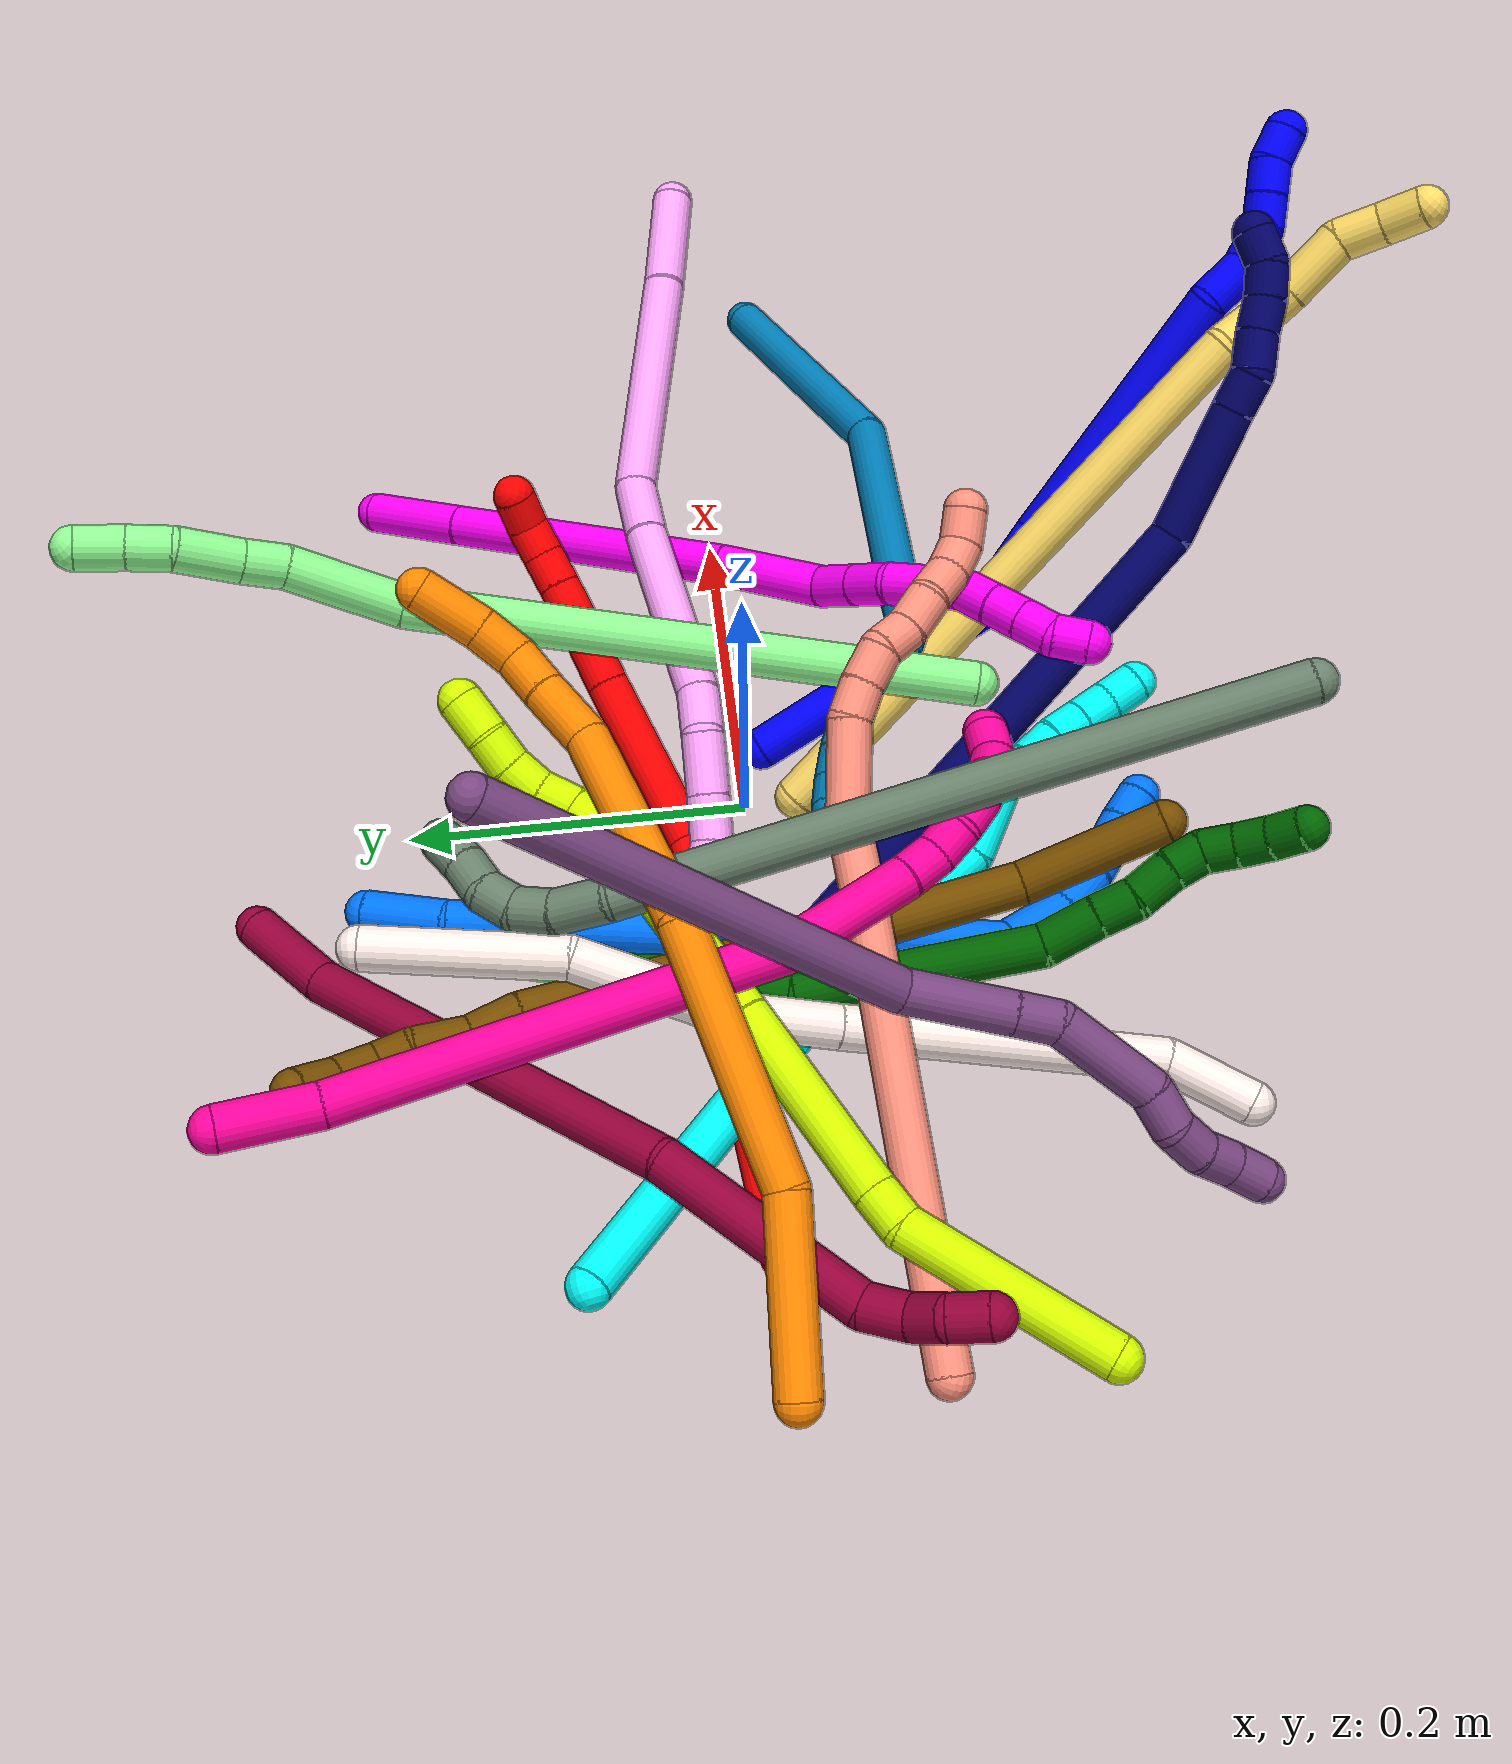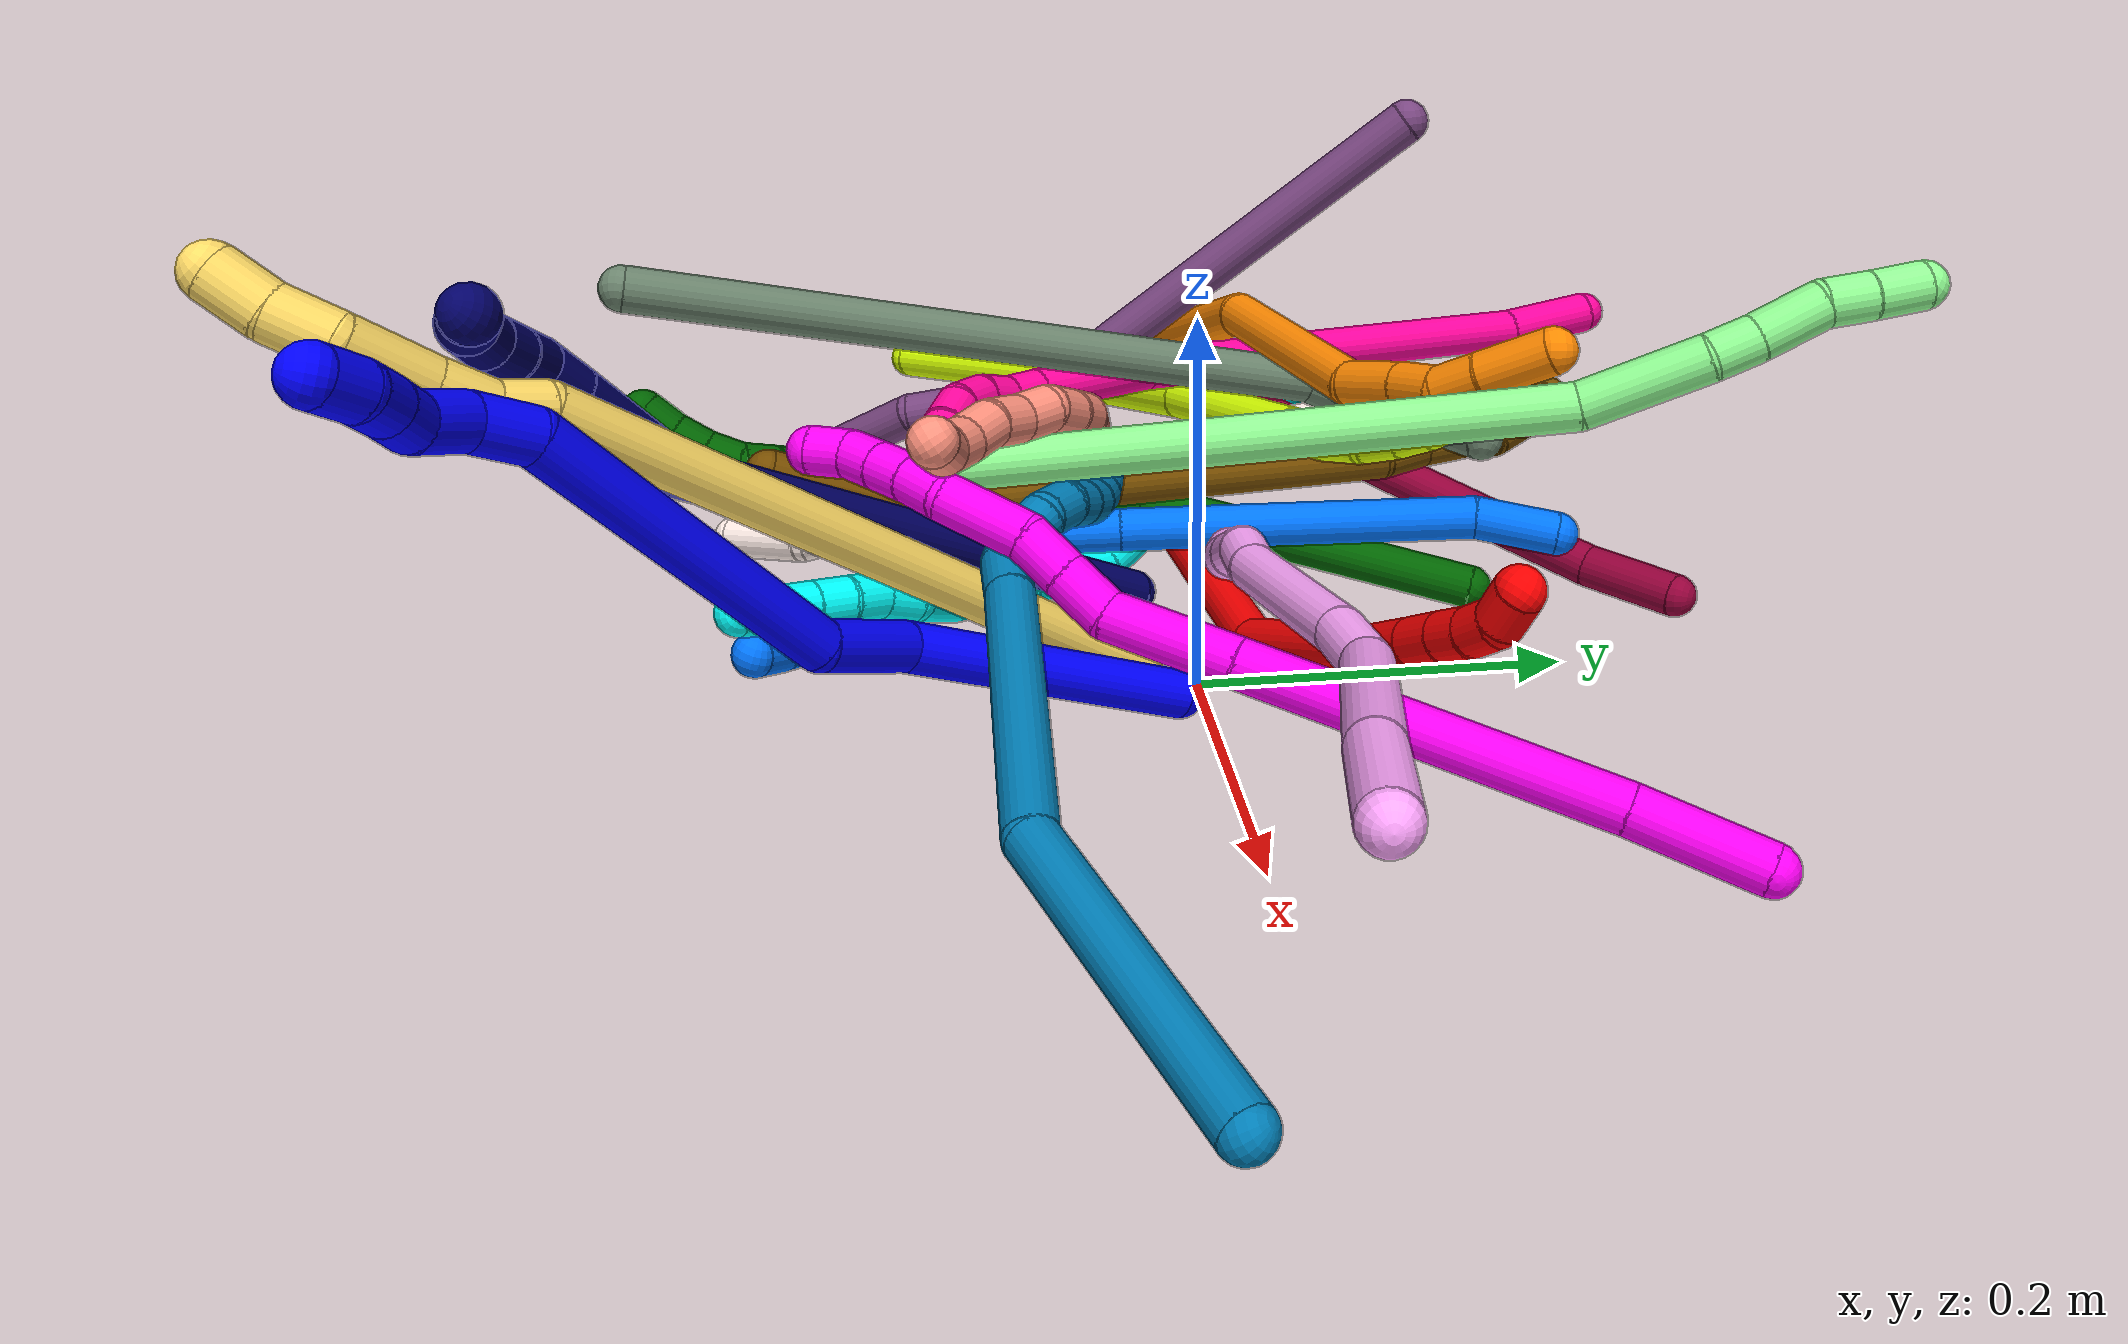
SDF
<sdf version="1.7">
 <world name="default">
  <plugin name="TubeGeneratorPlugin" filename="libtube_generator_plugin.so"/>
  <model name="photoneo_s_sensor">
   <static>1</static>
   <pose>0 0 2 1.57079 1.57079 3.14159</pose>
   <link name="link">
    <inertial><mass>0.1</mass></inertial>
    <sensor name="sensor" type="depth">
     <update_rate>30</update_rate>
     <camera>
      <horizontal_fov>1.22</horizontal_fov>
      <image><width>1920</width><height>1200</height><format>B8G8R8</format></image>
      <clip><near>0.1</near><far>4</far></clip>
      <depth_camera><output>points</output></depth_camera>
     </camera>
     <plugin name="camera_plugin" filename="libgazebo_ros_depth_camera.so">
      <baseline>0.2</baseline>
      <alwaysOn>1</alwaysOn>
      <updateRate>0.0</updateRate>
      <cameraName>camera_ir</cameraName>
      <imageTopicName>/camera/color/image_raw</imageTopicName>
      <cameraInfoTopicName>/camera/color/camera_info</cameraInfoTopicName>
      <depthImageTopicName>/camera/depth/image_raw</depthImageTopicName>
      <depthImageCameraInfoTopicName>/camera/depth/camera_info</depthImageCameraInfoTopicName>
      <pointCloudTopicName>/camera/depth/points</pointCloudTopicName>
      <frameName>fr_optical</frameName>
      <pointCloudCutoff>0.1</pointCloudCutoff>
      <pointCloudCutoffMax>2.0</pointCloudCutoffMax>
      <distortionK1>0</distortionK1>
      <distortionK2>0</distortionK2>
      <distortionK3>0</distortionK3>
      <distortionT1>0</distortionT1>
      <distortionT2>0</distortionT2>
      <CxPrime>0</CxPrime>
      <Cx>0</Cx>
      <Cy>0</Cy>
      <focalLength>0</focalLength>
      <hackBaseline>0</hackBaseline>
     </plugin>
    </sensor>
   </link>
  </model>
  <gravity>0 0 -9.8</gravity>
  <magnetic_field>6e-06 2.3e-05 -4.2e-05</magnetic_field>
  <atmosphere type="adiabatic"/>
  <physics name="default_physics" default="0" type="ode">
   <max_step_size>0.003</max_step_size>
   <real_time_factor>1</real_time_factor>
   <real_time_update_rate>1000</real_time_update_rate>
   <max_contacts>10000</max_contacts>
   <ode>
    <solver>
     <type>quick</type>
     <iters>100</iters>
     <sor>1.3</sor>
     <use_dynamic_moi_rescaling>0</use_dynamic_moi_rescaling>
    </solver>
    <constraints>
     <contact_max_correcting_vel>0</contact_max_correcting_vel>
     <contact_surface_layer>0.001</contact_surface_layer>
     <cfm>0</cfm>
     <erp>0.2</erp>
    </constraints>
   </ode>
  </physics>
  <scene><ambient>0.4 0.4 0.4 1</ambient><background>0.7 0.7 0.7 1</background><shadows>0</shadows></scene>
  <audio><device>default</device></audio>
  <spherical_coordinates>
   <surface_model>EARTH_WGS84</surface_model>
   <latitude_deg>0</latitude_deg>
   <longitude_deg>0</longitude_deg>
   <elevation>0</elevation>
   <heading_deg>0</heading_deg>
  </spherical_coordinates>
  <model name="bin">
   <static>1</static>
   <link name="bottom">
    <collision name="collision-bottom">
     <pose>0 0 -0.01 0 -0 0</pose>
     <geometry><box><size>0.8 0.6 0.02</size></box></geometry>
     <surface>
      <friction><ode><mu>100</mu><mu2>100</mu2></ode></friction>
      <contact><collide_bitmask>65535</collide_bitmask></contact>
     </surface>
    </collision>
   </link>
   <link name="west_wall">
    <collision name="collision-west_wall">
     <pose>-0.41 0 0.1 0 -0 0</pose>
     <geometry><box><size>0.02 0.6 0.2</size></box></geometry>
     <surface>
      <friction><ode><mu>100</mu><mu2>100</mu2></ode></friction>
      <contact><collide_bitmask>65535</collide_bitmask></contact>
     </surface>
    </collision>
   </link>
   <link name="east_wall">
    <collision name="collision-east_wall">
     <pose>0.41 0 0.1 0 -0 0</pose>
     <geometry><box><size>0.02 0.6 0.2</size></box></geometry>
     <surface>
      <friction><ode><mu>100</mu><mu2>100</mu2></ode></friction>
      <contact><collide_bitmask>65535</collide_bitmask></contact>
     </surface>
    </collision>
   </link>
   <link name="south_wall">
    <collision name="collision-south_wall">
     <pose>0 -0.31 0.1 0 -0 0</pose>
     <geometry><box><size>0.8 0.02 0.2</size></box></geometry>
     <surface>
      <friction><ode><mu>100</mu><mu2>100</mu2></ode></friction>
      <contact><collide_bitmask>65535</collide_bitmask></contact>
     </surface>
    </collision>
   </link>
   <link name="north_wall">
    <collision name="collision-north_wall">
     <pose>0 0.31 0.1 0 -0 0</pose>
     <geometry><box><size>0.8 0.02 0.2</size></box></geometry>
     <surface>
      <friction><ode><mu>100</mu><mu2>100</mu2></ode></friction>
      <contact><collide_bitmask>65535</collide_bitmask></contact>
     </surface>
    </collision>
   </link>
  </model>
  <model name="1">
   <static>0</static>
   <link name="1">
    <collision name="collision-cylinder-e_1_1_4">
     <pose>0.001977 0.000999 0.077982 -0.012808 0.025342 -0.000162</pose>
     <geometry><cylinder><radius>0.0125</radius><length>0.156026</length></cylinder></geometry>
     <surface>
      <friction><ode><mu>1.16</mu><mu2>1.16</mu2><slip1>0</slip1><slip2>0</slip2></ode></friction>
      <contact><ode><kp>1e+06</kp><kd>1</kd><max_vel>0</max_vel><min_depth>0.001</min_depth></ode></contact>
     </surface>
    </collision>
    <visual name="visual-cylinder-e_1_1_4">
     <pose>0.001977 0.000999 0.077982 -0.012808 0.025342 -0.000162</pose>
     <geometry><cylinder><radius>0.0125</radius><length>0.156026</length></cylinder></geometry>
     <material><ambient>0 0 1 1</ambient></material>
    </visual>
    <collision name="collision-cylinder-e_2_4_5">
     <pose>-0.001584 -0.008308 0.182139 0.375085 -0.194358 -0.036996</pose>
     <geometry><cylinder><radius>0.0125</radius><length>0.057343</length></cylinder></geometry>
     <surface>
      <friction><ode><mu>1.16</mu><mu2>1.16</mu2><slip1>0</slip1><slip2>0</slip2></ode></friction>
      <contact><ode><kp>1e+06</kp><kd>1</kd><max_vel>0</max_vel><min_depth>0.001</min_depth></ode></contact>
     </surface>
    </collision>
    <visual name="visual-cylinder-e_2_4_5">
     <pose>-0.001584 -0.008308 0.182139 0.375085 -0.194358 -0.036996</pose>
     <geometry><cylinder><radius>0.0125</radius><length>0.057343</length></cylinder></geometry>
     <material><ambient>0 0 1 1</ambient></material>
    </visual>
    <collision name="collision-cylinder-e_3_5_6">
     <pose>0.018657 -0.047827 0.284251 0.367251 0.306836 0.05742</pose>
     <geometry><cylinder><radius>0.0125</radius><length>0.170694</length></cylinder></geometry>
     <surface>
      <friction><ode><mu>1.16</mu><mu2>1.16</mu2><slip1>0</slip1><slip2>0</slip2></ode></friction>
      <contact><ode><kp>1e+06</kp><kd>1</kd><max_vel>0</max_vel><min_depth>0.001</min_depth></ode></contact>
     </surface>
    </collision>
    <visual name="visual-cylinder-e_3_5_6">
     <pose>0.018657 -0.047827 0.284251 0.367251 0.306836 0.05742</pose>
     <geometry><cylinder><radius>0.0125</radius><length>0.170694</length></cylinder></geometry>
     <material><ambient>0 0 1 1</ambient></material>
    </visual>
    <collision name="collision-cylinder-e_4_6_7">
     <pose>0.043907 -0.079773 0.374139 0.193397 -0.037184 -0.003607</pose>
     <geometry><cylinder><radius>0.0125</radius><length>0.028456</length></cylinder></geometry>
     <surface>
      <friction><ode><mu>1.16</mu><mu2>1.16</mu2><slip1>0</slip1><slip2>0</slip2></ode></friction>
      <contact><ode><kp>1e+06</kp><kd>1</kd><max_vel>0</max_vel><min_depth>0.001</min_depth></ode></contact>
     </surface>
    </collision>
    <visual name="visual-cylinder-e_4_6_7">
     <pose>0.043907 -0.079773 0.374139 0.193397 -0.037184 -0.003607</pose>
     <geometry><cylinder><radius>0.0125</radius><length>0.028456</length></cylinder></geometry>
     <material><ambient>0 0 1 1</ambient></material>
    </visual>
    <collision name="collision-cylinder-e_5_7_8">
     <pose>0.038922 -0.088645 0.399502 0.493689 -0.331211 -0.084181</pose>
     <geometry><cylinder><radius>0.0125</radius><length>0.027402</length></cylinder></geometry>
     <surface>
      <friction><ode><mu>1.16</mu><mu2>1.16</mu2><slip1>0</slip1><slip2>0</slip2></ode></friction>
      <contact><ode><kp>1e+06</kp><kd>1</kd><max_vel>0</max_vel><min_depth>0.001</min_depth></ode></contact>
     </surface>
    </collision>
    <visual name="visual-cylinder-e_5_7_8">
     <pose>0.038922 -0.088645 0.399502 0.493689 -0.331211 -0.084181</pose>
     <geometry><cylinder><radius>0.0125</radius><length>0.027402</length></cylinder></geometry>
     <material><ambient>0 0 1 1</ambient></material>
    </visual>
    <collision name="collision-cylinder-e_6_8_9">
     <pose>0.034113 -0.102468 0.417305 0.876726 -0.03538 -0.016587</pose>
     <geometry><cylinder><radius>0.0125</radius><length>0.020004</length></cylinder></geometry>
     <surface>
      <friction><ode><mu>1.16</mu><mu2>1.16</mu2><slip1>0</slip1><slip2>0</slip2></ode></friction>
      <contact><ode><kp>1e+06</kp><kd>1</kd><max_vel>0</max_vel><min_depth>0.001</min_depth></ode></contact>
     </surface>
    </collision>
    <visual name="visual-cylinder-e_6_8_9">
     <pose>0.034113 -0.102468 0.417305 0.876726 -0.03538 -0.016587</pose>
     <geometry><cylinder><radius>0.0125</radius><length>0.020004</length></cylinder></geometry>
     <material><ambient>0 0 1 1</ambient></material>
    </visual>
    <collision name="collision-cylinder-e_7_9_10">
     <pose>0.032837 -0.117777 0.430141 0.869326 -0.092154 -0.042809</pose>
     <geometry><cylinder><radius>0.0125</radius><length>0.02005</length></cylinder></geometry>
     <surface>
      <friction><ode><mu>1.16</mu><mu2>1.16</mu2><slip1>0</slip1><slip2>0</slip2></ode></friction>
      <contact><ode><kp>1e+06</kp><kd>1</kd><max_vel>0</max_vel><min_depth>0.001</min_depth></ode></contact>
     </surface>
    </collision>
    <visual name="visual-cylinder-e_7_9_10">
     <pose>0.032837 -0.117777 0.430141 0.869326 -0.092154 -0.042809</pose>
     <geometry><cylinder><radius>0.0125</radius><length>0.02005</length></cylinder></geometry>
     <material><ambient>0 0 1 1</ambient></material>
    </visual>
    <collision name="collision-cylinder-e_8_10_2">
     <pose>0.031144 -0.130547 0.445138 0.541412 -0.076978 -0.021373</pose>
     <geometry><cylinder><radius>0.0125</radius><length>0.020024</length></cylinder></geometry>
     <surface>
      <friction><ode><mu>1.16</mu><mu2>1.16</mu2><slip1>0</slip1><slip2>0</slip2></ode></friction>
      <contact><ode><kp>1e+06</kp><kd>1</kd><max_vel>0</max_vel><min_depth>0.001</min_depth></ode></contact>
     </surface>
    </collision>
    <visual name="visual-cylinder-e_8_10_2">
     <pose>0.031144 -0.130547 0.445138 0.541412 -0.076978 -0.021373</pose>
     <geometry><cylinder><radius>0.0125</radius><length>0.020024</length></cylinder></geometry>
     <material><ambient>0 0 1 1</ambient></material>
    </visual>
    <collision name="collision-sphere-2">
     <pose>0.030374 -0.135691 0.453693 0 -0 0</pose>
     <geometry><sphere><radius>0.0125</radius></sphere></geometry>
     <surface>
      <friction><ode><mu>1.16</mu><mu2>1.16</mu2><slip1>0</slip1><slip2>0</slip2></ode></friction>
      <contact><ode><kp>1e+06</kp><kd>1</kd><max_vel>0</max_vel><min_depth>0.001</min_depth></ode></contact>
     </surface>
    </collision>
    <visual name="visual-sphere-2">
     <pose>0.030374 -0.135691 0.453693 0 -0 0</pose>
     <geometry><sphere><radius>0.0125</radius></sphere></geometry>
     <material><ambient>0 0 1 1</ambient></material>
    </visual>
    <collision name="collision-sphere-10">
     <pose>0.031914 -0.125402 0.436583 0 -0 0</pose>
     <geometry><sphere><radius>0.0125</radius></sphere></geometry>
     <surface>
      <friction><ode><mu>1.16</mu><mu2>1.16</mu2><slip1>0</slip1><slip2>0</slip2></ode></friction>
      <contact><ode><kp>1e+06</kp><kd>1</kd><max_vel>0</max_vel><min_depth>0.001</min_depth></ode></contact>
     </surface>
    </collision>
    <visual name="visual-sphere-10">
     <pose>0.031914 -0.125402 0.436583 0 -0 0</pose>
     <geometry><sphere><radius>0.0125</radius></sphere></geometry>
     <material><ambient>0 0 1 1</ambient></material>
    </visual>
    <collision name="collision-sphere-9">
     <pose>0.033759 -0.110151 0.423699 0 -0 0</pose>
     <geometry><sphere><radius>0.0125</radius></sphere></geometry>
     <surface>
      <friction><ode><mu>1.16</mu><mu2>1.16</mu2><slip1>0</slip1><slip2>0</slip2></ode></friction>
      <contact><ode><kp>1e+06</kp><kd>1</kd><max_vel>0</max_vel><min_depth>0.001</min_depth></ode></contact>
     </surface>
    </collision>
    <visual name="visual-sphere-9">
     <pose>0.033759 -0.110151 0.423699 0 -0 0</pose>
     <geometry><sphere><radius>0.0125</radius></sphere></geometry>
     <material><ambient>0 0 1 1</ambient></material>
    </visual>
    <collision name="collision-sphere-4">
     <pose>0.003954 0.001998 0.155963 0 -0 0</pose>
     <geometry><sphere><radius>0.0125</radius></sphere></geometry>
     <surface>
      <friction><ode><mu>1.16</mu><mu2>1.16</mu2><slip1>0</slip1><slip2>0</slip2></ode></friction>
      <contact><ode><kp>1e+06</kp><kd>1</kd><max_vel>0</max_vel><min_depth>0.001</min_depth></ode></contact>
     </surface>
    </collision>
    <visual name="visual-sphere-4">
     <pose>0.003954 0.001998 0.155963 0 -0 0</pose>
     <geometry><sphere><radius>0.0125</radius></sphere></geometry>
     <material><ambient>0 0 1 1</ambient></material>
    </visual>
    <collision name="collision-sphere-1">
     <geometry><sphere><radius>0.0125</radius></sphere></geometry>
     <surface>
      <friction><ode><mu>1.16</mu><mu2>1.16</mu2><slip1>0</slip1><slip2>0</slip2></ode></friction>
      <contact><ode><kp>1e+06</kp><kd>1</kd><max_vel>0</max_vel><min_depth>0.001</min_depth></ode></contact>
     </surface>
    </collision>
    <visual name="visual-sphere-1">
     <geometry><sphere><radius>0.0125</radius></sphere></geometry>
     <material><ambient>0 0 1 1</ambient></material>
    </visual>
    <collision name="collision-sphere-8">
     <pose>0.034467 -0.094785 0.410911 0 -0 0</pose>
     <geometry><sphere><radius>0.0125</radius></sphere></geometry>
     <surface>
      <friction><ode><mu>1.16</mu><mu2>1.16</mu2><slip1>0</slip1><slip2>0</slip2></ode></friction>
      <contact><ode><kp>1e+06</kp><kd>1</kd><max_vel>0</max_vel><min_depth>0.001</min_depth></ode></contact>
     </surface>
    </collision>
    <visual name="visual-sphere-8">
     <pose>0.034467 -0.094785 0.410911 0 -0 0</pose>
     <geometry><sphere><radius>0.0125</radius></sphere></geometry>
     <material><ambient>0 0 1 1</ambient></material>
    </visual>
    <collision name="collision-sphere-5">
     <pose>-0.007122 -0.018615 0.208315 0 -0 0</pose>
     <geometry><sphere><radius>0.0125</radius></sphere></geometry>
     <surface>
      <friction><ode><mu>1.16</mu><mu2>1.16</mu2><slip1>0</slip1><slip2>0</slip2></ode></friction>
      <contact><ode><kp>1e+06</kp><kd>1</kd><max_vel>0</max_vel><min_depth>0.001</min_depth></ode></contact>
     </surface>
    </collision>
    <visual name="visual-sphere-5">
     <pose>-0.007122 -0.018615 0.208315 0 -0 0</pose>
     <geometry><sphere><radius>0.0125</radius></sphere></geometry>
     <material><ambient>0 0 1 1</ambient></material>
    </visual>
    <collision name="collision-sphere-6">
     <pose>0.044436 -0.07704 0.360186 0 -0 0</pose>
     <geometry><sphere><radius>0.0125</radius></sphere></geometry>
     <surface>
      <friction><ode><mu>1.16</mu><mu2>1.16</mu2><slip1>0</slip1><slip2>0</slip2></ode></friction>
      <contact><ode><kp>1e+06</kp><kd>1</kd><max_vel>0</max_vel><min_depth>0.001</min_depth></ode></contact>
     </surface>
    </collision>
    <visual name="visual-sphere-6">
     <pose>0.044436 -0.07704 0.360186 0 -0 0</pose>
     <geometry><sphere><radius>0.0125</radius></sphere></geometry>
     <material><ambient>0 0 1 1</ambient></material>
    </visual>
    <collision name="collision-sphere-7">
     <pose>0.043378 -0.082505 0.388092 0 -0 0</pose>
     <geometry><sphere><radius>0.0125</radius></sphere></geometry>
     <surface>
      <friction><ode><mu>1.16</mu><mu2>1.16</mu2><slip1>0</slip1><slip2>0</slip2></ode></friction>
      <contact><ode><kp>1e+06</kp><kd>1</kd><max_vel>0</max_vel><min_depth>0.001</min_depth></ode></contact>
     </surface>
    </collision>
    <visual name="visual-sphere-7">
     <pose>0.043378 -0.082505 0.388092 0 -0 0</pose>
     <geometry><sphere><radius>0.0125</radius></sphere></geometry>
     <material><ambient>0 0 1 1</ambient></material>
    </visual>
    <inertial>
     <pose>0.015365 -0.040418 0.237222 0 -0 0</pose>
     <mass>0.5</mass>
     <inertia>
      <ixx>0.000775</ixx>
      <ixy>0</ixy>
      <ixz>0</ixz>
      <iyy>0.000754</iyy>
      <iyz>0</iyz>
      <izz>5.6e-05</izz>
     </inertia>
    </inertial>
   </link>
   <pose>0.033823 -0.014105 0.011498 -0.965168 -0.919573 2.98989</pose>
  </model>
  <model name="2">
   <static>0</static>
   <link name="2">
    <collision name="collision-cylinder-e_1_1_4">
     <pose>0.127976 -0.021684 -0.02227 2.36952 1.33253 2.18735</pose>
     <geometry><cylinder><radius>0.0125</radius><length>0.263393</length></cylinder></geometry>
     <surface>
      <friction><ode><mu>1.16</mu><mu2>1.16</mu2><slip1>0</slip1><slip2>0</slip2></ode></friction>
      <contact><ode><kp>1e+06</kp><kd>1</kd><max_vel>0</max_vel><min_depth>0.001</min_depth></ode></contact>
     </surface>
    </collision>
    <visual name="visual-cylinder-e_1_1_4">
     <pose>0.127976 -0.021684 -0.02227 2.36952 1.33253 2.18735</pose>
     <geometry><cylinder><radius>0.0125</radius><length>0.263393</length></cylinder></geometry>
     <material><ambient>1 0 0 1</ambient></material>
    </visual>
    <collision name="collision-cylinder-e_2_4_5">
     <pose>0.307857 -0.050907 -0.030588 0.495421 1.27427 0.370068</pose>
     <geometry><cylinder><radius>0.0125</radius><length>0.108548</length></cylinder></geometry>
     <surface>
      <friction><ode><mu>1.16</mu><mu2>1.16</mu2><slip1>0</slip1><slip2>0</slip2></ode></friction>
      <contact><ode><kp>1e+06</kp><kd>1</kd><max_vel>0</max_vel><min_depth>0.001</min_depth></ode></contact>
     </surface>
    </collision>
    <visual name="visual-cylinder-e_2_4_5">
     <pose>0.307857 -0.050907 -0.030588 0.495421 1.27427 0.370068</pose>
     <geometry><cylinder><radius>0.0125</radius><length>0.108548</length></cylinder></geometry>
     <material><ambient>1 0 0 1</ambient></material>
    </visual>
    <collision name="collision-cylinder-e_3_5_6">
     <pose>0.378409 -0.063098 -0.009385 0.570414 1.138 0.370731</pose>
     <geometry><cylinder><radius>0.0125</radius><length>0.04108</length></cylinder></geometry>
     <surface>
      <friction><ode><mu>1.16</mu><mu2>1.16</mu2><slip1>0</slip1><slip2>0</slip2></ode></friction>
      <contact><ode><kp>1e+06</kp><kd>1</kd><max_vel>0</max_vel><min_depth>0.001</min_depth></ode></contact>
     </surface>
    </collision>
    <visual name="visual-cylinder-e_3_5_6">
     <pose>0.378409 -0.063098 -0.009385 0.570414 1.138 0.370731</pose>
     <geometry><cylinder><radius>0.0125</radius><length>0.04108</length></cylinder></geometry>
     <material><ambient>1 0 0 1</ambient></material>
    </visual>
    <collision name="collision-cylinder-e_4_6_7">
     <pose>0.408324 -0.070322 0.002616 0.496241 1.12382 0.316349</pose>
     <geometry><cylinder><radius>0.0125</radius><length>0.024994</length></cylinder></geometry>
     <surface>
      <friction><ode><mu>1.16</mu><mu2>1.16</mu2><slip1>0</slip1><slip2>0</slip2></ode></friction>
      <contact><ode><kp>1e+06</kp><kd>1</kd><max_vel>0</max_vel><min_depth>0.001</min_depth></ode></contact>
     </surface>
    </collision>
    <visual name="visual-cylinder-e_4_6_7">
     <pose>0.408324 -0.070322 0.002616 0.496241 1.12382 0.316349</pose>
     <geometry><cylinder><radius>0.0125</radius><length>0.024994</length></cylinder></geometry>
     <material><ambient>1 0 0 1</ambient></material>
    </visual>
    <collision name="collision-cylinder-e_5_7_8">
     <pose>0.429037 -0.074849 0.011302 0.461054 1.13528 0.297105</pose>
     <geometry><cylinder><radius>0.0125</radius><length>0.020834</length></cylinder></geometry>
     <surface>
      <friction><ode><mu>1.16</mu><mu2>1.16</mu2><slip1>0</slip1><slip2>0</slip2></ode></friction>
      <contact><ode><kp>1e+06</kp><kd>1</kd><max_vel>0</max_vel><min_depth>0.001</min_depth></ode></contact>
     </surface>
    </collision>
    <visual name="visual-cylinder-e_5_7_8">
     <pose>0.429037 -0.074849 0.011302 0.461054 1.13528 0.297105</pose>
     <geometry><cylinder><radius>0.0125</radius><length>0.020834</length></cylinder></geometry>
     <material><ambient>1 0 0 1</ambient></material>
    </visual>
    <collision name="collision-cylinder-e_6_8_9">
     <pose>0.447057 -0.079169 0.020045 0.457182 1.01239 0.256544</pose>
     <geometry><cylinder><radius>0.0125</radius><length>0.020223</length></cylinder></geometry>
     <surface>
      <friction><ode><mu>1.16</mu><mu2>1.16</mu2><slip1>0</slip1><slip2>0</slip2></ode></friction>
      <contact><ode><kp>1e+06</kp><kd>1</kd><max_vel>0</max_vel><min_depth>0.001</min_depth></ode></contact>
     </surface>
    </collision>
    <visual name="visual-cylinder-e_6_8_9">
     <pose>0.447057 -0.079169 0.020045 0.457182 1.01239 0.256544</pose>
     <geometry><cylinder><radius>0.0125</radius><length>0.020223</length></cylinder></geometry>
     <material><ambient>1 0 0 1</ambient></material>
    </visual>
    <collision name="collision-cylinder-e_7_9_2">
     <pose>0.460953 -0.086164 0.032582 0.539676 0.533325 0.150821</pose>
     <geometry><cylinder><radius>0.0125</radius><length>0.020929</length></cylinder></geometry>
     <surface>
      <friction><ode><mu>1.16</mu><mu2>1.16</mu2><slip1>0</slip1><slip2>0</slip2></ode></friction>
      <contact><ode><kp>1e+06</kp><kd>1</kd><max_vel>0</max_vel><min_depth>0.001</min_depth></ode></contact>
     </surface>
    </collision>
    <visual name="visual-cylinder-e_7_9_2">
     <pose>0.460953 -0.086164 0.032582 0.539676 0.533325 0.150821</pose>
     <geometry><cylinder><radius>0.0125</radius><length>0.020929</length></cylinder></geometry>
     <material><ambient>1 0 0 1</ambient></material>
    </visual>
    <collision name="collision-sphere-2">
     <pose>0.466273 -0.090795 0.040313 0 -0 0</pose>
     <geometry><sphere><radius>0.0125</radius></sphere></geometry>
     <surface>
      <friction><ode><mu>1.16</mu><mu2>1.16</mu2><slip1>0</slip1><slip2>0</slip2></ode></friction>
      <contact><ode><kp>1e+06</kp><kd>1</kd><max_vel>0</max_vel><min_depth>0.001</min_depth></ode></contact>
     </surface>
    </collision>
    <visual name="visual-sphere-2">
     <pose>0.466273 -0.090795 0.040313 0 -0 0</pose>
     <geometry><sphere><radius>0.0125</radius></sphere></geometry>
     <material><ambient>1 0 0 1</ambient></material>
    </visual>
    <collision name="collision-sphere-9">
     <pose>0.455633 -0.081534 0.024852 0 -0 0</pose>
     <geometry><sphere><radius>0.0125</radius></sphere></geometry>
     <surface>
      <friction><ode><mu>1.16</mu><mu2>1.16</mu2><slip1>0</slip1><slip2>0</slip2></ode></friction>
      <contact><ode><kp>1e+06</kp><kd>1</kd><max_vel>0</max_vel><min_depth>0.001</min_depth></ode></contact>
     </surface>
    </collision>
    <visual name="visual-sphere-9">
     <pose>0.455633 -0.081534 0.024852 0 -0 0</pose>
     <geometry><sphere><radius>0.0125</radius></sphere></geometry>
     <material><ambient>1 0 0 1</ambient></material>
    </visual>
    <collision name="collision-sphere-4">
     <pose>0.255952 -0.043368 -0.04454 0 -0 0</pose>
     <geometry><sphere><radius>0.0125</radius></sphere></geometry>
     <surface>
      <friction><ode><mu>1.16</mu><mu2>1.16</mu2><slip1>0</slip1><slip2>0</slip2></ode></friction>
      <contact><ode><kp>1e+06</kp><kd>1</kd><max_vel>0</max_vel><min_depth>0.001</min_depth></ode></contact>
     </surface>
    </collision>
    <visual name="visual-sphere-4">
     <pose>0.255952 -0.043368 -0.04454 0 -0 0</pose>
     <geometry><sphere><radius>0.0125</radius></sphere></geometry>
     <material><ambient>1 0 0 1</ambient></material>
    </visual>
    <collision name="collision-sphere-1">
     <geometry><sphere><radius>0.0125</radius></sphere></geometry>
     <surface>
      <friction><ode><mu>1.16</mu><mu2>1.16</mu2><slip1>0</slip1><slip2>0</slip2></ode></friction>
      <contact><ode><kp>1e+06</kp><kd>1</kd><max_vel>0</max_vel><min_depth>0.001</min_depth></ode></contact>
     </surface>
    </collision>
    <visual name="visual-sphere-1">
     <geometry><sphere><radius>0.0125</radius></sphere></geometry>
     <material><ambient>1 0 0 1</ambient></material>
    </visual>
    <collision name="collision-sphere-8">
     <pose>0.438482 -0.076804 0.015238 0 -0 0</pose>
     <geometry><sphere><radius>0.0125</radius></sphere></geometry>
     <surface>
      <friction><ode><mu>1.16</mu><mu2>1.16</mu2><slip1>0</slip1><slip2>0</slip2></ode></friction>
      <contact><ode><kp>1e+06</kp><kd>1</kd><max_vel>0</max_vel><min_depth>0.001</min_depth></ode></contact>
     </surface>
    </collision>
    <visual name="visual-sphere-8">
     <pose>0.438482 -0.076804 0.015238 0 -0 0</pose>
     <geometry><sphere><radius>0.0125</radius></sphere></geometry>
     <material><ambient>1 0 0 1</ambient></material>
    </visual>
    <collision name="collision-sphere-5">
     <pose>0.359763 -0.058447 -0.016636 0 -0 0</pose>
     <geometry><sphere><radius>0.0125</radius></sphere></geometry>
     <surface>
      <friction><ode><mu>1.16</mu><mu2>1.16</mu2><slip1>0</slip1><slip2>0</slip2></ode></friction>
      <contact><ode><kp>1e+06</kp><kd>1</kd><max_vel>0</max_vel><min_depth>0.001</min_depth></ode></contact>
     </surface>
    </collision>
    <visual name="visual-sphere-5">
     <pose>0.359763 -0.058447 -0.016636 0 -0 0</pose>
     <geometry><sphere><radius>0.0125</radius></sphere></geometry>
     <material><ambient>1 0 0 1</ambient></material>
    </visual>
    <collision name="collision-sphere-6">
     <pose>0.397055 -0.06775 -0.002134 0 -0 0</pose>
     <geometry><sphere><radius>0.0125</radius></sphere></geometry>
     <surface>
      <friction><ode><mu>1.16</mu><mu2>1.16</mu2><slip1>0</slip1><slip2>0</slip2></ode></friction>
      <contact><ode><kp>1e+06</kp><kd>1</kd><max_vel>0</max_vel><min_depth>0.001</min_depth></ode></contact>
     </surface>
    </collision>
    <visual name="visual-sphere-6">
     <pose>0.397055 -0.06775 -0.002134 0 -0 0</pose>
     <geometry><sphere><radius>0.0125</radius></sphere></geometry>
     <material><ambient>1 0 0 1</ambient></material>
    </visual>
    <collision name="collision-sphere-7">
     <pose>0.419593 -0.072894 0.007366 0 -0 0</pose>
     <geometry><sphere><radius>0.0125</radius></sphere></geometry>
     <surface>
      <friction><ode><mu>1.16</mu><mu2>1.16</mu2><slip1>0</slip1><slip2>0</slip2></ode></friction>
      <contact><ode><kp>1e+06</kp><kd>1</kd><max_vel>0</max_vel><min_depth>0.001</min_depth></ode></contact>
     </surface>
    </collision>
    <visual name="visual-sphere-7">
     <pose>0.419593 -0.072894 0.007366 0 -0 0</pose>
     <geometry><sphere><radius>0.0125</radius></sphere></geometry>
     <material><ambient>1 0 0 1</ambient></material>
    </visual>
    <inertial>
     <pose>0.241004 -0.041101 -0.016367 0 -0 0</pose>
     <mass>0.5</mass>
     <inertia>
      <ixx>0.000173</ixx>
      <ixy>0</ixy>
      <ixz>0</ixz>
      <iyy>0.001908</iyy>
      <iyz>0</iyz>
      <izz>-0.001334</izz>
     </inertia>
    </inertial>
   </link>
   <pose>-0.290127 0.011928 0.011476 -0.692941 -0.025661 0.326836</pose>
  </model>
  <model name="3">
   <static>0</static>
   <link name="3">
    <collision name="collision-cylinder-e_1_1_4">
     <pose>0.080593 -0.060833 -0.06502 2.38946 0.735635 1.54643</pose>
     <geometry><cylinder><radius>0.0125</radius><length>0.240195</length></cylinder></geometry>
     <surface>
      <friction><ode><mu>1.16</mu><mu2>1.16</mu2><slip1>0</slip1><slip2>0</slip2></ode></friction>
      <contact><ode><kp>1e+06</kp><kd>1</kd><max_vel>0</max_vel><min_depth>0.001</min_depth></ode></contact>
     </surface>
    </collision>
    <visual name="visual-cylinder-e_1_1_4">
     <pose>0.080593 -0.060833 -0.06502 2.38946 0.735635 1.54643</pose>
     <geometry><cylinder><radius>0.0125</radius><length>0.240195</length></cylinder></geometry>
     <material><ambient>0.003922 1 0.996078 1</ambient></material>
    </visual>
    <collision name="collision-cylinder-e_2_4_5">
     <pose>0.187488 -0.127334 -0.144633 2.77107 1.03395 2.50477</pose>
     <geometry><cylinder><radius>0.0125</radius><length>0.061216</length></cylinder></geometry>
     <surface>
      <friction><ode><mu>1.16</mu><mu2>1.16</mu2><slip1>0</slip1><slip2>0</slip2></ode></friction>
      <contact><ode><kp>1e+06</kp><kd>1</kd><max_vel>0</max_vel><min_depth>0.001</min_depth></ode></contact>
     </surface>
    </collision>
    <visual name="visual-cylinder-e_2_4_5">
     <pose>0.187488 -0.127334 -0.144633 2.77107 1.03395 2.50477</pose>
     <geometry><cylinder><radius>0.0125</radius><length>0.061216</length></cylinder></geometry>
     <material><ambient>0.003922 1 0.996078 1</ambient></material>
    </visual>
    <collision name="collision-cylinder-e_3_5_6">
     <pose>0.23682 -0.13837 -0.170053 2.68146 1.0875 2.40236</pose>
     <geometry><cylinder><radius>0.0125</radius><length>0.052018</length></cylinder></geometry>
     <surface>
      <friction><ode><mu>1.16</mu><mu2>1.16</mu2><slip1>0</slip1><slip2>0</slip2></ode></friction>
      <contact><ode><kp>1e+06</kp><kd>1</kd><max_vel>0</max_vel><min_depth>0.001</min_depth></ode></contact>
     </surface>
    </collision>
    <visual name="visual-cylinder-e_3_5_6">
     <pose>0.23682 -0.13837 -0.170053 2.68146 1.0875 2.40236</pose>
     <geometry><cylinder><radius>0.0125</radius><length>0.052018</length></cylinder></geometry>
     <material><ambient>0.003922 1 0.996078 1</ambient></material>
    </visual>
    <collision name="collision-cylinder-e_4_6_7">
     <pose>0.274012 -0.14285 -0.197522 -3.08834 0.704426 -2.99693</pose>
     <geometry><cylinder><radius>0.0125</radius><length>0.043736</length></cylinder></geometry>
     <surface>
      <friction><ode><mu>1.16</mu><mu2>1.16</mu2><slip1>0</slip1><slip2>0</slip2></ode></friction>
      <contact><ode><kp>1e+06</kp><kd>1</kd><max_vel>0</max_vel><min_depth>0.001</min_depth></ode></contact>
     </surface>
    </collision>
    <visual name="visual-cylinder-e_4_6_7">
     <pose>0.274012 -0.14285 -0.197522 -3.08834 0.704426 -2.99693</pose>
     <geometry><cylinder><radius>0.0125</radius><length>0.043736</length></cylinder></geometry>
     <material><ambient>0.003922 1 0.996078 1</ambient></material>
    </visual>
    <collision name="collision-cylinder-e_5_7_8">
     <pose>0.298291 -0.141198 -0.218164 -2.95271 1.18792 -2.86287</pose>
     <geometry><cylinder><radius>0.0125</radius><length>0.021816</length></cylinder></geometry>
     <surface>
      <friction><ode><mu>1.16</mu><mu2>1.16</mu2><slip1>0</slip1><slip2>0</slip2></ode></friction>
      <contact><ode><kp>1e+06</kp><kd>1</kd><max_vel>0</max_vel><min_depth>0.001</min_depth></ode></contact>
     </surface>
    </collision>
    <visual name="visual-cylinder-e_5_7_8">
     <pose>0.298291 -0.141198 -0.218164 -2.95271 1.18792 -2.86287</pose>
     <geometry><cylinder><radius>0.0125</radius><length>0.021816</length></cylinder></geometry>
     <material><ambient>0.003922 1 0.996078 1</ambient></material>
    </visual>
    <collision name="collision-cylinder-e_6_8_9">
     <pose>0.317507 -0.141784 -0.226795 2.85741 1.08349 2.67484</pose>
     <geometry><cylinder><radius>0.0125</radius><length>0.020593</length></cylinder></geometry>
     <surface>
      <friction><ode><mu>1.16</mu><mu2>1.16</mu2><slip1>0</slip1><slip2>0</slip2></ode></friction>
      <contact><ode><kp>1e+06</kp><kd>1</kd><max_vel>0</max_vel><min_depth>0.001</min_depth></ode></contact>
     </surface>
    </collision>
    <visual name="visual-cylinder-e_6_8_9">
     <pose>0.317507 -0.141784 -0.226795 2.85741 1.08349 2.67484</pose>
     <geometry><cylinder><radius>0.0125</radius><length>0.020593</length></cylinder></geometry>
     <material><ambient>0.003922 1 0.996078 1</ambient></material>
    </visual>
    <collision name="collision-cylinder-e_7_9_10">
     <pose>0.335987 -0.144768 -0.234488 2.6523 1.21628 2.45294</pose>
     <geometry><cylinder><radius>0.0125</radius><length>0.020007</length></cylinder></geometry>
     <surface>
      <friction><ode><mu>1.16</mu><mu2>1.16</mu2><slip1>0</slip1><slip2>0</slip2></ode></friction>
      <contact><ode><kp>1e+06</kp><kd>1</kd><max_vel>0</max_vel><min_depth>0.001</min_depth></ode></contact>
     </surface>
    </collision>
    <visual name="visual-cylinder-e_7_9_10">
     <pose>0.335987 -0.144768 -0.234488 2.6523 1.21628 2.45294</pose>
     <geometry><cylinder><radius>0.0125</radius><length>0.020007</length></cylinder></geometry>
     <material><ambient>0.003922 1 0.996078 1</ambient></material>
    </visual>
    <collision name="collision-cylinder-e_8_10_11">
     <pose>0.354781 -0.148074 -0.240721 2.6557 1.20708 2.45131</pose>
     <geometry><cylinder><radius>0.0125</radius><length>0.020144</length></cylinder></geometry>
     <surface>
      <friction><ode><mu>1.16</mu><mu2>1.16</mu2><slip1>0</slip1><slip2>0</slip2></ode></friction>
      <contact><ode><kp>1e+06</kp><kd>1</kd><max_vel>0</max_vel><min_depth>0.001</min_depth></ode></contact>
     </surface>
    </collision>
    <visual name="visual-cylinder-e_8_10_11">
     <pose>0.354781 -0.148074 -0.240721 2.6557 1.20708 2.45131</pose>
     <geometry><cylinder><radius>0.0125</radius><length>0.020144</length></cylinder></geometry>
     <material><ambient>0.003922 1 0.996078 1</ambient></material>
    </visual>
    <collision name="collision-cylinder-e_9_11_2">
     <pose>0.373804 -0.150683 -0.246978 2.84717 1.24684 2.73486</pose>
     <geometry><cylinder><radius>0.0125</radius><length>0.020275</length></cylinder></geometry>
     <surface>
      <friction><ode><mu>1.16</mu><mu2>1.16</mu2><slip1>0</slip1><slip2>0</slip2></ode></friction>
      <contact><ode><kp>1e+06</kp><kd>1</kd><max_vel>0</max_vel><min_depth>0.001</min_depth></ode></contact>
     </surface>
    </collision>
    <visual name="visual-cylinder-e_9_11_2">
     <pose>0.373804 -0.150683 -0.246978 2.84717 1.24684 2.73486</pose>
     <geometry><cylinder><radius>0.0125</radius><length>0.020275</length></cylinder></geometry>
     <material><ambient>0.003922 1 0.996078 1</ambient></material>
    </visual>
    <collision name="collision-sphere-2">
     <pose>0.383415 -0.15162 -0.250066 0 -0 0</pose>
     <geometry><sphere><radius>0.0125</radius></sphere></geometry>
     <surface>
      <friction><ode><mu>1.16</mu><mu2>1.16</mu2><slip1>0</slip1><slip2>0</slip2></ode></friction>
      <contact><ode><kp>1e+06</kp><kd>1</kd><max_vel>0</max_vel><min_depth>0.001</min_depth></ode></contact>
     </surface>
    </collision>
    <visual name="visual-sphere-2">
     <pose>0.383415 -0.15162 -0.250066 0 -0 0</pose>
     <geometry><sphere><radius>0.0125</radius></sphere></geometry>
     <material><ambient>0.003922 1 0.996078 1</ambient></material>
    </visual>
    <collision name="collision-sphere-11">
     <pose>0.364194 -0.149747 -0.24389 0 -0 0</pose>
     <geometry><sphere><radius>0.0125</radius></sphere></geometry>
     <surface>
      <friction><ode><mu>1.16</mu><mu2>1.16</mu2><slip1>0</slip1><slip2>0</slip2></ode></friction>
      <contact><ode><kp>1e+06</kp><kd>1</kd><max_vel>0</max_vel><min_depth>0.001</min_depth></ode></contact>
     </surface>
    </collision>
    <visual name="visual-sphere-11">
     <pose>0.364194 -0.149747 -0.24389 0 -0 0</pose>
     <geometry><sphere><radius>0.0125</radius></sphere></geometry>
     <material><ambient>0.003922 1 0.996078 1</ambient></material>
    </visual>
    <collision name="collision-sphere-10">
     <pose>0.345368 -0.1464 -0.237553 0 -0 0</pose>
     <geometry><sphere><radius>0.0125</radius></sphere></geometry>
     <surface>
      <friction><ode><mu>1.16</mu><mu2>1.16</mu2><slip1>0</slip1><slip2>0</slip2></ode></friction>
      <contact><ode><kp>1e+06</kp><kd>1</kd><max_vel>0</max_vel><min_depth>0.001</min_depth></ode></contact>
     </surface>
    </collision>
    <visual name="visual-sphere-10">
     <pose>0.345368 -0.1464 -0.237553 0 -0 0</pose>
     <geometry><sphere><radius>0.0125</radius></sphere></geometry>
     <material><ambient>0.003922 1 0.996078 1</ambient></material>
    </visual>
    <collision name="collision-sphere-9">
     <pose>0.326605 -0.143136 -0.231423 0 -0 0</pose>
     <geometry><sphere><radius>0.0125</radius></sphere></geometry>
     <surface>
      <friction><ode><mu>1.16</mu><mu2>1.16</mu2><slip1>0</slip1><slip2>0</slip2></ode></friction>
      <contact><ode><kp>1e+06</kp><kd>1</kd><max_vel>0</max_vel><min_depth>0.001</min_depth></ode></contact>
     </surface>
    </collision>
    <visual name="visual-sphere-9">
     <pose>0.326605 -0.143136 -0.231423 0 -0 0</pose>
     <geometry><sphere><radius>0.0125</radius></sphere></geometry>
     <material><ambient>0.003922 1 0.996078 1</ambient></material>
    </visual>
    <collision name="collision-sphere-4">
     <pose>0.161185 -0.121666 -0.130041 0 -0 0</pose>
     <geometry><sphere><radius>0.0125</radius></sphere></geometry>
     <surface>
      <friction><ode><mu>1.16</mu><mu2>1.16</mu2><slip1>0</slip1><slip2>0</slip2></ode></friction>
      <contact><ode><kp>1e+06</kp><kd>1</kd><max_vel>0</max_vel><min_depth>0.001</min_depth></ode></contact>
     </surface>
    </collision>
    <visual name="visual-sphere-4">
     <pose>0.161185 -0.121666 -0.130041 0 -0 0</pose>
     <geometry><sphere><radius>0.0125</radius></sphere></geometry>
     <material><ambient>0.003922 1 0.996078 1</ambient></material>
    </visual>
    <collision name="collision-sphere-1">
     <geometry><sphere><radius>0.0125</radius></sphere></geometry>
     <surface>
      <friction><ode><mu>1.16</mu><mu2>1.16</mu2><slip1>0</slip1><slip2>0</slip2></ode></friction>
      <contact><ode><kp>1e+06</kp><kd>1</kd><max_vel>0</max_vel><min_depth>0.001</min_depth></ode></contact>
     </surface>
    </collision>
    <visual name="visual-sphere-1">
     <geometry><sphere><radius>0.0125</radius></sphere></geometry>
     <material><ambient>0.003922 1 0.996078 1</ambient></material>
    </visual>
    <collision name="collision-sphere-8">
     <pose>0.308409 -0.140433 -0.222167 0 -0 0</pose>
     <geometry><sphere><radius>0.0125</radius></sphere></geometry>
     <surface>
      <friction><ode><mu>1.16</mu><mu2>1.16</mu2><slip1>0</slip1><slip2>0</slip2></ode></friction>
      <contact><ode><kp>1e+06</kp><kd>1</kd><max_vel>0</max_vel><min_depth>0.001</min_depth></ode></contact>
     </surface>
    </collision>
    <visual name="visual-sphere-8">
     <pose>0.308409 -0.140433 -0.222167 0 -0 0</pose>
     <geometry><sphere><radius>0.0125</radius></sphere></geometry>
     <material><ambient>0.003922 1 0.996078 1</ambient></material>
    </visual>
    <collision name="collision-sphere-5">
     <pose>0.21379 -0.133002 -0.159224 0 -0 0</pose>
     <geometry><sphere><radius>0.0125</radius></sphere></geometry>
     <surface>
      <friction><ode><mu>1.16</mu><mu2>1.16</mu2><slip1>0</slip1><slip2>0</slip2></ode></friction>
      <contact><ode><kp>1e+06</kp><kd>1</kd><max_vel>0</max_vel><min_depth>0.001</min_depth></ode></contact>
     </surface>
    </collision>
    <visual name="visual-sphere-5">
     <pose>0.21379 -0.133002 -0.159224 0 -0 0</pose>
     <geometry><sphere><radius>0.0125</radius></sphere></geometry>
     <material><ambient>0.003922 1 0.996078 1</ambient></material>
    </visual>
    <collision name="collision-sphere-6">
     <pose>0.25985 -0.143737 -0.180883 0 -0 0</pose>
     <geometry><sphere><radius>0.0125</radius></sphere></geometry>
     <surface>
      <friction><ode><mu>1.16</mu><mu2>1.16</mu2><slip1>0</slip1><slip2>0</slip2></ode></friction>
      <contact><ode><kp>1e+06</kp><kd>1</kd><max_vel>0</max_vel><min_depth>0.001</min_depth></ode></contact>
     </surface>
    </collision>
    <visual name="visual-sphere-6">
     <pose>0.25985 -0.143737 -0.180883 0 -0 0</pose>
     <geometry><sphere><radius>0.0125</radius></sphere></geometry>
     <material><ambient>0.003922 1 0.996078 1</ambient></material>
    </visual>
    <collision name="collision-sphere-7">
     <pose>0.288173 -0.141963 -0.214161 0 -0 0</pose>
     <geometry><sphere><radius>0.0125</radius></sphere></geometry>
     <surface>
      <friction><ode><mu>1.16</mu><mu2>1.16</mu2><slip1>0</slip1><slip2>0</slip2></ode></friction>
      <contact><ode><kp>1e+06</kp><kd>1</kd><max_vel>0</max_vel><min_depth>0.001</min_depth></ode></contact>
     </surface>
    </collision>
    <visual name="visual-sphere-7">
     <pose>0.288173 -0.141963 -0.214161 0 -0 0</pose>
     <geometry><sphere><radius>0.0125</radius></sphere></geometry>
     <material><ambient>0.003922 1 0.996078 1</ambient></material>
    </visual>
    <inertial>
     <pose>0.179263 -0.101573 -0.131868 0 -0 0</pose>
     <mass>0.5</mass>
     <inertia>
      <ixx>0.000902</ixx>
      <ixy>0</ixy>
      <ixz>0</ixz>
      <iyy>0.001424</iyy>
      <iyz>0</iyz>
      <izz>-0.000247</izz>
     </inertia>
    </inertial>
   </link>
   <pose>-0.316719 0.113339 0.067138 1.85471 -0.187042 -1.42688</pose>
  </model>
  <model name="4">
   <static>0</static>
   <link name="4">
    <collision name="collision-cylinder-e_1_1_4">
     <pose>-0.001959 0.001159 -0.034465 -3.10797 -0.056756 2.07213</pose>
     <geometry><cylinder><radius>0.0125</radius><length>0.069081</length></cylinder></geometry>
     <surface>
      <friction><ode><mu>1.16</mu><mu2>1.16</mu2><slip1>0</slip1><slip2>0</slip2></ode></friction>
      <contact><ode><kp>1e+06</kp><kd>1</kd><max_vel>0</max_vel><min_depth>0.001</min_depth></ode></contact>
     </surface>
    </collision>
    <visual name="visual-cylinder-e_1_1_4">
     <pose>-0.001959 0.001159 -0.034465 -3.10797 -0.056756 2.07213</pose>
     <geometry><cylinder><radius>0.0125</radius><length>0.069081</length></cylinder></geometry>
     <material><ambient>1 0.65098 0.996078 1</ambient></material>
    </visual>
    <collision name="collision-cylinder-e_2_4_5">
     <pose>-0.003462 0.01091 -0.140847 -3.02269 0.006311 -0.105933</pose>
     <geometry><cylinder><radius>0.0125</radius><length>0.144857</length></cylinder></geometry>
     <surface>
      <friction><ode><mu>1.16</mu><mu2>1.16</mu2><slip1>0</slip1><slip2>0</slip2></ode></friction>
      <contact><ode><kp>1e+06</kp><kd>1</kd><max_vel>0</max_vel><min_depth>0.001</min_depth></ode></contact>
     </surface>
    </collision>
    <visual name="visual-cylinder-e_2_4_5">
     <pose>-0.003462 0.01091 -0.140847 -3.02269 0.006311 -0.105933</pose>
     <geometry><cylinder><radius>0.0125</radius><length>0.144857</length></cylinder></geometry>
     <material><ambient>1 0.65098 0.996078 1</ambient></material>
    </visual>
    <collision name="collision-cylinder-e_3_5_6">
     <pose>-0.003059 0.014964 -0.231105 2.89907 -0.002868 -0.023535</pose>
     <geometry><cylinder><radius>0.0125</radius><length>0.037791</length></cylinder></geometry>
     <surface>
      <friction><ode><mu>1.16</mu><mu2>1.16</mu2><slip1>0</slip1><slip2>0</slip2></ode></friction>
      <contact><ode><kp>1e+06</kp><kd>1</kd><max_vel>0</max_vel><min_depth>0.001</min_depth></ode></contact>
     </surface>
    </collision>
    <visual name="visual-cylinder-e_3_5_6">
     <pose>-0.003059 0.014964 -0.231105 2.89907 -0.002868 -0.023535</pose>
     <geometry><cylinder><radius>0.0125</radius><length>0.037791</length></cylinder></geometry>
     <material><ambient>1 0.65098 0.996078 1</ambient></material>
    </visual>
    <collision name="collision-cylinder-e_4_6_7">
     <pose>0.002883 -0.00504 -0.303973 2.8652 0.105405 0.725036</pose>
     <geometry><cylinder><radius>0.0125</radius><length>0.113987</length></cylinder></geometry>
     <surface>
      <friction><ode><mu>1.16</mu><mu2>1.16</mu2><slip1>0</slip1><slip2>0</slip2></ode></friction>
      <contact><ode><kp>1e+06</kp><kd>1</kd><max_vel>0</max_vel><min_depth>0.001</min_depth></ode></contact>
     </surface>
    </collision>
    <visual name="visual-cylinder-e_4_6_7">
     <pose>0.002883 -0.00504 -0.303973 2.8652 0.105405 0.725036</pose>
     <geometry><cylinder><radius>0.0125</radius><length>0.113987</length></cylinder></geometry>
     <material><ambient>1 0.65098 0.996078 1</ambient></material>
    </visual>
    <collision name="collision-cylinder-e_5_7_8">
     <pose>0.008246 -0.022665 -0.372652 2.99023 -0.044212 -0.567429</pose>
     <geometry><cylinder><radius>0.0125</radius><length>0.028661</length></cylinder></geometry>
     <surface>
      <friction><ode><mu>1.16</mu><mu2>1.16</mu2><slip1>0</slip1><slip2>0</slip2></ode></friction>
      <contact><ode><kp>1e+06</kp><kd>1</kd><max_vel>0</max_vel><min_depth>0.001</min_depth></ode></contact>
     </surface>
    </collision>
    <visual name="visual-cylinder-e_5_7_8">
     <pose>0.008246 -0.022665 -0.372652 2.99023 -0.044212 -0.567429</pose>
     <geometry><cylinder><radius>0.0125</radius><length>0.028661</length></cylinder></geometry>
     <material><ambient>1 0.65098 0.996078 1</ambient></material>
    </visual>
    <collision name="collision-cylinder-e_6_8_9">
     <pose>0.012959 -0.023766 -0.404096 -3.08052 0.299349 -2.7419</pose>
     <geometry><cylinder><radius>0.0125</radius><length>0.036258</length></cylinder></geometry>
     <surface>
      <friction><ode><mu>1.16</mu><mu2>1.16</mu2><slip1>0</slip1><slip2>0</slip2></ode></friction>
      <contact><ode><kp>1e+06</kp><kd>1</kd><max_vel>0</max_vel><min_depth>0.001</min_depth></ode></contact>
     </surface>
    </collision>
    <visual name="visual-cylinder-e_6_8_9">
     <pose>0.012959 -0.023766 -0.404096 -3.08052 0.299349 -2.7419</pose>
     <geometry><cylinder><radius>0.0125</radius><length>0.036258</length></cylinder></geometry>
     <material><ambient>1 0.65098 0.996078 1</ambient></material>
    </visual>
    <collision name="collision-cylinder-e_7_9_10">
     <pose>0.0223 -0.021784 -0.434764 -3.07258 0.289531 -2.6766</pose>
     <geometry><cylinder><radius>0.0125</radius><length>0.027985</length></cylinder></geometry>
     <surface>
      <friction><ode><mu>1.16</mu><mu2>1.16</mu2><slip1>0</slip1><slip2>0</slip2></ode></friction>
      <contact><ode><kp>1e+06</kp><kd>1</kd><max_vel>0</max_vel><min_depth>0.001</min_depth></ode></contact>
     </surface>
    </collision>
    <visual name="visual-cylinder-e_7_9_10">
     <pose>0.0223 -0.021784 -0.434764 -3.07258 0.289531 -2.6766</pose>
     <geometry><cylinder><radius>0.0125</radius><length>0.027985</length></cylinder></geometry>
     <material><ambient>1 0.65098 0.996078 1</ambient></material>
    </visual>
    <collision name="collision-cylinder-e_8_10_11">
     <pose>0.025591 -0.019331 -0.458492 -2.99495 -0.067179 0.858086</pose>
     <geometry><cylinder><radius>0.0125</radius><length>0.020972</length></cylinder></geometry>
     <surface>
      <friction><ode><mu>1.16</mu><mu2>1.16</mu2><slip1>0</slip1><slip2>0</slip2></ode></friction>
      <contact><ode><kp>1e+06</kp><kd>1</kd><max_vel>0</max_vel><min_depth>0.001</min_depth></ode></contact>
     </surface>
    </collision>
    <visual name="visual-cylinder-e_8_10_11">
     <pose>0.025591 -0.019331 -0.458492 -2.99495 -0.067179 0.858086</pose>
     <geometry><cylinder><radius>0.0125</radius><length>0.020972</length></cylinder></geometry>
     <material><ambient>1 0.65098 0.996078 1</ambient></material>
    </visual>
    <collision name="collision-cylinder-e_9_11_2">
     <pose>0.028324 -0.013405 -0.477385 -2.66621 0.343466 -1.24263</pose>
     <geometry><cylinder><radius>0.0125</radius><length>0.020408</length></cylinder></geometry>
     <surface>
      <friction><ode><mu>1.16</mu><mu2>1.16</mu2><slip1>0</slip1><slip2>0</slip2></ode></friction>
      <contact><ode><kp>1e+06</kp><kd>1</kd><max_vel>0</max_vel><min_depth>0.001</min_depth></ode></contact>
     </surface>
    </collision>
    <visual name="visual-cylinder-e_9_11_2">
     <pose>0.028324 -0.013405 -0.477385 -2.66621 0.343466 -1.24263</pose>
     <geometry><cylinder><radius>0.0125</radius><length>0.020408</length></cylinder></geometry>
     <material><ambient>1 0.65098 0.996078 1</ambient></material>
    </visual>
    <collision name="collision-sphere-2">
     <pose>0.03176 -0.009008 -0.485928 0 -0 0</pose>
     <geometry><sphere><radius>0.0125</radius></sphere></geometry>
     <surface>
      <friction><ode><mu>1.16</mu><mu2>1.16</mu2><slip1>0</slip1><slip2>0</slip2></ode></friction>
      <contact><ode><kp>1e+06</kp><kd>1</kd><max_vel>0</max_vel><min_depth>0.001</min_depth></ode></contact>
     </surface>
    </collision>
    <visual name="visual-sphere-2">
     <pose>0.03176 -0.009008 -0.485928 0 -0 0</pose>
     <geometry><sphere><radius>0.0125</radius></sphere></geometry>
     <material><ambient>1 0.65098 0.996078 1</ambient></material>
    </visual>
    <collision name="collision-sphere-11">
     <pose>0.024887 -0.017802 -0.468842 0 -0 0</pose>
     <geometry><sphere><radius>0.0125</radius></sphere></geometry>
     <surface>
      <friction><ode><mu>1.16</mu><mu2>1.16</mu2><slip1>0</slip1><slip2>0</slip2></ode></friction>
      <contact><ode><kp>1e+06</kp><kd>1</kd><max_vel>0</max_vel><min_depth>0.001</min_depth></ode></contact>
     </surface>
    </collision>
    <visual name="visual-sphere-11">
     <pose>0.024887 -0.017802 -0.468842 0 -0 0</pose>
     <geometry><sphere><radius>0.0125</radius></sphere></geometry>
     <material><ambient>1 0.65098 0.996078 1</ambient></material>
    </visual>
    <collision name="collision-sphere-10">
     <pose>0.026295 -0.02086 -0.448142 0 -0 0</pose>
     <geometry><sphere><radius>0.0125</radius></sphere></geometry>
     <surface>
      <friction><ode><mu>1.16</mu><mu2>1.16</mu2><slip1>0</slip1><slip2>0</slip2></ode></friction>
      <contact><ode><kp>1e+06</kp><kd>1</kd><max_vel>0</max_vel><min_depth>0.001</min_depth></ode></contact>
     </surface>
    </collision>
    <visual name="visual-sphere-10">
     <pose>0.026295 -0.02086 -0.448142 0 -0 0</pose>
     <geometry><sphere><radius>0.0125</radius></sphere></geometry>
     <material><ambient>1 0.65098 0.996078 1</ambient></material>
    </visual>
    <collision name="collision-sphere-9">
     <pose>0.018305 -0.022709 -0.421386 0 -0 0</pose>
     <geometry><sphere><radius>0.0125</radius></sphere></geometry>
     <surface>
      <friction><ode><mu>1.16</mu><mu2>1.16</mu2><slip1>0</slip1><slip2>0</slip2></ode></friction>
      <contact><ode><kp>1e+06</kp><kd>1</kd><max_vel>0</max_vel><min_depth>0.001</min_depth></ode></contact>
     </surface>
    </collision>
    <visual name="visual-sphere-9">
     <pose>0.018305 -0.022709 -0.421386 0 -0 0</pose>
     <geometry><sphere><radius>0.0125</radius></sphere></geometry>
     <material><ambient>1 0.65098 0.996078 1</ambient></material>
    </visual>
    <collision name="collision-sphere-4">
     <pose>-0.003919 0.002318 -0.068931 0 -0 0</pose>
     <geometry><sphere><radius>0.0125</radius></sphere></geometry>
     <surface>
      <friction><ode><mu>1.16</mu><mu2>1.16</mu2><slip1>0</slip1><slip2>0</slip2></ode></friction>
      <contact><ode><kp>1e+06</kp><kd>1</kd><max_vel>0</max_vel><min_depth>0.001</min_depth></ode></contact>
     </surface>
    </collision>
    <visual name="visual-sphere-4">
     <pose>-0.003919 0.002318 -0.068931 0 -0 0</pose>
     <geometry><sphere><radius>0.0125</radius></sphere></geometry>
     <material><ambient>1 0.65098 0.996078 1</ambient></material>
    </visual>
    <collision name="collision-sphere-1">
     <geometry><sphere><radius>0.0125</radius></sphere></geometry>
     <surface>
      <friction><ode><mu>1.16</mu><mu2>1.16</mu2><slip1>0</slip1><slip2>0</slip2></ode></friction>
      <contact><ode><kp>1e+06</kp><kd>1</kd><max_vel>0</max_vel><min_depth>0.001</min_depth></ode></contact>
     </surface>
    </collision>
    <visual name="visual-sphere-1">
     <geometry><sphere><radius>0.0125</radius></sphere></geometry>
     <material><ambient>1 0.65098 0.996078 1</ambient></material>
    </visual>
    <collision name="collision-sphere-8">
     <pose>0.007613 -0.024824 -0.386805 0 -0 0</pose>
     <geometry><sphere><radius>0.0125</radius></sphere></geometry>
     <surface>
      <friction><ode><mu>1.16</mu><mu2>1.16</mu2><slip1>0</slip1><slip2>0</slip2></ode></friction>
      <contact><ode><kp>1e+06</kp><kd>1</kd><max_vel>0</max_vel><min_depth>0.001</min_depth></ode></contact>
     </surface>
    </collision>
    <visual name="visual-sphere-8">
     <pose>0.007613 -0.024824 -0.386805 0 -0 0</pose>
     <geometry><sphere><radius>0.0125</radius></sphere></geometry>
     <material><ambient>1 0.65098 0.996078 1</ambient></material>
    </visual>
    <collision name="collision-sphere-5">
     <pose>-0.003004 0.019502 -0.212763 0 -0 0</pose>
     <geometry><sphere><radius>0.0125</radius></sphere></geometry>
     <surface>
      <friction><ode><mu>1.16</mu><mu2>1.16</mu2><slip1>0</slip1><slip2>0</slip2></ode></friction>
      <contact><ode><kp>1e+06</kp><kd>1</kd><max_vel>0</max_vel><min_depth>0.001</min_depth></ode></contact>
     </surface>
    </collision>
    <visual name="visual-sphere-5">
     <pose>-0.003004 0.019502 -0.212763 0 -0 0</pose>
     <geometry><sphere><radius>0.0125</radius></sphere></geometry>
     <material><ambient>1 0.65098 0.996078 1</ambient></material>
    </visual>
    <collision name="collision-sphere-6">
     <pose>-0.003113 0.010427 -0.249447 0 -0 0</pose>
     <geometry><sphere><radius>0.0125</radius></sphere></geometry>
     <surface>
      <friction><ode><mu>1.16</mu><mu2>1.16</mu2><slip1>0</slip1><slip2>0</slip2></ode></friction>
      <contact><ode><kp>1e+06</kp><kd>1</kd><max_vel>0</max_vel><min_depth>0.001</min_depth></ode></contact>
     </surface>
    </collision>
    <visual name="visual-sphere-6">
     <pose>-0.003113 0.010427 -0.249447 0 -0 0</pose>
     <geometry><sphere><radius>0.0125</radius></sphere></geometry>
     <material><ambient>1 0.65098 0.996078 1</ambient></material>
    </visual>
    <collision name="collision-sphere-7">
     <pose>0.00888 -0.020506 -0.358499 0 -0 0</pose>
     <geometry><sphere><radius>0.0125</radius></sphere></geometry>
     <surface>
      <friction><ode><mu>1.16</mu><mu2>1.16</mu2><slip1>0</slip1><slip2>0</slip2></ode></friction>
      <contact><ode><kp>1e+06</kp><kd>1</kd><max_vel>0</max_vel><min_depth>0.001</min_depth></ode></contact>
     </surface>
    </collision>
    <visual name="visual-sphere-7">
     <pose>0.00888 -0.020506 -0.358499 0 -0 0</pose>
     <geometry><sphere><radius>0.0125</radius></sphere></geometry>
     <material><ambient>1 0.65098 0.996078 1</ambient></material>
    </visual>
    <inertial>
     <pose>0.004043 -0.002297 -0.246046 0 -0 0</pose>
     <mass>0.5</mass>
     <inertia>
      <ixx>0.000422</ixx>
      <ixy>0</ixy>
      <ixz>0</ixz>
      <iyy>-0.000255</iyy>
      <iyz>0</iyz>
      <izz>-5.1e-05</izz>
     </inertia>
    </inertial>
   </link>
   <pose>0.386717 0.002749 0.12776 -1.28291 1.03594 -1.44156</pose>
  </model>
  <model name="5">
   <static>0</static>
   <link name="5">
    <collision name="collision-cylinder-e_1_1_4">
     <pose>0.016433 -0.044708 0.173552 0.252123 0.091438 0.011596</pose>
     <geometry><cylinder><radius>0.0125</radius><length>0.35994</length></cylinder></geometry>
     <surface>
      <friction><ode><mu>1.16</mu><mu2>1.16</mu2><slip1>0</slip1><slip2>0</slip2></ode></friction>
      <contact><ode><kp>1e+06</kp><kd>1</kd><max_vel>0</max_vel><min_depth>0.001</min_depth></ode></contact>
     </surface>
    </collision>
    <visual name="visual-cylinder-e_1_1_4">
     <pose>0.016433 -0.044708 0.173552 0.252123 0.091438 0.011596</pose>
     <geometry><cylinder><radius>0.0125</radius><length>0.35994</length></cylinder></geometry>
     <material><ambient>1 0.858824 0.4 1</ambient></material>
    </visual>
    <collision name="collision-cylinder-e_2_4_5">
     <pose>0.033177 -0.096435 0.356387 0.647413 0.026697 0.008958</pose>
     <geometry><cylinder><radius>0.0125</radius><length>0.023283</length></cylinder></geometry>
     <surface>
      <friction><ode><mu>1.16</mu><mu2>1.16</mu2><slip1>0</slip1><slip2>0</slip2></ode></friction>
      <contact><ode><kp>1e+06</kp><kd>1</kd><max_vel>0</max_vel><min_depth>0.001</min_depth></ode></contact>
     </surface>
    </collision>
    <visual name="visual-cylinder-e_2_4_5">
     <pose>0.033177 -0.096435 0.356387 0.647413 0.026697 0.008958</pose>
     <geometry><cylinder><radius>0.0125</radius><length>0.023283</length></cylinder></geometry>
     <material><ambient>1 0.858824 0.4 1</ambient></material>
    </visual>
    <collision name="collision-cylinder-e_3_5_6">
     <pose>0.03344 -0.106791 0.378361 0.257173 -0.003683 -0.000476</pose>
     <geometry><cylinder><radius>0.0125</radius><length>0.026245</length></cylinder></geometry>
     <surface>
      <friction><ode><mu>1.16</mu><mu2>1.16</mu2><slip1>0</slip1><slip2>0</slip2></ode></friction>
      <contact><ode><kp>1e+06</kp><kd>1</kd><max_vel>0</max_vel><min_depth>0.001</min_depth></ode></contact>
     </surface>
    </collision>
    <visual name="visual-cylinder-e_3_5_6">
     <pose>0.03344 -0.106791 0.378361 0.257173 -0.003683 -0.000476</pose>
     <geometry><cylinder><radius>0.0125</radius><length>0.026245</length></cylinder></geometry>
     <material><ambient>1 0.858824 0.4 1</ambient></material>
    </visual>
    <collision name="collision-cylinder-e_4_6_7">
     <pose>0.034713 -0.114407 0.41017 0.220123 0.067377 0.007448</pose>
     <geometry><cylinder><radius>0.0125</radius><length>0.039271</length></cylinder></geometry>
     <surface>
      <friction><ode><mu>1.16</mu><mu2>1.16</mu2><slip1>0</slip1><slip2>0</slip2></ode></friction>
      <contact><ode><kp>1e+06</kp><kd>1</kd><max_vel>0</max_vel><min_depth>0.001</min_depth></ode></contact>
     </surface>
    </collision>
    <visual name="visual-cylinder-e_4_6_7">
     <pose>0.034713 -0.114407 0.41017 0.220123 0.067377 0.007448</pose>
     <geometry><cylinder><radius>0.0125</radius><length>0.039271</length></cylinder></geometry>
     <material><ambient>1 0.858824 0.4 1</ambient></material>
    </visual>
    <collision name="collision-cylinder-e_5_7_8">
     <pose>0.030724 -0.120452 0.441147 0.147954 -0.417026 -0.03136</pose>
     <geometry><cylinder><radius>0.0125</radius><length>0.026226</length></cylinder></geometry>
     <surface>
      <friction><ode><mu>1.16</mu><mu2>1.16</mu2><slip1>0</slip1><slip2>0</slip2></ode></friction>
      <contact><ode><kp>1e+06</kp><kd>1</kd><max_vel>0</max_vel><min_depth>0.001</min_depth></ode></contact>
     </surface>
    </collision>
    <visual name="visual-cylinder-e_5_7_8">
     <pose>0.030724 -0.120452 0.441147 0.147954 -0.417026 -0.03136</pose>
     <geometry><cylinder><radius>0.0125</radius><length>0.026226</length></cylinder></geometry>
     <material><ambient>1 0.858824 0.4 1</ambient></material>
    </visual>
    <collision name="collision-cylinder-e_6_8_2">
     <pose>0.020128 -0.121359 0.464319 -0.075856 -0.435883 0.016807</pose>
     <geometry><cylinder><radius>0.0125</radius><length>0.025034</length></cylinder></geometry>
     <surface>
      <friction><ode><mu>1.16</mu><mu2>1.16</mu2><slip1>0</slip1><slip2>0</slip2></ode></friction>
      <contact><ode><kp>1e+06</kp><kd>1</kd><max_vel>0</max_vel><min_depth>0.001</min_depth></ode></contact>
     </surface>
    </collision>
    <visual name="visual-cylinder-e_6_8_2">
     <pose>0.020128 -0.121359 0.464319 -0.075856 -0.435883 0.016807</pose>
     <geometry><cylinder><radius>0.0125</radius><length>0.025034</length></cylinder></geometry>
     <material><ambient>1 0.858824 0.4 1</ambient></material>
    </visual>
    <collision name="collision-sphere-2">
     <pose>0.014843 -0.120499 0.475633 0 -0 0</pose>
     <geometry><sphere><radius>0.0125</radius></sphere></geometry>
     <surface>
      <friction><ode><mu>1.16</mu><mu2>1.16</mu2><slip1>0</slip1><slip2>0</slip2></ode></friction>
      <contact><ode><kp>1e+06</kp><kd>1</kd><max_vel>0</max_vel><min_depth>0.001</min_depth></ode></contact>
     </surface>
    </collision>
    <visual name="visual-sphere-2">
     <pose>0.014843 -0.120499 0.475633 0 -0 0</pose>
     <geometry><sphere><radius>0.0125</radius></sphere></geometry>
     <material><ambient>1 0.858824 0.4 1</ambient></material>
    </visual>
    <collision name="collision-sphere-4">
     <pose>0.032866 -0.089416 0.347105 0 -0 0</pose>
     <geometry><sphere><radius>0.0125</radius></sphere></geometry>
     <surface>
      <friction><ode><mu>1.16</mu><mu2>1.16</mu2><slip1>0</slip1><slip2>0</slip2></ode></friction>
      <contact><ode><kp>1e+06</kp><kd>1</kd><max_vel>0</max_vel><min_depth>0.001</min_depth></ode></contact>
     </surface>
    </collision>
    <visual name="visual-sphere-4">
     <pose>0.032866 -0.089416 0.347105 0 -0 0</pose>
     <geometry><sphere><radius>0.0125</radius></sphere></geometry>
     <material><ambient>1 0.858824 0.4 1</ambient></material>
    </visual>
    <collision name="collision-sphere-1">
     <geometry><sphere><radius>0.0125</radius></sphere></geometry>
     <surface>
      <friction><ode><mu>1.16</mu><mu2>1.16</mu2><slip1>0</slip1><slip2>0</slip2></ode></friction>
      <contact><ode><kp>1e+06</kp><kd>1</kd><max_vel>0</max_vel><min_depth>0.001</min_depth></ode></contact>
     </surface>
    </collision>
    <visual name="visual-sphere-1">
     <geometry><sphere><radius>0.0125</radius></sphere></geometry>
     <material><ambient>1 0.858824 0.4 1</ambient></material>
    </visual>
    <collision name="collision-sphere-8">
     <pose>0.025412 -0.122219 0.453005 0 -0 0</pose>
     <geometry><sphere><radius>0.0125</radius></sphere></geometry>
     <surface>
      <friction><ode><mu>1.16</mu><mu2>1.16</mu2><slip1>0</slip1><slip2>0</slip2></ode></friction>
      <contact><ode><kp>1e+06</kp><kd>1</kd><max_vel>0</max_vel><min_depth>0.001</min_depth></ode></contact>
     </surface>
    </collision>
    <visual name="visual-sphere-8">
     <pose>0.025412 -0.122219 0.453005 0 -0 0</pose>
     <geometry><sphere><radius>0.0125</radius></sphere></geometry>
     <material><ambient>1 0.858824 0.4 1</ambient></material>
    </visual>
    <collision name="collision-sphere-5">
     <pose>0.033488 -0.103454 0.36567 0 -0 0</pose>
     <geometry><sphere><radius>0.0125</radius></sphere></geometry>
     <surface>
      <friction><ode><mu>1.16</mu><mu2>1.16</mu2><slip1>0</slip1><slip2>0</slip2></ode></friction>
      <contact><ode><kp>1e+06</kp><kd>1</kd><max_vel>0</max_vel><min_depth>0.001</min_depth></ode></contact>
     </surface>
    </collision>
    <visual name="visual-sphere-5">
     <pose>0.033488 -0.103454 0.36567 0 -0 0</pose>
     <geometry><sphere><radius>0.0125</radius></sphere></geometry>
     <material><ambient>1 0.858824 0.4 1</ambient></material>
    </visual>
    <collision name="collision-sphere-6">
     <pose>0.033391 -0.110129 0.391052 0 -0 0</pose>
     <geometry><sphere><radius>0.0125</radius></sphere></geometry>
     <surface>
      <friction><ode><mu>1.16</mu><mu2>1.16</mu2><slip1>0</slip1><slip2>0</slip2></ode></friction>
      <contact><ode><kp>1e+06</kp><kd>1</kd><max_vel>0</max_vel><min_depth>0.001</min_depth></ode></contact>
     </surface>
    </collision>
    <visual name="visual-sphere-6">
     <pose>0.033391 -0.110129 0.391052 0 -0 0</pose>
     <geometry><sphere><radius>0.0125</radius></sphere></geometry>
     <material><ambient>1 0.858824 0.4 1</ambient></material>
    </visual>
    <collision name="collision-sphere-7">
     <pose>0.036035 -0.118684 0.429288 0 -0 0</pose>
     <geometry><sphere><radius>0.0125</radius></sphere></geometry>
     <surface>
      <friction><ode><mu>1.16</mu><mu2>1.16</mu2><slip1>0</slip1><slip2>0</slip2></ode></friction>
      <contact><ode><kp>1e+06</kp><kd>1</kd><max_vel>0</max_vel><min_depth>0.001</min_depth></ode></contact>
     </surface>
    </collision>
    <visual name="visual-sphere-7">
     <pose>0.036035 -0.118684 0.429288 0 -0 0</pose>
     <geometry><sphere><radius>0.0125</radius></sphere></geometry>
     <material><ambient>1 0.858824 0.4 1</ambient></material>
    </visual>
    <inertial>
     <pose>0.020476 -0.06366 0.239995 0 -0 0</pose>
     <mass>0.5</mass>
     <inertia>
      <ixx>0.003945</ixx>
      <ixy>0</ixy>
      <ixz>0</ixz>
      <iyy>0.003828</iyy>
      <iyz>0</iyz>
      <izz>0.000655</izz>
     </inertia>
    </inertial>
   </link>
   <pose>-0.003025 -0.030068 0.01149 0.73892 -0.244074 0.563996</pose>
  </model>
  <model name="6">
   <static>0</static>
   <link name="6">
    <collision name="collision-cylinder-e_1_1_4">
     <pose>-0.007725 -0.0869 -0.049241 2.08632 -0.077192 -0.132335</pose>
     <geometry><cylinder><radius>0.0125</radius><length>0.20036</length></cylinder></geometry>
     <surface>
      <friction><ode><mu>1.16</mu><mu2>1.16</mu2><slip1>0</slip1><slip2>0</slip2></ode></friction>
      <contact><ode><kp>1e+06</kp><kd>1</kd><max_vel>0</max_vel><min_depth>0.001</min_depth></ode></contact>
     </surface>
    </collision>
    <visual name="visual-cylinder-e_1_1_4">
     <pose>-0.007725 -0.0869 -0.049241 2.08632 -0.077192 -0.132335</pose>
     <geometry><cylinder><radius>0.0125</radius><length>0.20036</length></cylinder></geometry>
     <material><ambient>0 0.392157 0.003922 1</ambient></material>
    </visual>
    <collision name="collision-cylinder-e_2_4_5">
     <pose>0.004337 -0.236837 -0.119218 1.8886 0.28979 0.397888</pose>
     <geometry><cylinder><radius>0.0125</radius><length>0.138493</length></cylinder></geometry>
     <surface>
      <friction><ode><mu>1.16</mu><mu2>1.16</mu2><slip1>0</slip1><slip2>0</slip2></ode></friction>
      <contact><ode><kp>1e+06</kp><kd>1</kd><max_vel>0</max_vel><min_depth>0.001</min_depth></ode></contact>
     </surface>
    </collision>
    <visual name="visual-cylinder-e_2_4_5">
     <pose>0.004337 -0.236837 -0.119218 1.8886 0.28979 0.397888</pose>
     <geometry><cylinder><radius>0.0125</radius><length>0.138493</length></cylinder></geometry>
     <material><ambient>0 0.392157 0.003922 1</ambient></material>
    </visual>
    <collision name="collision-cylinder-e_3_5_6">
     <pose>0.028736 -0.315865 -0.139747 1.55783 0.28076 0.27719</pose>
     <geometry><cylinder><radius>0.0125</radius><length>0.033291</length></cylinder></geometry>
     <surface>
      <friction><ode><mu>1.16</mu><mu2>1.16</mu2><slip1>0</slip1><slip2>0</slip2></ode></friction>
      <contact><ode><kp>1e+06</kp><kd>1</kd><max_vel>0</max_vel><min_depth>0.001</min_depth></ode></contact>
     </surface>
    </collision>
    <visual name="visual-cylinder-e_3_5_6">
     <pose>0.028736 -0.315865 -0.139747 1.55783 0.28076 0.27719</pose>
     <geometry><cylinder><radius>0.0125</radius><length>0.033291</length></cylinder></geometry>
     <material><ambient>0 0.392157 0.003922 1</ambient></material>
    </visual>
    <collision name="collision-cylinder-e_4_6_7">
     <pose>0.036339 -0.34292 -0.140071 1.61877 0.263772 0.276577</pose>
     <geometry><cylinder><radius>0.0125</radius><length>0.022944</length></cylinder></geometry>
     <surface>
      <friction><ode><mu>1.16</mu><mu2>1.16</mu2><slip1>0</slip1><slip2>0</slip2></ode></friction>
      <contact><ode><kp>1e+06</kp><kd>1</kd><max_vel>0</max_vel><min_depth>0.001</min_depth></ode></contact>
     </surface>
    </collision>
    <visual name="visual-cylinder-e_4_6_7">
     <pose>0.036339 -0.34292 -0.140071 1.61877 0.263772 0.276577</pose>
     <geometry><cylinder><radius>0.0125</radius><length>0.022944</length></cylinder></geometry>
     <material><ambient>0 0.392157 0.003922 1</ambient></material>
    </visual>
    <collision name="collision-cylinder-e_5_7_8">
     <pose>0.044787 -0.364848 -0.13868 1.39573 0.459222 0.38713</pose>
     <geometry><cylinder><radius>0.0125</radius><length>0.024619</length></cylinder></geometry>
     <surface>
      <friction><ode><mu>1.16</mu><mu2>1.16</mu2><slip1>0</slip1><slip2>0</slip2></ode></friction>
      <contact><ode><kp>1e+06</kp><kd>1</kd><max_vel>0</max_vel><min_depth>0.001</min_depth></ode></contact>
     </surface>
    </collision>
    <visual name="visual-cylinder-e_5_7_8">
     <pose>0.044787 -0.364848 -0.13868 1.39573 0.459222 0.38713</pose>
     <geometry><cylinder><radius>0.0125</radius><length>0.024619</length></cylinder></geometry>
     <material><ambient>0 0.392157 0.003922 1</ambient></material>
    </visual>
    <collision name="collision-cylinder-e_6_8_9">
     <pose>0.054363 -0.384906 -0.136709 1.56546 0.421393 0.419215</pose>
     <geometry><cylinder><radius>0.0125</radius><length>0.020146</length></cylinder></geometry>
     <surface>
      <friction><ode><mu>1.16</mu><mu2>1.16</mu2><slip1>0</slip1><slip2>0</slip2></ode></friction>
      <contact><ode><kp>1e+06</kp><kd>1</kd><max_vel>0</max_vel><min_depth>0.001</min_depth></ode></contact>
     </surface>
    </collision>
    <visual name="visual-cylinder-e_6_8_9">
     <pose>0.054363 -0.384906 -0.136709 1.56546 0.421393 0.419215</pose>
     <geometry><cylinder><radius>0.0125</radius><length>0.020146</length></cylinder></geometry>
     <material><ambient>0 0.392157 0.003922 1</ambient></material>
    </visual>
    <collision name="collision-cylinder-e_7_9_10">
     <pose>0.058414 -0.403866 -0.138936 1.79976 -0.006948 -0.008753</pose>
     <geometry><cylinder><radius>0.0125</radius><length>0.020061</length></cylinder></geometry>
     <surface>
      <friction><ode><mu>1.16</mu><mu2>1.16</mu2><slip1>0</slip1><slip2>0</slip2></ode></friction>
      <contact><ode><kp>1e+06</kp><kd>1</kd><max_vel>0</max_vel><min_depth>0.001</min_depth></ode></contact>
     </surface>
    </collision>
    <visual name="visual-cylinder-e_7_9_10">
     <pose>0.058414 -0.403866 -0.138936 1.79976 -0.006948 -0.008753</pose>
     <geometry><cylinder><radius>0.0125</radius><length>0.020061</length></cylinder></geometry>
     <material><ambient>0 0.392157 0.003922 1</ambient></material>
    </visual>
    <collision name="collision-cylinder-e_8_10_11">
     <pose>0.056918 -0.423444 -0.142577 1.70896 -0.142945 -0.164107</pose>
     <geometry><cylinder><radius>0.0125</radius><length>0.020014</length></cylinder></geometry>
     <surface>
      <friction><ode><mu>1.16</mu><mu2>1.16</mu2><slip1>0</slip1><slip2>0</slip2></ode></friction>
      <contact><ode><kp>1e+06</kp><kd>1</kd><max_vel>0</max_vel><min_depth>0.001</min_depth></ode></contact>
     </surface>
    </collision>
    <visual name="visual-cylinder-e_8_10_11">
     <pose>0.056918 -0.423444 -0.142577 1.70896 -0.142945 -0.164107</pose>
     <geometry><cylinder><radius>0.0125</radius><length>0.020014</length></cylinder></geometry>
     <material><ambient>0 0.392157 0.003922 1</ambient></material>
    </visual>
    <collision name="collision-cylinder-e_9_11_2">
     <pose>0.052966 -0.442962 -0.144281 1.60581 -0.254502 -0.263469</pose>
     <geometry><cylinder><radius>0.0125</radius><length>0.020073</length></cylinder></geometry>
     <surface>
      <friction><ode><mu>1.16</mu><mu2>1.16</mu2><slip1>0</slip1><slip2>0</slip2></ode></friction>
      <contact><ode><kp>1e+06</kp><kd>1</kd><max_vel>0</max_vel><min_depth>0.001</min_depth></ode></contact>
     </surface>
    </collision>
    <visual name="visual-cylinder-e_9_11_2">
     <pose>0.052966 -0.442962 -0.144281 1.60581 -0.254502 -0.263469</pose>
     <geometry><cylinder><radius>0.0125</radius><length>0.020073</length></cylinder></geometry>
     <material><ambient>0 0.392157 0.003922 1</ambient></material>
    </visual>
    <collision name="collision-sphere-2">
     <pose>0.050439 -0.452669 -0.144621 0 -0 0</pose>
     <geometry><sphere><radius>0.0125</radius></sphere></geometry>
     <surface>
      <friction><ode><mu>1.16</mu><mu2>1.16</mu2><slip1>0</slip1><slip2>0</slip2></ode></friction>
      <contact><ode><kp>1e+06</kp><kd>1</kd><max_vel>0</max_vel><min_depth>0.001</min_depth></ode></contact>
     </surface>
    </collision>
    <visual name="visual-sphere-2">
     <pose>0.050439 -0.452669 -0.144621 0 -0 0</pose>
     <geometry><sphere><radius>0.0125</radius></sphere></geometry>
     <material><ambient>0 0.392157 0.003922 1</ambient></material>
    </visual>
    <collision name="collision-sphere-11">
     <pose>0.055493 -0.433255 -0.143941 0 -0 0</pose>
     <geometry><sphere><radius>0.0125</radius></sphere></geometry>
     <surface>
      <friction><ode><mu>1.16</mu><mu2>1.16</mu2><slip1>0</slip1><slip2>0</slip2></ode></friction>
      <contact><ode><kp>1e+06</kp><kd>1</kd><max_vel>0</max_vel><min_depth>0.001</min_depth></ode></contact>
     </surface>
    </collision>
    <visual name="visual-sphere-11">
     <pose>0.055493 -0.433255 -0.143941 0 -0 0</pose>
     <geometry><sphere><radius>0.0125</radius></sphere></geometry>
     <material><ambient>0 0.392157 0.003922 1</ambient></material>
    </visual>
    <collision name="collision-sphere-10">
     <pose>0.058344 -0.413634 -0.141213 0 -0 0</pose>
     <geometry><sphere><radius>0.0125</radius></sphere></geometry>
     <surface>
      <friction><ode><mu>1.16</mu><mu2>1.16</mu2><slip1>0</slip1><slip2>0</slip2></ode></friction>
      <contact><ode><kp>1e+06</kp><kd>1</kd><max_vel>0</max_vel><min_depth>0.001</min_depth></ode></contact>
     </surface>
    </collision>
    <visual name="visual-sphere-10">
     <pose>0.058344 -0.413634 -0.141213 0 -0 0</pose>
     <geometry><sphere><radius>0.0125</radius></sphere></geometry>
     <material><ambient>0 0.392157 0.003922 1</ambient></material>
    </visual>
    <collision name="collision-sphere-9">
     <pose>0.058483 -0.394097 -0.13666 0 -0 0</pose>
     <geometry><sphere><radius>0.0125</radius></sphere></geometry>
     <surface>
      <friction><ode><mu>1.16</mu><mu2>1.16</mu2><slip1>0</slip1><slip2>0</slip2></ode></friction>
      <contact><ode><kp>1e+06</kp><kd>1</kd><max_vel>0</max_vel><min_depth>0.001</min_depth></ode></contact>
     </surface>
    </collision>
    <visual name="visual-sphere-9">
     <pose>0.058483 -0.394097 -0.13666 0 -0 0</pose>
     <geometry><sphere><radius>0.0125</radius></sphere></geometry>
     <material><ambient>0 0.392157 0.003922 1</ambient></material>
    </visual>
    <collision name="collision-sphere-4">
     <pose>-0.015451 -0.1738 -0.098482 0 -0 0</pose>
     <geometry><sphere><radius>0.0125</radius></sphere></geometry>
     <surface>
      <friction><ode><mu>1.16</mu><mu2>1.16</mu2><slip1>0</slip1><slip2>0</slip2></ode></friction>
      <contact><ode><kp>1e+06</kp><kd>1</kd><max_vel>0</max_vel><min_depth>0.001</min_depth></ode></contact>
     </surface>
    </collision>
    <visual name="visual-sphere-4">
     <pose>-0.015451 -0.1738 -0.098482 0 -0 0</pose>
     <geometry><sphere><radius>0.0125</radius></sphere></geometry>
     <material><ambient>0 0.392157 0.003922 1</ambient></material>
    </visual>
    <collision name="collision-sphere-1">
     <geometry><sphere><radius>0.0125</radius></sphere></geometry>
     <surface>
      <friction><ode><mu>1.16</mu><mu2>1.16</mu2><slip1>0</slip1><slip2>0</slip2></ode></friction>
      <contact><ode><kp>1e+06</kp><kd>1</kd><max_vel>0</max_vel><min_depth>0.001</min_depth></ode></contact>
     </surface>
    </collision>
    <visual name="visual-sphere-1">
     <geometry><sphere><radius>0.0125</radius></sphere></geometry>
     <material><ambient>0 0.392157 0.003922 1</ambient></material>
    </visual>
    <collision name="collision-sphere-8">
     <pose>0.050243 -0.375714 -0.136758 0 -0 0</pose>
     <geometry><sphere><radius>0.0125</radius></sphere></geometry>
     <surface>
      <friction><ode><mu>1.16</mu><mu2>1.16</mu2><slip1>0</slip1><slip2>0</slip2></ode></friction>
      <contact><ode><kp>1e+06</kp><kd>1</kd><max_vel>0</max_vel><min_depth>0.001</min_depth></ode></contact>
     </surface>
    </collision>
    <visual name="visual-sphere-8">
     <pose>0.050243 -0.375714 -0.136758 0 -0 0</pose>
     <geometry><sphere><radius>0.0125</radius></sphere></geometry>
     <material><ambient>0 0.392157 0.003922 1</ambient></material>
    </visual>
    <collision name="collision-sphere-5">
     <pose>0.024124 -0.299873 -0.139954 0 -0 0</pose>
     <geometry><sphere><radius>0.0125</radius></sphere></geometry>
     <surface>
      <friction><ode><mu>1.16</mu><mu2>1.16</mu2><slip1>0</slip1><slip2>0</slip2></ode></friction>
      <contact><ode><kp>1e+06</kp><kd>1</kd><max_vel>0</max_vel><min_depth>0.001</min_depth></ode></contact>
     </surface>
    </collision>
    <visual name="visual-sphere-5">
     <pose>0.024124 -0.299873 -0.139954 0 -0 0</pose>
     <geometry><sphere><radius>0.0125</radius></sphere></geometry>
     <material><ambient>0 0.392157 0.003922 1</ambient></material>
    </visual>
    <collision name="collision-sphere-6">
     <pose>0.033348 -0.331858 -0.139539 0 -0 0</pose>
     <geometry><sphere><radius>0.0125</radius></sphere></geometry>
     <surface>
      <friction><ode><mu>1.16</mu><mu2>1.16</mu2><slip1>0</slip1><slip2>0</slip2></ode></friction>
      <contact><ode><kp>1e+06</kp><kd>1</kd><max_vel>0</max_vel><min_depth>0.001</min_depth></ode></contact>
     </surface>
    </collision>
    <visual name="visual-sphere-6">
     <pose>0.033348 -0.331858 -0.139539 0 -0 0</pose>
     <geometry><sphere><radius>0.0125</radius></sphere></geometry>
     <material><ambient>0 0.392157 0.003922 1</ambient></material>
    </visual>
    <collision name="collision-sphere-7">
     <pose>0.03933 -0.353983 -0.140602 0 -0 0</pose>
     <geometry><sphere><radius>0.0125</radius></sphere></geometry>
     <surface>
      <friction><ode><mu>1.16</mu><mu2>1.16</mu2><slip1>0</slip1><slip2>0</slip2></ode></friction>
      <contact><ode><kp>1e+06</kp><kd>1</kd><max_vel>0</max_vel><min_depth>0.001</min_depth></ode></contact>
     </surface>
    </collision>
    <visual name="visual-sphere-7">
     <pose>0.03933 -0.353983 -0.140602 0 -0 0</pose>
     <geometry><sphere><radius>0.0125</radius></sphere></geometry>
     <material><ambient>0 0.392157 0.003922 1</ambient></material>
    </visual>
    <inertial>
     <pose>0.01283 -0.221599 -0.097896 0 -0 0</pose>
     <mass>0.5</mass>
     <inertia>
      <ixx>0.000885</ixx>
      <ixy>0</ixy>
      <ixz>0</ixz>
      <iyy>-0.000404</iyy>
      <iyz>0</iyz>
      <izz>0.000782</izz>
     </inertia>
    </inertial>
   </link>
   <pose>-0.08327 0.173515 0.012504 -0.686076 0.618232 -0.41067</pose>
  </model>
  <model name="7">
   <static>0</static>
   <link name="7">
    <collision name="collision-cylinder-e_1_1_4">
     <pose>0.006399 -0.036575 0.153666 0.233668 0.040485 0.004752</pose>
     <geometry><cylinder><radius>0.0125</radius><length>0.316177</length></cylinder></geometry>
     <surface>
      <friction><ode><mu>1.16</mu><mu2>1.16</mu2><slip1>0</slip1><slip2>0</slip2></ode></friction>
      <contact><ode><kp>1e+06</kp><kd>1</kd><max_vel>0</max_vel><min_depth>0.001</min_depth></ode></contact>
     </surface>
    </collision>
    <visual name="visual-cylinder-e_1_1_4">
     <pose>0.006399 -0.036575 0.153666 0.233668 0.040485 0.004752</pose>
     <geometry><cylinder><radius>0.0125</radius><length>0.316177</length></cylinder></geometry>
     <material><ambient>0.003922 0 0.403922 1</ambient></material>
    </visual>
    <collision name="collision-cylinder-e_2_4_5">
     <pose>0.006701 -0.070699 0.345836 -0.063569 -0.156696 0.004992</pose>
     <geometry><cylinder><radius>0.0125</radius><length>0.078121</length></cylinder></geometry>
     <surface>
      <friction><ode><mu>1.16</mu><mu2>1.16</mu2><slip1>0</slip1><slip2>0</slip2></ode></friction>
      <contact><ode><kp>1e+06</kp><kd>1</kd><max_vel>0</max_vel><min_depth>0.001</min_depth></ode></contact>
     </surface>
    </collision>
    <visual name="visual-cylinder-e_2_4_5">
     <pose>0.006701 -0.070699 0.345836 -0.063569 -0.156696 0.004992</pose>
     <geometry><cylinder><radius>0.0125</radius><length>0.078121</length></cylinder></geometry>
     <material><ambient>0.003922 0 0.403922 1</ambient></material>
    </visual>
    <collision name="collision-cylinder-e_3_5_6">
     <pose>-0.001299 -0.067967 0.395423 -0.025339 -0.17014 0.002161</pose>
     <geometry><cylinder><radius>0.0125</radius><length>0.022499</length></cylinder></geometry>
     <surface>
      <friction><ode><mu>1.16</mu><mu2>1.16</mu2><slip1>0</slip1><slip2>0</slip2></ode></friction>
      <contact><ode><kp>1e+06</kp><kd>1</kd><max_vel>0</max_vel><min_depth>0.001</min_depth></ode></contact>
     </surface>
    </collision>
    <visual name="visual-cylinder-e_3_5_6">
     <pose>-0.001299 -0.067967 0.395423 -0.025339 -0.17014 0.002161</pose>
     <geometry><cylinder><radius>0.0125</radius><length>0.022499</length></cylinder></geometry>
     <material><ambient>0.003922 0 0.403922 1</ambient></material>
    </visual>
    <collision name="collision-cylinder-e_4_6_7">
     <pose>-0.000889 -0.063766 0.41717 -0.352256 0.200971 -0.035884</pose>
     <geometry><cylinder><radius>0.0125</radius><length>0.02319</length></cylinder></geometry>
     <surface>
      <friction><ode><mu>1.16</mu><mu2>1.16</mu2><slip1>0</slip1><slip2>0</slip2></ode></friction>
      <contact><ode><kp>1e+06</kp><kd>1</kd><max_vel>0</max_vel><min_depth>0.001</min_depth></ode></contact>
     </surface>
    </collision>
    <visual name="visual-cylinder-e_4_6_7">
     <pose>-0.000889 -0.063766 0.41717 -0.352256 0.200971 -0.035884</pose>
     <geometry><cylinder><radius>0.0125</radius><length>0.02319</length></cylinder></geometry>
     <material><ambient>0.003922 0 0.403922 1</ambient></material>
    </visual>
    <collision name="collision-cylinder-e_5_7_8">
     <pose>0.00278 -0.057348 0.437424 -0.254918 0.135821 -0.017432</pose>
     <geometry><cylinder><radius>0.0125</radius><length>0.020004</length></cylinder></geometry>
     <surface>
      <friction><ode><mu>1.16</mu><mu2>1.16</mu2><slip1>0</slip1><slip2>0</slip2></ode></friction>
      <contact><ode><kp>1e+06</kp><kd>1</kd><max_vel>0</max_vel><min_depth>0.001</min_depth></ode></contact>
     </surface>
    </collision>
    <visual name="visual-cylinder-e_5_7_8">
     <pose>0.00278 -0.057348 0.437424 -0.254918 0.135821 -0.017432</pose>
     <geometry><cylinder><radius>0.0125</radius><length>0.020004</length></cylinder></geometry>
     <material><ambient>0.003922 0 0.403922 1</ambient></material>
    </visual>
    <collision name="collision-cylinder-e_6_8_9">
     <pose>0.005113 -0.050733 0.456078 -0.426203 0.098012 -0.021225</pose>
     <geometry><cylinder><radius>0.0125</radius><length>0.020007</length></cylinder></geometry>
     <surface>
      <friction><ode><mu>1.16</mu><mu2>1.16</mu2><slip1>0</slip1><slip2>0</slip2></ode></friction>
      <contact><ode><kp>1e+06</kp><kd>1</kd><max_vel>0</max_vel><min_depth>0.001</min_depth></ode></contact>
     </surface>
    </collision>
    <visual name="visual-cylinder-e_6_8_9">
     <pose>0.005113 -0.050733 0.456078 -0.426203 0.098012 -0.021225</pose>
     <geometry><cylinder><radius>0.0125</radius><length>0.020007</length></cylinder></geometry>
     <material><ambient>0.003922 0 0.403922 1</ambient></material>
    </visual>
    <collision name="collision-cylinder-e_7_9_2">
     <pose>0.007916 -0.039126 0.471515 -0.865938 0.183362 -0.084941</pose>
     <geometry><cylinder><radius>0.0125</radius><length>0.020003</length></cylinder></geometry>
     <surface>
      <friction><ode><mu>1.16</mu><mu2>1.16</mu2><slip1>0</slip1><slip2>0</slip2></ode></friction>
      <contact><ode><kp>1e+06</kp><kd>1</kd><max_vel>0</max_vel><min_depth>0.001</min_depth></ode></contact>
     </surface>
    </collision>
    <visual name="visual-cylinder-e_7_9_2">
     <pose>0.007916 -0.039126 0.471515 -0.865938 0.183362 -0.084941</pose>
     <geometry><cylinder><radius>0.0125</radius><length>0.020003</length></cylinder></geometry>
     <material><ambient>0.003922 0 0.403922 1</ambient></material>
    </visual>
    <collision name="collision-sphere-2">
     <pose>0.009739 -0.031636 0.477887 0 -0 0</pose>
     <geometry><sphere><radius>0.0125</radius></sphere></geometry>
     <surface>
      <friction><ode><mu>1.16</mu><mu2>1.16</mu2><slip1>0</slip1><slip2>0</slip2></ode></friction>
      <contact><ode><kp>1e+06</kp><kd>1</kd><max_vel>0</max_vel><min_depth>0.001</min_depth></ode></contact>
     </surface>
    </collision>
    <visual name="visual-sphere-2">
     <pose>0.009739 -0.031636 0.477887 0 -0 0</pose>
     <geometry><sphere><radius>0.0125</radius></sphere></geometry>
     <material><ambient>0.003922 0 0.403922 1</ambient></material>
    </visual>
    <collision name="collision-sphere-9">
     <pose>0.006092 -0.046617 0.465143 0 -0 0</pose>
     <geometry><sphere><radius>0.0125</radius></sphere></geometry>
     <surface>
      <friction><ode><mu>1.16</mu><mu2>1.16</mu2><slip1>0</slip1><slip2>0</slip2></ode></friction>
      <contact><ode><kp>1e+06</kp><kd>1</kd><max_vel>0</max_vel><min_depth>0.001</min_depth></ode></contact>
     </surface>
    </collision>
    <visual name="visual-sphere-9">
     <pose>0.006092 -0.046617 0.465143 0 -0 0</pose>
     <geometry><sphere><radius>0.0125</radius></sphere></geometry>
     <material><ambient>0.003922 0 0.403922 1</ambient></material>
    </visual>
    <collision name="collision-sphere-4">
     <pose>0.012797 -0.07315 0.307332 0 -0 0</pose>
     <geometry><sphere><radius>0.0125</radius></sphere></geometry>
     <surface>
      <friction><ode><mu>1.16</mu><mu2>1.16</mu2><slip1>0</slip1><slip2>0</slip2></ode></friction>
      <contact><ode><kp>1e+06</kp><kd>1</kd><max_vel>0</max_vel><min_depth>0.001</min_depth></ode></contact>
     </surface>
    </collision>
    <visual name="visual-sphere-4">
     <pose>0.012797 -0.07315 0.307332 0 -0 0</pose>
     <geometry><sphere><radius>0.0125</radius></sphere></geometry>
     <material><ambient>0.003922 0 0.403922 1</ambient></material>
    </visual>
    <collision name="collision-sphere-1">
     <geometry><sphere><radius>0.0125</radius></sphere></geometry>
     <surface>
      <friction><ode><mu>1.16</mu><mu2>1.16</mu2><slip1>0</slip1><slip2>0</slip2></ode></friction>
      <contact><ode><kp>1e+06</kp><kd>1</kd><max_vel>0</max_vel><min_depth>0.001</min_depth></ode></contact>
     </surface>
    </collision>
    <visual name="visual-sphere-1">
     <geometry><sphere><radius>0.0125</radius></sphere></geometry>
     <material><ambient>0.003922 0 0.403922 1</ambient></material>
    </visual>
    <collision name="collision-sphere-8">
     <pose>0.004134 -0.054849 0.447013 0 -0 0</pose>
     <geometry><sphere><radius>0.0125</radius></sphere></geometry>
     <surface>
      <friction><ode><mu>1.16</mu><mu2>1.16</mu2><slip1>0</slip1><slip2>0</slip2></ode></friction>
      <contact><ode><kp>1e+06</kp><kd>1</kd><max_vel>0</max_vel><min_depth>0.001</min_depth></ode></contact>
     </surface>
    </collision>
    <visual name="visual-sphere-8">
     <pose>0.004134 -0.054849 0.447013 0 -0 0</pose>
     <geometry><sphere><radius>0.0125</radius></sphere></geometry>
     <material><ambient>0.003922 0 0.403922 1</ambient></material>
    </visual>
    <collision name="collision-sphere-5">
     <pose>0.000606 -0.068248 0.38434 0 -0 0</pose>
     <geometry><sphere><radius>0.0125</radius></sphere></geometry>
     <surface>
      <friction><ode><mu>1.16</mu><mu2>1.16</mu2><slip1>0</slip1><slip2>0</slip2></ode></friction>
      <contact><ode><kp>1e+06</kp><kd>1</kd><max_vel>0</max_vel><min_depth>0.001</min_depth></ode></contact>
     </surface>
    </collision>
    <visual name="visual-sphere-5">
     <pose>0.000606 -0.068248 0.38434 0 -0 0</pose>
     <geometry><sphere><radius>0.0125</radius></sphere></geometry>
     <material><ambient>0.003922 0 0.403922 1</ambient></material>
    </visual>
    <collision name="collision-sphere-6">
     <pose>-0.003204 -0.067686 0.406507 0 -0 0</pose>
     <geometry><sphere><radius>0.0125</radius></sphere></geometry>
     <surface>
      <friction><ode><mu>1.16</mu><mu2>1.16</mu2><slip1>0</slip1><slip2>0</slip2></ode></friction>
      <contact><ode><kp>1e+06</kp><kd>1</kd><max_vel>0</max_vel><min_depth>0.001</min_depth></ode></contact>
     </surface>
    </collision>
    <visual name="visual-sphere-6">
     <pose>-0.003204 -0.067686 0.406507 0 -0 0</pose>
     <geometry><sphere><radius>0.0125</radius></sphere></geometry>
     <material><ambient>0.003922 0 0.403922 1</ambient></material>
    </visual>
    <collision name="collision-sphere-7">
     <pose>0.001426 -0.059847 0.427834 0 -0 0</pose>
     <geometry><sphere><radius>0.0125</radius></sphere></geometry>
     <surface>
      <friction><ode><mu>1.16</mu><mu2>1.16</mu2><slip1>0</slip1><slip2>0</slip2></ode></friction>
      <contact><ode><kp>1e+06</kp><kd>1</kd><max_vel>0</max_vel><min_depth>0.001</min_depth></ode></contact>
     </surface>
    </collision>
    <visual name="visual-sphere-7">
     <pose>0.001426 -0.059847 0.427834 0 -0 0</pose>
     <geometry><sphere><radius>0.0125</radius></sphere></geometry>
     <material><ambient>0.003922 0 0.403922 1</ambient></material>
    </visual>
    <inertial>
     <pose>0.005626 -0.04608 0.24296 0 -0 0</pose>
     <mass>0.5</mass>
     <inertia>
      <ixx>0.002708</ixx>
      <ixy>0</ixy>
      <ixz>0</ixz>
      <iyy>0.002635</iyy>
      <iyz>0</iyz>
      <izz>0.000543</izz>
     </inertia>
    </inertial>
   </link>
   <pose>-0.107294 -0.020025 0.011496 0.469131 0.900322 -0.148872</pose>
  </model>
  <model name="8">
   <static>0</static>
   <link name="8">
    <collision name="collision-cylinder-e_1_1_4">
     <pose>-0.003086 -0.003947 0.027784 0.141115 -0.109537 -0.007749</pose>
     <geometry><cylinder><radius>0.0125</radius><length>0.056464</length></cylinder></geometry>
     <surface>
      <friction><ode><mu>1.16</mu><mu2>1.16</mu2><slip1>0</slip1><slip2>0</slip2></ode></friction>
      <contact><ode><kp>1e+06</kp><kd>1</kd><max_vel>0</max_vel><min_depth>0.001</min_depth></ode></contact>
     </surface>
    </collision>
    <visual name="visual-cylinder-e_1_1_4">
     <pose>-0.003086 -0.003947 0.027784 0.141115 -0.109537 -0.007749</pose>
     <geometry><cylinder><radius>0.0125</radius><length>0.056464</length></cylinder></geometry>
     <material><ambient>0.584314 0 0.227451 1</ambient></material>
    </visual>
    <collision name="collision-cylinder-e_2_4_5">
     <pose>-0.040624 -0.008699 0.17412 0.006788 -0.28281 -0.000966</pose>
     <geometry><cylinder><radius>0.0125</radius><length>0.246919</length></cylinder></geometry>
     <surface>
      <friction><ode><mu>1.16</mu><mu2>1.16</mu2><slip1>0</slip1><slip2>0</slip2></ode></friction>
      <contact><ode><kp>1e+06</kp><kd>1</kd><max_vel>0</max_vel><min_depth>0.001</min_depth></ode></contact>
     </surface>
    </collision>
    <visual name="visual-cylinder-e_2_4_5">
     <pose>-0.040624 -0.008699 0.17412 0.006788 -0.28281 -0.000966</pose>
     <geometry><cylinder><radius>0.0125</radius><length>0.246919</length></cylinder></geometry>
     <material><ambient>0.584314 0 0.227451 1</ambient></material>
    </visual>
    <collision name="collision-cylinder-e_3_5_6">
     <pose>-0.075111 -0.013301 0.356032 0.059865 -0.000552 -1.7e-05</pose>
     <geometry><cylinder><radius>0.0125</radius><length>0.126947</length></cylinder></geometry>
     <surface>
      <friction><ode><mu>1.16</mu><mu2>1.16</mu2><slip1>0</slip1><slip2>0</slip2></ode></friction>
      <contact><ode><kp>1e+06</kp><kd>1</kd><max_vel>0</max_vel><min_depth>0.001</min_depth></ode></contact>
     </surface>
    </collision>
    <visual name="visual-cylinder-e_3_5_6">
     <pose>-0.075111 -0.013301 0.356032 0.059865 -0.000552 -1.7e-05</pose>
     <geometry><cylinder><radius>0.0125</radius><length>0.126947</length></cylinder></geometry>
     <material><ambient>0.584314 0 0.227451 1</ambient></material>
    </visual>
    <collision name="collision-cylinder-e_4_6_7">
     <pose>-0.07794 -0.013585 0.431734 -0.277332 -0.214346 0.030027</pose>
     <geometry><cylinder><radius>0.0125</radius><length>0.026266</length></cylinder></geometry>
     <surface>
      <friction><ode><mu>1.16</mu><mu2>1.16</mu2><slip1>0</slip1><slip2>0</slip2></ode></friction>
      <contact><ode><kp>1e+06</kp><kd>1</kd><max_vel>0</max_vel><min_depth>0.001</min_depth></ode></contact>
     </surface>
    </collision>
    <visual name="visual-cylinder-e_4_6_7">
     <pose>-0.07794 -0.013585 0.431734 -0.277332 -0.214346 0.030027</pose>
     <geometry><cylinder><radius>0.0125</radius><length>0.026266</length></cylinder></geometry>
     <material><ambient>0.584314 0 0.227451 1</ambient></material>
    </visual>
    <collision name="collision-cylinder-e_5_7_8">
     <pose>-0.087162 -0.007371 0.45205 -0.326578 -0.652109 0.1113</pose>
     <geometry><cylinder><radius>0.0125</radius><length>0.021184</length></cylinder></geometry>
     <surface>
      <friction><ode><mu>1.16</mu><mu2>1.16</mu2><slip1>0</slip1><slip2>0</slip2></ode></friction>
      <contact><ode><kp>1e+06</kp><kd>1</kd><max_vel>0</max_vel><min_depth>0.001</min_depth></ode></contact>
     </surface>
    </collision>
    <visual name="visual-cylinder-e_5_7_8">
     <pose>-0.087162 -0.007371 0.45205 -0.326578 -0.652109 0.1113</pose>
     <geometry><cylinder><radius>0.0125</radius><length>0.021184</length></cylinder></geometry>
     <material><ambient>0.584314 0 0.227451 1</ambient></material>
    </visual>
    <collision name="collision-cylinder-e_6_8_2">
     <pose>-0.096328 0.00089 0.469244 -0.542638 -0.249014 0.069602</pose>
     <geometry><cylinder><radius>0.0125</radius><length>0.022219</length></cylinder></geometry>
     <surface>
      <friction><ode><mu>1.16</mu><mu2>1.16</mu2><slip1>0</slip1><slip2>0</slip2></ode></friction>
      <contact><ode><kp>1e+06</kp><kd>1</kd><max_vel>0</max_vel><min_depth>0.001</min_depth></ode></contact>
     </surface>
    </collision>
    <visual name="visual-cylinder-e_6_8_2">
     <pose>-0.096328 0.00089 0.469244 -0.542638 -0.249014 0.069602</pose>
     <geometry><cylinder><radius>0.0125</radius><length>0.022219</length></cylinder></geometry>
     <material><ambient>0.584314 0 0.227451 1</ambient></material>
    </visual>
    <collision name="collision-sphere-2">
     <pose>-0.099066 0.00645 0.478465 0 -0 0</pose>
     <geometry><sphere><radius>0.0125</radius></sphere></geometry>
     <surface>
      <friction><ode><mu>1.16</mu><mu2>1.16</mu2><slip1>0</slip1><slip2>0</slip2></ode></friction>
      <contact><ode><kp>1e+06</kp><kd>1</kd><max_vel>0</max_vel><min_depth>0.001</min_depth></ode></contact>
     </surface>
    </collision>
    <visual name="visual-sphere-2">
     <pose>-0.099066 0.00645 0.478465 0 -0 0</pose>
     <geometry><sphere><radius>0.0125</radius></sphere></geometry>
     <material><ambient>0.584314 0 0.227451 1</ambient></material>
    </visual>
    <collision name="collision-sphere-4">
     <pose>-0.006173 -0.007894 0.055568 0 -0 0</pose>
     <geometry><sphere><radius>0.0125</radius></sphere></geometry>
     <surface>
      <friction><ode><mu>1.16</mu><mu2>1.16</mu2><slip1>0</slip1><slip2>0</slip2></ode></friction>
      <contact><ode><kp>1e+06</kp><kd>1</kd><max_vel>0</max_vel><min_depth>0.001</min_depth></ode></contact>
     </surface>
    </collision>
    <visual name="visual-sphere-4">
     <pose>-0.006173 -0.007894 0.055568 0 -0 0</pose>
     <geometry><sphere><radius>0.0125</radius></sphere></geometry>
     <material><ambient>0.584314 0 0.227451 1</ambient></material>
    </visual>
    <collision name="collision-sphere-1">
     <geometry><sphere><radius>0.0125</radius></sphere></geometry>
     <surface>
      <friction><ode><mu>1.16</mu><mu2>1.16</mu2><slip1>0</slip1><slip2>0</slip2></ode></friction>
      <contact><ode><kp>1e+06</kp><kd>1</kd><max_vel>0</max_vel><min_depth>0.001</min_depth></ode></contact>
     </surface>
    </collision>
    <visual name="visual-sphere-1">
     <geometry><sphere><radius>0.0125</radius></sphere></geometry>
     <material><ambient>0.584314 0 0.227451 1</ambient></material>
    </visual>
    <collision name="collision-sphere-8">
     <pose>-0.09359 -0.00467 0.460024 0 -0 0</pose>
     <geometry><sphere><radius>0.0125</radius></sphere></geometry>
     <surface>
      <friction><ode><mu>1.16</mu><mu2>1.16</mu2><slip1>0</slip1><slip2>0</slip2></ode></friction>
      <contact><ode><kp>1e+06</kp><kd>1</kd><max_vel>0</max_vel><min_depth>0.001</min_depth></ode></contact>
     </surface>
    </collision>
    <visual name="visual-sphere-8">
     <pose>-0.09359 -0.00467 0.460024 0 -0 0</pose>
     <geometry><sphere><radius>0.0125</radius></sphere></geometry>
     <material><ambient>0.584314 0 0.227451 1</ambient></material>
    </visual>
    <collision name="collision-sphere-5">
     <pose>-0.075076 -0.009503 0.292672 0 -0 0</pose>
     <geometry><sphere><radius>0.0125</radius></sphere></geometry>
     <surface>
      <friction><ode><mu>1.16</mu><mu2>1.16</mu2><slip1>0</slip1><slip2>0</slip2></ode></friction>
      <contact><ode><kp>1e+06</kp><kd>1</kd><max_vel>0</max_vel><min_depth>0.001</min_depth></ode></contact>
     </surface>
    </collision>
    <visual name="visual-sphere-5">
     <pose>-0.075076 -0.009503 0.292672 0 -0 0</pose>
     <geometry><sphere><radius>0.0125</radius></sphere></geometry>
     <material><ambient>0.584314 0 0.227451 1</ambient></material>
    </visual>
    <collision name="collision-sphere-6">
     <pose>-0.075146 -0.017099 0.419392 0 -0 0</pose>
     <geometry><sphere><radius>0.0125</radius></sphere></geometry>
     <surface>
      <friction><ode><mu>1.16</mu><mu2>1.16</mu2><slip1>0</slip1><slip2>0</slip2></ode></friction>
      <contact><ode><kp>1e+06</kp><kd>1</kd><max_vel>0</max_vel><min_depth>0.001</min_depth></ode></contact>
     </surface>
    </collision>
    <visual name="visual-sphere-6">
     <pose>-0.075146 -0.017099 0.419392 0 -0 0</pose>
     <geometry><sphere><radius>0.0125</radius></sphere></geometry>
     <material><ambient>0.584314 0 0.227451 1</ambient></material>
    </visual>
    <collision name="collision-sphere-7">
     <pose>-0.080734 -0.010072 0.444076 0 -0 0</pose>
     <geometry><sphere><radius>0.0125</radius></sphere></geometry>
     <surface>
      <friction><ode><mu>1.16</mu><mu2>1.16</mu2><slip1>0</slip1><slip2>0</slip2></ode></friction>
      <contact><ode><kp>1e+06</kp><kd>1</kd><max_vel>0</max_vel><min_depth>0.001</min_depth></ode></contact>
     </surface>
    </collision>
    <visual name="visual-sphere-7">
     <pose>-0.080734 -0.010072 0.444076 0 -0 0</pose>
     <geometry><sphere><radius>0.0125</radius></sphere></geometry>
     <material><ambient>0.584314 0 0.227451 1</ambient></material>
    </visual>
    <inertial>
     <pose>-0.051549 -0.009105 0.242205 0 -0 0</pose>
     <mass>0.5</mass>
     <inertia>
      <ixx>0.001403</ixx>
      <ixy>0</ixy>
      <ixz>0</ixz>
      <iyy>0.001461</iyy>
      <iyz>0</iyz>
      <izz>0.000413</izz>
     </inertia>
    </inertial>
   </link>
   <pose>-0.055928 0.287195 0.011455 2.10921 1.51015 -0.167617</pose>
  </model>
  <model name="9">
   <static>0</static>
   <link name="9">
    <collision name="collision-cylinder-e_1_1_4">
     <pose>-0.0692 -0.017659 -0.039445 2.72066 -1.01253 -2.40607</pose>
     <geometry><cylinder><radius>0.0125</radius><length>0.163174</length></cylinder></geometry>
     <surface>
      <friction><ode><mu>1.16</mu><mu2>1.16</mu2><slip1>0</slip1><slip2>0</slip2></ode></friction>
      <contact><ode><kp>1e+06</kp><kd>1</kd><max_vel>0</max_vel><min_depth>0.001</min_depth></ode></contact>
     </surface>
    </collision>
    <visual name="visual-cylinder-e_1_1_4">
     <pose>-0.0692 -0.017659 -0.039445 2.72066 -1.01253 -2.40607</pose>
     <geometry><cylinder><radius>0.0125</radius><length>0.163174</length></cylinder></geometry>
     <material><ambient>0 0.490196 0.709804 1</ambient></material>
    </visual>
    <collision name="collision-cylinder-e_2_4_5">
     <pose>-0.220266 -0.029364 -0.097268 -2.82826 -1.33906 2.74762</pose>
     <geometry><cylinder><radius>0.0125</radius><length>0.168228</length></cylinder></geometry>
     <surface>
      <friction><ode><mu>1.16</mu><mu2>1.16</mu2><slip1>0</slip1><slip2>0</slip2></ode></friction>
      <contact><ode><kp>1e+06</kp><kd>1</kd><max_vel>0</max_vel><min_depth>0.001</min_depth></ode></contact>
     </surface>
    </collision>
    <visual name="visual-cylinder-e_2_4_5">
     <pose>-0.220266 -0.029364 -0.097268 -2.82826 -1.33906 2.74762</pose>
     <geometry><cylinder><radius>0.0125</radius><length>0.168228</length></cylinder></geometry>
     <material><ambient>0 0.490196 0.709804 1</ambient></material>
    </visual>
    <collision name="collision-cylinder-e_3_5_6">
     <pose>-0.314978 -0.022682 -0.118994 -2.92758 -1.31017 2.86376</pose>
     <geometry><cylinder><radius>0.0125</radius><length>0.02659</length></cylinder></geometry>
     <surface>
      <friction><ode><mu>1.16</mu><mu2>1.16</mu2><slip1>0</slip1><slip2>0</slip2></ode></friction>
      <contact><ode><kp>1e+06</kp><kd>1</kd><max_vel>0</max_vel><min_depth>0.001</min_depth></ode></contact>
     </surface>
    </collision>
    <visual name="visual-cylinder-e_3_5_6">
     <pose>-0.314978 -0.022682 -0.118994 -2.92758 -1.31017 2.86376</pose>
     <geometry><cylinder><radius>0.0125</radius><length>0.02659</length></cylinder></geometry>
     <material><ambient>0 0.490196 0.709804 1</ambient></material>
    </visual>
    <collision name="collision-cylinder-e_4_6_7">
     <pose>-0.337715 -0.019255 -0.121756 -1.35712 -1.29846 1.09834</pose>
     <geometry><cylinder><radius>0.0125</radius><length>0.02054</length></cylinder></geometry>
     <surface>
      <friction><ode><mu>1.16</mu><mu2>1.16</mu2><slip1>0</slip1><slip2>0</slip2></ode></friction>
      <contact><ode><kp>1e+06</kp><kd>1</kd><max_vel>0</max_vel><min_depth>0.001</min_depth></ode></contact>
     </surface>
    </collision>
    <visual name="visual-cylinder-e_4_6_7">
     <pose>-0.337715 -0.019255 -0.121756 -1.35712 -1.29846 1.09834</pose>
     <geometry><cylinder><radius>0.0125</radius><length>0.02054</length></cylinder></geometry>
     <material><ambient>0 0.490196 0.709804 1</ambient></material>
    </visual>
    <collision name="collision-cylinder-e_5_7_8">
     <pose>-0.356082 -0.013028 -0.116302 -0.627079 -0.953872 0.331996</pose>
     <geometry><cylinder><radius>0.0125</radius><length>0.02078</length></cylinder></geometry>
     <surface>
      <friction><ode><mu>1.16</mu><mu2>1.16</mu2><slip1>0</slip1><slip2>0</slip2></ode></friction>
      <contact><ode><kp>1e+06</kp><kd>1</kd><max_vel>0</max_vel><min_depth>0.001</min_depth></ode></contact>
     </surface>
    </collision>
    <visual name="visual-cylinder-e_5_7_8">
     <pose>-0.356082 -0.013028 -0.116302 -0.627079 -0.953872 0.331996</pose>
     <geometry><cylinder><radius>0.0125</radius><length>0.02078</length></cylinder></geometry>
     <material><ambient>0 0.490196 0.709804 1</ambient></material>
    </visual>
    <collision name="collision-cylinder-e_6_8_9">
     <pose>-0.372712 -0.003319 -0.110056 -1.35131 -0.910444 0.747777</pose>
     <geometry><cylinder><radius>0.0125</radius><length>0.020653</length></cylinder></geometry>
     <surface>
      <friction><ode><mu>1.16</mu><mu2>1.16</mu2><slip1>0</slip1><slip2>0</slip2></ode></friction>
      <contact><ode><kp>1e+06</kp><kd>1</kd><max_vel>0</max_vel><min_depth>0.001</min_depth></ode></contact>
     </surface>
    </collision>
    <visual name="visual-cylinder-e_6_8_9">
     <pose>-0.372712 -0.003319 -0.110056 -1.35131 -0.910444 0.747777</pose>
     <geometry><cylinder><radius>0.0125</radius><length>0.020653</length></cylinder></geometry>
     <material><ambient>0 0.490196 0.709804 1</ambient></material>
    </visual>
    <collision name="collision-cylinder-e_7_9_10">
     <pose>-0.387905 0.00978 -0.11036 -1.80947 -0.779695 0.963499</pose>
     <geometry><cylinder><radius>0.0125</radius><length>0.020019</length></cylinder></geometry>
     <surface>
      <friction><ode><mu>1.16</mu><mu2>1.16</mu2><slip1>0</slip1><slip2>0</slip2></ode></friction>
      <contact><ode><kp>1e+06</kp><kd>1</kd><max_vel>0</max_vel><min_depth>0.001</min_depth></ode></contact>
     </surface>
    </collision>
    <visual name="visual-cylinder-e_7_9_10">
     <pose>-0.387905 0.00978 -0.11036 -1.80947 -0.779695 0.963499</pose>
     <geometry><cylinder><radius>0.0125</radius><length>0.020019</length></cylinder></geometry>
     <material><ambient>0 0.490196 0.709804 1</ambient></material>
    </visual>
    <collision name="collision-cylinder-e_8_10_11">
     <pose>-0.402277 0.023152 -0.114194 -1.89254 -0.822796 1.08865</pose>
     <geometry><cylinder><radius>0.0125</radius><length>0.02001</length></cylinder></geometry>
     <surface>
      <friction><ode><mu>1.16</mu><mu2>1.16</mu2><slip1>0</slip1><slip2>0</slip2></ode></friction>
      <contact><ode><kp>1e+06</kp><kd>1</kd><max_vel>0</max_vel><min_depth>0.001</min_depth></ode></contact>
     </surface>
    </collision>
    <visual name="visual-cylinder-e_8_10_11">
     <pose>-0.402277 0.023152 -0.114194 -1.89254 -0.822796 1.08865</pose>
     <geometry><cylinder><radius>0.0125</radius><length>0.02001</length></cylinder></geometry>
     <material><ambient>0 0.490196 0.709804 1</ambient></material>
    </visual>
    <collision name="collision-cylinder-e_9_11_12">
     <pose>-0.4179 0.034702 -0.118659 -1.99697 -0.977127 1.3797</pose>
     <geometry><cylinder><radius>0.0125</radius><length>0.02</length></cylinder></geometry>
     <surface>
      <friction><ode><mu>1.16</mu><mu2>1.16</mu2><slip1>0</slip1><slip2>0</slip2></ode></friction>
      <contact><ode><kp>1e+06</kp><kd>1</kd><max_vel>0</max_vel><min_depth>0.001</min_depth></ode></contact>
     </surface>
    </collision>
    <visual name="visual-cylinder-e_9_11_12">
     <pose>-0.4179 0.034702 -0.118659 -1.99697 -0.977127 1.3797</pose>
     <geometry><cylinder><radius>0.0125</radius><length>0.02</length></cylinder></geometry>
     <material><ambient>0 0.490196 0.709804 1</ambient></material>
    </visual>
    <collision name="collision-cylinder-e_10_12_2">
     <pose>-0.435587 0.042753 -0.1227 -2.09967 -1.22131 1.76808</pose>
     <geometry><cylinder><radius>0.0125</radius><length>0.020005</length></cylinder></geometry>
     <surface>
      <friction><ode><mu>1.16</mu><mu2>1.16</mu2><slip1>0</slip1><slip2>0</slip2></ode></friction>
      <contact><ode><kp>1e+06</kp><kd>1</kd><max_vel>0</max_vel><min_depth>0.001</min_depth></ode></contact>
     </surface>
    </collision>
    <visual name="visual-cylinder-e_10_12_2">
     <pose>-0.435587 0.042753 -0.1227 -2.09967 -1.22131 1.76808</pose>
     <geometry><cylinder><radius>0.0125</radius><length>0.020005</length></cylinder></geometry>
     <material><ambient>0 0.490196 0.709804 1</ambient></material>
    </visual>
    <collision name="collision-sphere-2">
     <pose>-0.444985 0.04571 -0.124428 0 -0 0</pose>
     <geometry><sphere><radius>0.0125</radius></sphere></geometry>
     <surface>
      <friction><ode><mu>1.16</mu><mu2>1.16</mu2><slip1>0</slip1><slip2>0</slip2></ode></friction>
      <contact><ode><kp>1e+06</kp><kd>1</kd><max_vel>0</max_vel><min_depth>0.001</min_depth></ode></contact>
     </surface>
    </collision>
    <visual name="visual-sphere-2">
     <pose>-0.444985 0.04571 -0.124428 0 -0 0</pose>
     <geometry><sphere><radius>0.0125</radius></sphere></geometry>
     <material><ambient>0 0.490196 0.709804 1</ambient></material>
    </visual>
    <collision name="collision-sphere-12">
     <pose>-0.426189 0.039795 -0.120972 0 -0 0</pose>
     <geometry><sphere><radius>0.0125</radius></sphere></geometry>
     <surface>
      <friction><ode><mu>1.16</mu><mu2>1.16</mu2><slip1>0</slip1><slip2>0</slip2></ode></friction>
      <contact><ode><kp>1e+06</kp><kd>1</kd><max_vel>0</max_vel><min_depth>0.001</min_depth></ode></contact>
     </surface>
    </collision>
    <visual name="visual-sphere-12">
     <pose>-0.426189 0.039795 -0.120972 0 -0 0</pose>
     <geometry><sphere><radius>0.0125</radius></sphere></geometry>
     <material><ambient>0 0.490196 0.709804 1</ambient></material>
    </visual>
    <collision name="collision-sphere-11">
     <pose>-0.409611 0.029608 -0.116346 0 -0 0</pose>
     <geometry><sphere><radius>0.0125</radius></sphere></geometry>
     <surface>
      <friction><ode><mu>1.16</mu><mu2>1.16</mu2><slip1>0</slip1><slip2>0</slip2></ode></friction>
      <contact><ode><kp>1e+06</kp><kd>1</kd><max_vel>0</max_vel><min_depth>0.001</min_depth></ode></contact>
     </surface>
    </collision>
    <visual name="visual-sphere-11">
     <pose>-0.409611 0.029608 -0.116346 0 -0 0</pose>
     <geometry><sphere><radius>0.0125</radius></sphere></geometry>
     <material><ambient>0 0.490196 0.709804 1</ambient></material>
    </visual>
    <collision name="collision-sphere-10">
     <pose>-0.394943 0.016696 -0.112043 0 -0 0</pose>
     <geometry><sphere><radius>0.0125</radius></sphere></geometry>
     <surface>
      <friction><ode><mu>1.16</mu><mu2>1.16</mu2><slip1>0</slip1><slip2>0</slip2></ode></friction>
      <contact><ode><kp>1e+06</kp><kd>1</kd><max_vel>0</max_vel><min_depth>0.001</min_depth></ode></contact>
     </surface>
    </collision>
    <visual name="visual-sphere-10">
     <pose>-0.394943 0.016696 -0.112043 0 -0 0</pose>
     <geometry><sphere><radius>0.0125</radius></sphere></geometry>
     <material><ambient>0 0.490196 0.709804 1</ambient></material>
    </visual>
    <collision name="collision-sphere-9">
     <pose>-0.380868 0.002863 -0.108677 0 -0 0</pose>
     <geometry><sphere><radius>0.0125</radius></sphere></geometry>
     <surface>
      <friction><ode><mu>1.16</mu><mu2>1.16</mu2><slip1>0</slip1><slip2>0</slip2></ode></friction>
      <contact><ode><kp>1e+06</kp><kd>1</kd><max_vel>0</max_vel><min_depth>0.001</min_depth></ode></contact>
     </surface>
    </collision>
    <visual name="visual-sphere-9">
     <pose>-0.380868 0.002863 -0.108677 0 -0 0</pose>
     <geometry><sphere><radius>0.0125</radius></sphere></geometry>
     <material><ambient>0 0.490196 0.709804 1</ambient></material>
    </visual>
    <collision name="collision-sphere-4">
     <pose>-0.138401 -0.035319 -0.07889 0 -0 0</pose>
     <geometry><sphere><radius>0.0125</radius></sphere></geometry>
     <surface>
      <friction><ode><mu>1.16</mu><mu2>1.16</mu2><slip1>0</slip1><slip2>0</slip2></ode></friction>
      <contact><ode><kp>1e+06</kp><kd>1</kd><max_vel>0</max_vel><min_depth>0.001</min_depth></ode></contact>
     </surface>
    </collision>
    <visual name="visual-sphere-4">
     <pose>-0.138401 -0.035319 -0.07889 0 -0 0</pose>
     <geometry><sphere><radius>0.0125</radius></sphere></geometry>
     <material><ambient>0 0.490196 0.709804 1</ambient></material>
    </visual>
    <collision name="collision-sphere-1">
     <geometry><sphere><radius>0.0125</radius></sphere></geometry>
     <surface>
      <friction><ode><mu>1.16</mu><mu2>1.16</mu2><slip1>0</slip1><slip2>0</slip2></ode></friction>
      <contact><ode><kp>1e+06</kp><kd>1</kd><max_vel>0</max_vel><min_depth>0.001</min_depth></ode></contact>
     </surface>
    </collision>
    <visual name="visual-sphere-1">
     <geometry><sphere><radius>0.0125</radius></sphere></geometry>
     <material><ambient>0 0.490196 0.709804 1</ambient></material>
    </visual>
    <collision name="collision-sphere-8">
     <pose>-0.364557 -0.009501 -0.111435 0 -0 0</pose>
     <geometry><sphere><radius>0.0125</radius></sphere></geometry>
     <surface>
      <friction><ode><mu>1.16</mu><mu2>1.16</mu2><slip1>0</slip1><slip2>0</slip2></ode></friction>
      <contact><ode><kp>1e+06</kp><kd>1</kd><max_vel>0</max_vel><min_depth>0.001</min_depth></ode></contact>
     </surface>
    </collision>
    <visual name="visual-sphere-8">
     <pose>-0.364557 -0.009501 -0.111435 0 -0 0</pose>
     <geometry><sphere><radius>0.0125</radius></sphere></geometry>
     <material><ambient>0 0.490196 0.709804 1</ambient></material>
    </visual>
    <collision name="collision-sphere-5">
     <pose>-0.302132 -0.02341 -0.115646 0 -0 0</pose>
     <geometry><sphere><radius>0.0125</radius></sphere></geometry>
     <surface>
      <friction><ode><mu>1.16</mu><mu2>1.16</mu2><slip1>0</slip1><slip2>0</slip2></ode></friction>
      <contact><ode><kp>1e+06</kp><kd>1</kd><max_vel>0</max_vel><min_depth>0.001</min_depth></ode></contact>
     </surface>
    </collision>
    <visual name="visual-sphere-5">
     <pose>-0.302132 -0.02341 -0.115646 0 -0 0</pose>
     <geometry><sphere><radius>0.0125</radius></sphere></geometry>
     <material><ambient>0 0.490196 0.709804 1</ambient></material>
    </visual>
    <collision name="collision-sphere-6">
     <pose>-0.327824 -0.021954 -0.122341 0 -0 0</pose>
     <geometry><sphere><radius>0.0125</radius></sphere></geometry>
     <surface>
      <friction><ode><mu>1.16</mu><mu2>1.16</mu2><slip1>0</slip1><slip2>0</slip2></ode></friction>
      <contact><ode><kp>1e+06</kp><kd>1</kd><max_vel>0</max_vel><min_depth>0.001</min_depth></ode></contact>
     </surface>
    </collision>
    <visual name="visual-sphere-6">
     <pose>-0.327824 -0.021954 -0.122341 0 -0 0</pose>
     <geometry><sphere><radius>0.0125</radius></sphere></geometry>
     <material><ambient>0 0.490196 0.709804 1</ambient></material>
    </visual>
    <collision name="collision-sphere-7">
     <pose>-0.347607 -0.016555 -0.12117 0 -0 0</pose>
     <geometry><sphere><radius>0.0125</radius></sphere></geometry>
     <surface>
      <friction><ode><mu>1.16</mu><mu2>1.16</mu2><slip1>0</slip1><slip2>0</slip2></ode></friction>
      <contact><ode><kp>1e+06</kp><kd>1</kd><max_vel>0</max_vel><min_depth>0.001</min_depth></ode></contact>
     </surface>
    </collision>
    <visual name="visual-sphere-7">
     <pose>-0.347607 -0.016555 -0.12117 0 -0 0</pose>
     <geometry><sphere><radius>0.0125</radius></sphere></geometry>
     <material><ambient>0 0.490196 0.709804 1</ambient></material>
    </visual>
    <inertial>
     <pose>-0.223286 -0.013902 -0.084953 0 -0 0</pose>
     <mass>0.5</mass>
     <inertia>
      <ixx>-0.000354</ixx>
      <ixy>0</ixy>
      <ixz>0</ixz>
      <iyy>0.000658</iyy>
      <iyz>0</iyz>
      <izz>0.000753</izz>
     </inertia>
    </inertial>
   </link>
   <pose>0.38776 -0.044132 0.012437 -0.897358 0.429839 -0.155449</pose>
  </model>
  <model name="10">
   <static>0</static>
   <link name="10">
    <collision name="collision-cylinder-e_1_1_4">
     <pose>-0.031128 0.00133 0.007953 -0.165705 -1.31734 0.128369</pose>
     <geometry><cylinder><radius>0.0125</radius><length>0.06431</length></cylinder></geometry>
     <surface>
      <friction><ode><mu>1.16</mu><mu2>1.16</mu2><slip1>0</slip1><slip2>0</slip2></ode></friction>
      <contact><ode><kp>1e+06</kp><kd>1</kd><max_vel>0</max_vel><min_depth>0.001</min_depth></ode></contact>
     </surface>
    </collision>
    <visual name="visual-cylinder-e_1_1_4">
     <pose>-0.031128 0.00133 0.007953 -0.165705 -1.31734 0.128369</pose>
     <geometry><cylinder><radius>0.0125</radius><length>0.06431</length></cylinder></geometry>
     <material><ambient>1 0 0.964706 1</ambient></material>
    </visual>
    <collision name="collision-cylinder-e_2_4_5">
     <pose>-0.152329 0.009937 0.036268 -0.34323 -1.33519 0.271589</pose>
     <geometry><cylinder><radius>0.0125</radius><length>0.185265</length></cylinder></geometry>
     <surface>
      <friction><ode><mu>1.16</mu><mu2>1.16</mu2><slip1>0</slip1><slip2>0</slip2></ode></friction>
      <contact><ode><kp>1e+06</kp><kd>1</kd><max_vel>0</max_vel><min_depth>0.001</min_depth></ode></contact>
     </surface>
    </collision>
    <visual name="visual-cylinder-e_2_4_5">
     <pose>-0.152329 0.009937 0.036268 -0.34323 -1.33519 0.271589</pose>
     <geometry><cylinder><radius>0.0125</radius><length>0.185265</length></cylinder></geometry>
     <material><ambient>1 0 0.964706 1</ambient></material>
    </visual>
    <collision name="collision-cylinder-e_3_5_6">
     <pose>-0.274416 0.020679 0.065502 -0.37232 -1.28162 0.279103</pose>
     <geometry><cylinder><radius>0.0125</radius><length>0.066802</length></cylinder></geometry>
     <surface>
      <friction><ode><mu>1.16</mu><mu2>1.16</mu2><slip1>0</slip1><slip2>0</slip2></ode></friction>
      <contact><ode><kp>1e+06</kp><kd>1</kd><max_vel>0</max_vel><min_depth>0.001</min_depth></ode></contact>
     </surface>
    </collision>
    <visual name="visual-cylinder-e_3_5_6">
     <pose>-0.274416 0.020679 0.065502 -0.37232 -1.28162 0.279103</pose>
     <geometry><cylinder><radius>0.0125</radius><length>0.066802</length></cylinder></geometry>
     <material><ambient>1 0 0.964706 1</ambient></material>
    </visual>
    <collision name="collision-cylinder-e_4_6_7">
     <pose>-0.319224 0.019738 0.078399 0.83068 -1.13437 -0.547713</pose>
     <geometry><cylinder><radius>0.0125</radius><length>0.028234</length></cylinder></geometry>
     <surface>
      <friction><ode><mu>1.16</mu><mu2>1.16</mu2><slip1>0</slip1><slip2>0</slip2></ode></friction>
      <contact><ode><kp>1e+06</kp><kd>1</kd><max_vel>0</max_vel><min_depth>0.001</min_depth></ode></contact>
     </surface>
    </collision>
    <visual name="visual-cylinder-e_4_6_7">
     <pose>-0.319224 0.019738 0.078399 0.83068 -1.13437 -0.547713</pose>
     <geometry><cylinder><radius>0.0125</radius><length>0.028234</length></cylinder></geometry>
     <material><ambient>1 0 0.964706 1</ambient></material>
    </visual>
    <collision name="collision-cylinder-e_5_7_8">
     <pose>-0.343766 0.011231 0.086155 0.832478 -1.12984 -0.546377</pose>
     <geometry><cylinder><radius>0.0125</radius><length>0.025981</length></cylinder></geometry>
     <surface>
      <friction><ode><mu>1.16</mu><mu2>1.16</mu2><slip1>0</slip1><slip2>0</slip2></ode></friction>
      <contact><ode><kp>1e+06</kp><kd>1</kd><max_vel>0</max_vel><min_depth>0.001</min_depth></ode></contact>
     </surface>
    </collision>
    <visual name="visual-cylinder-e_5_7_8">
     <pose>-0.343766 0.011231 0.086155 0.832478 -1.12984 -0.546377</pose>
     <geometry><cylinder><radius>0.0125</radius><length>0.025981</length></cylinder></geometry>
     <material><ambient>1 0 0.964706 1</ambient></material>
    </visual>
    <collision name="collision-cylinder-e_6_8_9">
     <pose>-0.377584 0.006507 0.094609 0.131235 -1.35823 -0.105986</pose>
     <geometry><cylinder><radius>0.0125</radius><length>0.045157</length></cylinder></geometry>
     <surface>
      <friction><ode><mu>1.16</mu><mu2>1.16</mu2><slip1>0</slip1><slip2>0</slip2></ode></friction>
      <contact><ode><kp>1e+06</kp><kd>1</kd><max_vel>0</max_vel><min_depth>0.001</min_depth></ode></contact>
     </surface>
    </collision>
    <visual name="visual-cylinder-e_6_8_9">
     <pose>-0.377584 0.006507 0.094609 0.131235 -1.35823 -0.105986</pose>
     <geometry><cylinder><radius>0.0125</radius><length>0.045157</length></cylinder></geometry>
     <material><ambient>1 0 0.964706 1</ambient></material>
    </visual>
    <collision name="collision-cylinder-e_7_9_10">
     <pose>-0.409314 0.00669 0.105329 -0.133706 -1.01116 0.074092</pose>
     <geometry><cylinder><radius>0.0125</radius><length>0.022797</length></cylinder></geometry>
     <surface>
      <friction><ode><mu>1.16</mu><mu2>1.16</mu2><slip1>0</slip1><slip2>0</slip2></ode></friction>
      <contact><ode><kp>1e+06</kp><kd>1</kd><max_vel>0</max_vel><min_depth>0.001</min_depth></ode></contact>
     </surface>
    </collision>
    <visual name="visual-cylinder-e_7_9_10">
     <pose>-0.409314 0.00669 0.105329 -0.133706 -1.01116 0.074092</pose>
     <geometry><cylinder><radius>0.0125</radius><length>0.022797</length></cylinder></geometry>
     <material><ambient>1 0 0.964706 1</ambient></material>
    </visual>
    <collision name="collision-cylinder-e_8_10_11">
     <pose>-0.42772 0.008917 0.116491 -0.268436 -1.02123 0.150991</pose>
     <geometry><cylinder><radius>0.0125</radius><length>0.020512</length></cylinder></geometry>
     <surface>
      <friction><ode><mu>1.16</mu><mu2>1.16</mu2><slip1>0</slip1><slip2>0</slip2></ode></friction>
      <contact><ode><kp>1e+06</kp><kd>1</kd><max_vel>0</max_vel><min_depth>0.001</min_depth></ode></contact>
     </surface>
    </collision>
    <visual name="visual-cylinder-e_8_10_11">
     <pose>-0.42772 0.008917 0.116491 -0.268436 -1.02123 0.150991</pose>
     <geometry><cylinder><radius>0.0125</radius><length>0.020512</length></cylinder></geometry>
     <material><ambient>1 0 0.964706 1</ambient></material>
    </visual>
    <collision name="collision-cylinder-e_9_11_12">
     <pose>-0.445184 0.011885 0.12678 -0.293181 -1.02019 0.16484</pose>
     <geometry><cylinder><radius>0.0125</radius><length>0.020461</length></cylinder></geometry>
     <surface>
      <friction><ode><mu>1.16</mu><mu2>1.16</mu2><slip1>0</slip1><slip2>0</slip2></ode></friction>
      <contact><ode><kp>1e+06</kp><kd>1</kd><max_vel>0</max_vel><min_depth>0.001</min_depth></ode></contact>
     </surface>
    </collision>
    <visual name="visual-cylinder-e_9_11_12">
     <pose>-0.445184 0.011885 0.12678 -0.293181 -1.02019 0.16484</pose>
     <geometry><cylinder><radius>0.0125</radius><length>0.020461</length></cylinder></geometry>
     <material><ambient>1 0 0.964706 1</ambient></material>
    </visual>
    <collision name="collision-cylinder-e_10_12_2">
     <pose>-0.463605 0.016463 0.133143 -1.18272 -1.24533 0.89848</pose>
     <geometry><cylinder><radius>0.0125</radius><length>0.020481</length></cylinder></geometry>
     <surface>
      <friction><ode><mu>1.16</mu><mu2>1.16</mu2><slip1>0</slip1><slip2>0</slip2></ode></friction>
      <contact><ode><kp>1e+06</kp><kd>1</kd><max_vel>0</max_vel><min_depth>0.001</min_depth></ode></contact>
     </surface>
    </collision>
    <visual name="visual-cylinder-e_10_12_2">
     <pose>-0.463605 0.016463 0.133143 -1.18272 -1.24533 0.89848</pose>
     <geometry><cylinder><radius>0.0125</radius><length>0.020481</length></cylinder></geometry>
     <material><ambient>1 0 0.964706 1</ambient></material>
    </visual>
    <collision name="collision-sphere-2">
     <pose>-0.473308 0.019494 0.134382 0 -0 0</pose>
     <geometry><sphere><radius>0.0125</radius></sphere></geometry>
     <surface>
      <friction><ode><mu>1.16</mu><mu2>1.16</mu2><slip1>0</slip1><slip2>0</slip2></ode></friction>
      <contact><ode><kp>1e+06</kp><kd>1</kd><max_vel>0</max_vel><min_depth>0.001</min_depth></ode></contact>
     </surface>
    </collision>
    <visual name="visual-sphere-2">
     <pose>-0.473308 0.019494 0.134382 0 -0 0</pose>
     <geometry><sphere><radius>0.0125</radius></sphere></geometry>
     <material><ambient>1 0 0.964706 1</ambient></material>
    </visual>
    <collision name="collision-sphere-12">
     <pose>-0.453902 0.013432 0.131904 0 -0 0</pose>
     <geometry><sphere><radius>0.0125</radius></sphere></geometry>
     <surface>
      <friction><ode><mu>1.16</mu><mu2>1.16</mu2><slip1>0</slip1><slip2>0</slip2></ode></friction>
      <contact><ode><kp>1e+06</kp><kd>1</kd><max_vel>0</max_vel><min_depth>0.001</min_depth></ode></contact>
     </surface>
    </collision>
    <visual name="visual-sphere-12">
     <pose>-0.453902 0.013432 0.131904 0 -0 0</pose>
     <geometry><sphere><radius>0.0125</radius></sphere></geometry>
     <material><ambient>1 0 0.964706 1</ambient></material>
    </visual>
    <collision name="collision-sphere-11">
     <pose>-0.436465 0.010338 0.121656 0 -0 0</pose>
     <geometry><sphere><radius>0.0125</radius></sphere></geometry>
     <surface>
      <friction><ode><mu>1.16</mu><mu2>1.16</mu2><slip1>0</slip1><slip2>0</slip2></ode></friction>
      <contact><ode><kp>1e+06</kp><kd>1</kd><max_vel>0</max_vel><min_depth>0.001</min_depth></ode></contact>
     </surface>
    </collision>
    <visual name="visual-sphere-11">
     <pose>-0.436465 0.010338 0.121656 0 -0 0</pose>
     <geometry><sphere><radius>0.0125</radius></sphere></geometry>
     <material><ambient>1 0 0.964706 1</ambient></material>
    </visual>
    <collision name="collision-sphere-10">
     <pose>-0.418974 0.007497 0.111326 0 -0 0</pose>
     <geometry><sphere><radius>0.0125</radius></sphere></geometry>
     <surface>
      <friction><ode><mu>1.16</mu><mu2>1.16</mu2><slip1>0</slip1><slip2>0</slip2></ode></friction>
      <contact><ode><kp>1e+06</kp><kd>1</kd><max_vel>0</max_vel><min_depth>0.001</min_depth></ode></contact>
     </surface>
    </collision>
    <visual name="visual-sphere-10">
     <pose>-0.418974 0.007497 0.111326 0 -0 0</pose>
     <geometry><sphere><radius>0.0125</radius></sphere></geometry>
     <material><ambient>1 0 0.964706 1</ambient></material>
    </visual>
    <collision name="collision-sphere-9">
     <pose>-0.399655 0.005883 0.099331 0 -0 0</pose>
     <geometry><sphere><radius>0.0125</radius></sphere></geometry>
     <surface>
      <friction><ode><mu>1.16</mu><mu2>1.16</mu2><slip1>0</slip1><slip2>0</slip2></ode></friction>
      <contact><ode><kp>1e+06</kp><kd>1</kd><max_vel>0</max_vel><min_depth>0.001</min_depth></ode></contact>
     </surface>
    </collision>
    <visual name="visual-sphere-9">
     <pose>-0.399655 0.005883 0.099331 0 -0 0</pose>
     <geometry><sphere><radius>0.0125</radius></sphere></geometry>
     <material><ambient>1 0 0.964706 1</ambient></material>
    </visual>
    <collision name="collision-sphere-4">
     <pose>-0.062256 0.00266 0.015905 0 -0 0</pose>
     <geometry><sphere><radius>0.0125</radius></sphere></geometry>
     <surface>
      <friction><ode><mu>1.16</mu><mu2>1.16</mu2><slip1>0</slip1><slip2>0</slip2></ode></friction>
      <contact><ode><kp>1e+06</kp><kd>1</kd><max_vel>0</max_vel><min_depth>0.001</min_depth></ode></contact>
     </surface>
    </collision>
    <visual name="visual-sphere-4">
     <pose>-0.062256 0.00266 0.015905 0 -0 0</pose>
     <geometry><sphere><radius>0.0125</radius></sphere></geometry>
     <material><ambient>1 0 0.964706 1</ambient></material>
    </visual>
    <collision name="collision-sphere-1">
     <geometry><sphere><radius>0.0125</radius></sphere></geometry>
     <surface>
      <friction><ode><mu>1.16</mu><mu2>1.16</mu2><slip1>0</slip1><slip2>0</slip2></ode></friction>
      <contact><ode><kp>1e+06</kp><kd>1</kd><max_vel>0</max_vel><min_depth>0.001</min_depth></ode></contact>
     </surface>
    </collision>
    <visual name="visual-sphere-1">
     <geometry><sphere><radius>0.0125</radius></sphere></geometry>
     <material><ambient>1 0 0.964706 1</ambient></material>
    </visual>
    <collision name="collision-sphere-8">
     <pose>-0.355514 0.00713 0.089887 0 -0 0</pose>
     <geometry><sphere><radius>0.0125</radius></sphere></geometry>
     <surface>
      <friction><ode><mu>1.16</mu><mu2>1.16</mu2><slip1>0</slip1><slip2>0</slip2></ode></friction>
      <contact><ode><kp>1e+06</kp><kd>1</kd><max_vel>0</max_vel><min_depth>0.001</min_depth></ode></contact>
     </surface>
    </collision>
    <visual name="visual-sphere-8">
     <pose>-0.355514 0.00713 0.089887 0 -0 0</pose>
     <geometry><sphere><radius>0.0125</radius></sphere></geometry>
     <material><ambient>1 0 0.964706 1</ambient></material>
    </visual>
    <collision name="collision-sphere-5">
     <pose>-0.242402 0.017214 0.05663 0 -0 0</pose>
     <geometry><sphere><radius>0.0125</radius></sphere></geometry>
     <surface>
      <friction><ode><mu>1.16</mu><mu2>1.16</mu2><slip1>0</slip1><slip2>0</slip2></ode></friction>
      <contact><ode><kp>1e+06</kp><kd>1</kd><max_vel>0</max_vel><min_depth>0.001</min_depth></ode></contact>
     </surface>
    </collision>
    <visual name="visual-sphere-5">
     <pose>-0.242402 0.017214 0.05663 0 -0 0</pose>
     <geometry><sphere><radius>0.0125</radius></sphere></geometry>
     <material><ambient>1 0 0.964706 1</ambient></material>
    </visual>
    <collision name="collision-sphere-6">
     <pose>-0.30643 0.024144 0.074375 0 -0 0</pose>
     <geometry><sphere><radius>0.0125</radius></sphere></geometry>
     <surface>
      <friction><ode><mu>1.16</mu><mu2>1.16</mu2><slip1>0</slip1><slip2>0</slip2></ode></friction>
      <contact><ode><kp>1e+06</kp><kd>1</kd><max_vel>0</max_vel><min_depth>0.001</min_depth></ode></contact>
     </surface>
    </collision>
    <visual name="visual-sphere-6">
     <pose>-0.30643 0.024144 0.074375 0 -0 0</pose>
     <geometry><sphere><radius>0.0125</radius></sphere></geometry>
     <material><ambient>1 0 0.964706 1</ambient></material>
    </visual>
    <collision name="collision-sphere-7">
     <pose>-0.332018 0.015331 0.082423 0 -0 0</pose>
     <geometry><sphere><radius>0.0125</radius></sphere></geometry>
     <surface>
      <friction><ode><mu>1.16</mu><mu2>1.16</mu2><slip1>0</slip1><slip2>0</slip2></ode></friction>
      <contact><ode><kp>1e+06</kp><kd>1</kd><max_vel>0</max_vel><min_depth>0.001</min_depth></ode></contact>
     </surface>
    </collision>
    <visual name="visual-sphere-7">
     <pose>-0.332018 0.015331 0.082423 0 -0 0</pose>
     <geometry><sphere><radius>0.0125</radius></sphere></geometry>
     <material><ambient>1 0 0.964706 1</ambient></material>
    </visual>
    <inertial>
     <pose>-0.240516 0.010733 0.060884 0 -0 0</pose>
     <mass>0.5</mass>
     <inertia>
      <ixx>0.00014</ixx>
      <ixy>0</ixy>
      <ixz>0</ixz>
      <iyy>0.000644</iyy>
      <iyz>0</iyz>
      <izz>0.000558</izz>
     </inertia>
    </inertial>
   </link>
   <pose>0.246338 0.210956 0.011494 -1.61983 0.32855 1.30125</pose>
  </model>
  <model name="11">
   <static>0</static>
   <link name="11">
    <collision name="collision-cylinder-e_1_1_4">
     <pose>0.000715 -0.006478 -0.055699 3.0258 0.012753 0.219152</pose>
     <geometry><cylinder><radius>0.0125</radius><length>0.112158</length></cylinder></geometry>
     <surface>
      <friction><ode><mu>1.16</mu><mu2>1.16</mu2><slip1>0</slip1><slip2>0</slip2></ode></friction>
      <contact><ode><kp>1e+06</kp><kd>1</kd><max_vel>0</max_vel><min_depth>0.001</min_depth></ode></contact>
     </surface>
    </collision>
    <visual name="visual-cylinder-e_1_1_4">
     <pose>0.000715 -0.006478 -0.055699 3.0258 0.012753 0.219152</pose>
     <geometry><cylinder><radius>0.0125</radius><length>0.112158</length></cylinder></geometry>
     <material><ambient>1 0.933333 0.909804 1</ambient></material>
    </visual>
    <collision name="collision-cylinder-e_2_4_5">
     <pose>-0.000985 -0.031487 -0.153721 2.7289 -0.05223 -0.248289</pose>
     <geometry><cylinder><radius>0.0125</radius><length>0.09253</length></cylinder></geometry>
     <surface>
      <friction><ode><mu>1.16</mu><mu2>1.16</mu2><slip1>0</slip1><slip2>0</slip2></ode></friction>
      <contact><ode><kp>1e+06</kp><kd>1</kd><max_vel>0</max_vel><min_depth>0.001</min_depth></ode></contact>
     </surface>
    </collision>
    <visual name="visual-cylinder-e_2_4_5">
     <pose>-0.000985 -0.031487 -0.153721 2.7289 -0.05223 -0.248289</pose>
     <geometry><cylinder><radius>0.0125</radius><length>0.09253</length></cylinder></geometry>
     <material><ambient>1 0.933333 0.909804 1</ambient></material>
    </visual>
    <collision name="collision-cylinder-e_3_5_6">
     <pose>-0.009142 -0.05601 -0.223088 2.92353 -0.204404 -1.50567</pose>
     <geometry><cylinder><radius>0.0125</radius><length>0.056577</length></cylinder></geometry>
     <surface>
      <friction><ode><mu>1.16</mu><mu2>1.16</mu2><slip1>0</slip1><slip2>0</slip2></ode></friction>
      <contact><ode><kp>1e+06</kp><kd>1</kd><max_vel>0</max_vel><min_depth>0.001</min_depth></ode></contact>
     </surface>
    </collision>
    <visual name="visual-cylinder-e_3_5_6">
     <pose>-0.009142 -0.05601 -0.223088 2.92353 -0.204404 -1.50567</pose>
     <geometry><cylinder><radius>0.0125</radius><length>0.056577</length></cylinder></geometry>
     <material><ambient>1 0.933333 0.909804 1</ambient></material>
    </visual>
    <collision name="collision-cylinder-e_4_6_7">
     <pose>-0.034209 -0.080627 -0.339801 2.93681 -0.207957 -1.58626</pose>
     <geometry><cylinder><radius>0.0125</radius><length>0.1872</length></cylinder></geometry>
     <surface>
      <friction><ode><mu>1.16</mu><mu2>1.16</mu2><slip1>0</slip1><slip2>0</slip2></ode></friction>
      <contact><ode><kp>1e+06</kp><kd>1</kd><max_vel>0</max_vel><min_depth>0.001</min_depth></ode></contact>
     </surface>
    </collision>
    <visual name="visual-cylinder-e_4_6_7">
     <pose>-0.034209 -0.080627 -0.339801 2.93681 -0.207957 -1.58626</pose>
     <geometry><cylinder><radius>0.0125</radius><length>0.1872</length></cylinder></geometry>
     <material><ambient>1 0.933333 0.909804 1</ambient></material>
    </visual>
    <collision name="collision-cylinder-e_5_7_2">
     <pose>-0.048521 -0.111887 -0.45136 2.61806 0.195815 0.702807</pose>
     <geometry><cylinder><radius>0.0125</radius><length>0.051535</length></cylinder></geometry>
     <surface>
      <friction><ode><mu>1.16</mu><mu2>1.16</mu2><slip1>0</slip1><slip2>0</slip2></ode></friction>
      <contact><ode><kp>1e+06</kp><kd>1</kd><max_vel>0</max_vel><min_depth>0.001</min_depth></ode></contact>
     </surface>
    </collision>
    <visual name="visual-cylinder-e_5_7_2">
     <pose>-0.048521 -0.111887 -0.45136 2.61806 0.195815 0.702807</pose>
     <geometry><cylinder><radius>0.0125</radius><length>0.051535</length></cylinder></geometry>
     <material><ambient>1 0.933333 0.909804 1</ambient></material>
    </visual>
    <collision name="collision-sphere-2">
     <pose>-0.043507 -0.124523 -0.47325 0 -0 0</pose>
     <geometry><sphere><radius>0.0125</radius></sphere></geometry>
     <surface>
      <friction><ode><mu>1.16</mu><mu2>1.16</mu2><slip1>0</slip1><slip2>0</slip2></ode></friction>
      <contact><ode><kp>1e+06</kp><kd>1</kd><max_vel>0</max_vel><min_depth>0.001</min_depth></ode></contact>
     </surface>
    </collision>
    <visual name="visual-sphere-2">
     <pose>-0.043507 -0.124523 -0.47325 0 -0 0</pose>
     <geometry><sphere><radius>0.0125</radius></sphere></geometry>
     <material><ambient>1 0.933333 0.909804 1</ambient></material>
    </visual>
    <collision name="collision-sphere-7">
     <pose>-0.053534 -0.099251 -0.42947 0 -0 0</pose>
     <geometry><sphere><radius>0.0125</radius></sphere></geometry>
     <surface>
      <friction><ode><mu>1.16</mu><mu2>1.16</mu2><slip1>0</slip1><slip2>0</slip2></ode></friction>
      <contact><ode><kp>1e+06</kp><kd>1</kd><max_vel>0</max_vel><min_depth>0.001</min_depth></ode></contact>
     </surface>
    </collision>
    <visual name="visual-sphere-7">
     <pose>-0.053534 -0.099251 -0.42947 0 -0 0</pose>
     <geometry><sphere><radius>0.0125</radius></sphere></geometry>
     <material><ambient>1 0.933333 0.909804 1</ambient></material>
    </visual>
    <collision name="collision-sphere-6">
     <pose>-0.014885 -0.062003 -0.250131 0 -0 0</pose>
     <geometry><sphere><radius>0.0125</radius></sphere></geometry>
     <surface>
      <friction><ode><mu>1.16</mu><mu2>1.16</mu2><slip1>0</slip1><slip2>0</slip2></ode></friction>
      <contact><ode><kp>1e+06</kp><kd>1</kd><max_vel>0</max_vel><min_depth>0.001</min_depth></ode></contact>
     </surface>
    </collision>
    <visual name="visual-sphere-6">
     <pose>-0.014885 -0.062003 -0.250131 0 -0 0</pose>
     <geometry><sphere><radius>0.0125</radius></sphere></geometry>
     <material><ambient>1 0.933333 0.909804 1</ambient></material>
    </visual>
    <collision name="collision-sphere-5">
     <pose>-0.0034 -0.050018 -0.196044 0 -0 0</pose>
     <geometry><sphere><radius>0.0125</radius></sphere></geometry>
     <surface>
      <friction><ode><mu>1.16</mu><mu2>1.16</mu2><slip1>0</slip1><slip2>0</slip2></ode></friction>
      <contact><ode><kp>1e+06</kp><kd>1</kd><max_vel>0</max_vel><min_depth>0.001</min_depth></ode></contact>
     </surface>
    </collision>
    <visual name="visual-sphere-5">
     <pose>-0.0034 -0.050018 -0.196044 0 -0 0</pose>
     <geometry><sphere><radius>0.0125</radius></sphere></geometry>
     <material><ambient>1 0.933333 0.909804 1</ambient></material>
    </visual>
    <collision name="collision-sphere-1">
     <geometry><sphere><radius>0.0125</radius></sphere></geometry>
     <surface>
      <friction><ode><mu>1.16</mu><mu2>1.16</mu2><slip1>0</slip1><slip2>0</slip2></ode></friction>
      <contact><ode><kp>1e+06</kp><kd>1</kd><max_vel>0</max_vel><min_depth>0.001</min_depth></ode></contact>
     </surface>
    </collision>
    <visual name="visual-sphere-1">
     <geometry><sphere><radius>0.0125</radius></sphere></geometry>
     <material><ambient>1 0.933333 0.909804 1</ambient></material>
    </visual>
    <collision name="collision-sphere-4">
     <pose>0.00143 -0.012957 -0.111398 0 -0 0</pose>
     <geometry><sphere><radius>0.0125</radius></sphere></geometry>
     <surface>
      <friction><ode><mu>1.16</mu><mu2>1.16</mu2><slip1>0</slip1><slip2>0</slip2></ode></friction>
      <contact><ode><kp>1e+06</kp><kd>1</kd><max_vel>0</max_vel><min_depth>0.001</min_depth></ode></contact>
     </surface>
    </collision>
    <visual name="visual-sphere-4">
     <pose>0.00143 -0.012957 -0.111398 0 -0 0</pose>
     <geometry><sphere><radius>0.0125</radius></sphere></geometry>
     <material><ambient>1 0.933333 0.909804 1</ambient></material>
    </visual>
    <inertial>
     <pose>-0.018865 -0.055337 -0.239928 0 -0 0</pose>
     <mass>0.5</mass>
     <inertia>
      <ixx>-0.000355</ixx>
      <ixy>0</ixy>
      <ixz>0</ixz>
      <iyy>-0.000707</iyy>
      <iyz>0</iyz>
      <izz>0.000243</izz>
     </inertia>
    </inertial>
   </link>
   <pose>-0.128608 0.218988 0.10037 1.64789 -0.915953 3.01627</pose>
  </model>
  <model name="12">
   <static>0</static>
   <link name="12">
    <collision name="collision-cylinder-e_1_1_4">
     <pose>0.001302 0.021001 -0.037521 -2.63132 0.030272 -0.115941</pose>
     <geometry><cylinder><radius>0.0125</radius><length>0.086036</length></cylinder></geometry>
     <surface>
      <friction><ode><mu>1.16</mu><mu2>1.16</mu2><slip1>0</slip1><slip2>0</slip2></ode></friction>
      <contact><ode><kp>1e+06</kp><kd>1</kd><max_vel>0</max_vel><min_depth>0.001</min_depth></ode></contact>
     </surface>
    </collision>
    <visual name="visual-cylinder-e_1_1_4">
     <pose>0.001302 0.021001 -0.037521 -2.63132 0.030272 -0.115941</pose>
     <geometry><cylinder><radius>0.0125</radius><length>0.086036</length></cylinder></geometry>
     <material><ambient>0.466667 0.301961 0 1</ambient></material>
    </visual>
    <collision name="collision-cylinder-e_2_4_5">
     <pose>-0.006244 0.072092 -0.104958 -2.35331 -0.205587 0.486247</pose>
     <geometry><cylinder><radius>0.0125</radius><length>0.086687</length></cylinder></geometry>
     <surface>
      <friction><ode><mu>1.16</mu><mu2>1.16</mu2><slip1>0</slip1><slip2>0</slip2></ode></friction>
      <contact><ode><kp>1e+06</kp><kd>1</kd><max_vel>0</max_vel><min_depth>0.001</min_depth></ode></contact>
     </surface>
    </collision>
    <visual name="visual-cylinder-e_2_4_5">
     <pose>-0.006244 0.072092 -0.104958 -2.35331 -0.205587 0.486247</pose>
     <geometry><cylinder><radius>0.0125</radius><length>0.086687</length></cylinder></geometry>
     <material><ambient>0.466667 0.301961 0 1</ambient></material>
    </visual>
    <collision name="collision-cylinder-e_3_5_6">
     <pose>-0.030606 0.17244 -0.202462 -2.33682 -0.15781 0.367371</pose>
     <geometry><cylinder><radius>0.0125</radius><length>0.197436</length></cylinder></geometry>
     <surface>
      <friction><ode><mu>1.16</mu><mu2>1.16</mu2><slip1>0</slip1><slip2>0</slip2></ode></friction>
      <contact><ode><kp>1e+06</kp><kd>1</kd><max_vel>0</max_vel><min_depth>0.001</min_depth></ode></contact>
     </surface>
    </collision>
    <visual name="visual-cylinder-e_3_5_6">
     <pose>-0.030606 0.17244 -0.202462 -2.33682 -0.15781 0.367371</pose>
     <geometry><cylinder><radius>0.0125</radius><length>0.197436</length></cylinder></geometry>
     <material><ambient>0.466667 0.301961 0 1</ambient></material>
    </visual>
    <collision name="collision-cylinder-e_4_6_7">
     <pose>-0.052248 0.251658 -0.280267 -2.42166 -0.423635 1.0382</pose>
     <geometry><cylinder><radius>0.0125</radius><length>0.029811</length></cylinder></geometry>
     <surface>
      <friction><ode><mu>1.16</mu><mu2>1.16</mu2><slip1>0</slip1><slip2>0</slip2></ode></friction>
      <contact><ode><kp>1e+06</kp><kd>1</kd><max_vel>0</max_vel><min_depth>0.001</min_depth></ode></contact>
     </surface>
    </collision>
    <visual name="visual-cylinder-e_4_6_7">
     <pose>-0.052248 0.251658 -0.280267 -2.42166 -0.423635 1.0382</pose>
     <geometry><cylinder><radius>0.0125</radius><length>0.029811</length></cylinder></geometry>
     <material><ambient>0.466667 0.301961 0 1</ambient></material>
    </visual>
    <collision name="collision-cylinder-e_5_7_8">
     <pose>-0.061597 0.272218 -0.299873 -2.25129 -0.212589 0.440037</pose>
     <geometry><cylinder><radius>0.0125</radius><length>0.030538</length></cylinder></geometry>
     <surface>
      <friction><ode><mu>1.16</mu><mu2>1.16</mu2><slip1>0</slip1><slip2>0</slip2></ode></friction>
      <contact><ode><kp>1e+06</kp><kd>1</kd><max_vel>0</max_vel><min_depth>0.001</min_depth></ode></contact>
     </surface>
    </collision>
    <visual name="visual-cylinder-e_5_7_8">
     <pose>-0.061597 0.272218 -0.299873 -2.25129 -0.212589 0.440037</pose>
     <geometry><cylinder><radius>0.0125</radius><length>0.030538</length></cylinder></geometry>
     <material><ambient>0.466667 0.301961 0 1</ambient></material>
    </visual>
    <collision name="collision-cylinder-e_6_8_9">
     <pose>-0.06691 0.289826 -0.317143 -2.49021 -0.208101 0.599778</pose>
     <geometry><cylinder><radius>0.0125</radius><length>0.020254</length></cylinder></geometry>
     <surface>
      <friction><ode><mu>1.16</mu><mu2>1.16</mu2><slip1>0</slip1><slip2>0</slip2></ode></friction>
      <contact><ode><kp>1e+06</kp><kd>1</kd><max_vel>0</max_vel><min_depth>0.001</min_depth></ode></contact>
     </surface>
    </collision>
    <visual name="visual-cylinder-e_6_8_9">
     <pose>-0.06691 0.289826 -0.317143 -2.49021 -0.208101 0.599778</pose>
     <geometry><cylinder><radius>0.0125</radius><length>0.020254</length></cylinder></geometry>
     <material><ambient>0.466667 0.301961 0 1</ambient></material>
    </visual>
    <collision name="collision-cylinder-e_7_9_10">
     <pose>-0.075626 0.304516 -0.331371 -2.20209 -0.55195 1.01773</pose>
     <geometry><cylinder><radius>0.0125</radius><length>0.025263</length></cylinder></geometry>
     <surface>
      <friction><ode><mu>1.16</mu><mu2>1.16</mu2><slip1>0</slip1><slip2>0</slip2></ode></friction>
      <contact><ode><kp>1e+06</kp><kd>1</kd><max_vel>0</max_vel><min_depth>0.001</min_depth></ode></contact>
     </surface>
    </collision>
    <visual name="visual-cylinder-e_7_9_10">
     <pose>-0.075626 0.304516 -0.331371 -2.20209 -0.55195 1.01773</pose>
     <geometry><cylinder><radius>0.0125</radius><length>0.025263</length></cylinder></geometry>
     <material><ambient>0.466667 0.301961 0 1</ambient></material>
    </visual>
    <collision name="collision-cylinder-e_8_10_2">
     <pose>-0.089264 0.322011 -0.341824 -2.00673 -0.625042 0.938395</pose>
     <geometry><cylinder><radius>0.0125</radius><length>0.023976</length></cylinder></geometry>
     <surface>
      <friction><ode><mu>1.16</mu><mu2>1.16</mu2><slip1>0</slip1><slip2>0</slip2></ode></friction>
      <contact><ode><kp>1e+06</kp><kd>1</kd><max_vel>0</max_vel><min_depth>0.001</min_depth></ode></contact>
     </surface>
    </collision>
    <visual name="visual-cylinder-e_8_10_2">
     <pose>-0.089264 0.322011 -0.341824 -2.00673 -0.625042 0.938395</pose>
     <geometry><cylinder><radius>0.0125</radius><length>0.023976</length></cylinder></geometry>
     <material><ambient>0.466667 0.301961 0 1</ambient></material>
    </visual>
    <collision name="collision-sphere-2">
     <pose>-0.096279 0.330824 -0.345929 0 -0 0</pose>
     <geometry><sphere><radius>0.0125</radius></sphere></geometry>
     <surface>
      <friction><ode><mu>1.16</mu><mu2>1.16</mu2><slip1>0</slip1><slip2>0</slip2></ode></friction>
      <contact><ode><kp>1e+06</kp><kd>1</kd><max_vel>0</max_vel><min_depth>0.001</min_depth></ode></contact>
     </surface>
    </collision>
    <visual name="visual-sphere-2">
     <pose>-0.096279 0.330824 -0.345929 0 -0 0</pose>
     <geometry><sphere><radius>0.0125</radius></sphere></geometry>
     <material><ambient>0.466667 0.301961 0 1</ambient></material>
    </visual>
    <collision name="collision-sphere-10">
     <pose>-0.082249 0.313199 -0.337719 0 -0 0</pose>
     <geometry><sphere><radius>0.0125</radius></sphere></geometry>
     <surface>
      <friction><ode><mu>1.16</mu><mu2>1.16</mu2><slip1>0</slip1><slip2>0</slip2></ode></friction>
      <contact><ode><kp>1e+06</kp><kd>1</kd><max_vel>0</max_vel><min_depth>0.001</min_depth></ode></contact>
     </surface>
    </collision>
    <visual name="visual-sphere-10">
     <pose>-0.082249 0.313199 -0.337719 0 -0 0</pose>
     <geometry><sphere><radius>0.0125</radius></sphere></geometry>
     <material><ambient>0.466667 0.301961 0 1</ambient></material>
    </visual>
    <collision name="collision-sphere-9">
     <pose>-0.069003 0.295833 -0.325023 0 -0 0</pose>
     <geometry><sphere><radius>0.0125</radius></sphere></geometry>
     <surface>
      <friction><ode><mu>1.16</mu><mu2>1.16</mu2><slip1>0</slip1><slip2>0</slip2></ode></friction>
      <contact><ode><kp>1e+06</kp><kd>1</kd><max_vel>0</max_vel><min_depth>0.001</min_depth></ode></contact>
     </surface>
    </collision>
    <visual name="visual-sphere-9">
     <pose>-0.069003 0.295833 -0.325023 0 -0 0</pose>
     <geometry><sphere><radius>0.0125</radius></sphere></geometry>
     <material><ambient>0.466667 0.301961 0 1</ambient></material>
    </visual>
    <collision name="collision-sphere-4">
     <pose>0.002604 0.042002 -0.075042 0 -0 0</pose>
     <geometry><sphere><radius>0.0125</radius></sphere></geometry>
     <surface>
      <friction><ode><mu>1.16</mu><mu2>1.16</mu2><slip1>0</slip1><slip2>0</slip2></ode></friction>
      <contact><ode><kp>1e+06</kp><kd>1</kd><max_vel>0</max_vel><min_depth>0.001</min_depth></ode></contact>
     </surface>
    </collision>
    <visual name="visual-sphere-4">
     <pose>0.002604 0.042002 -0.075042 0 -0 0</pose>
     <geometry><sphere><radius>0.0125</radius></sphere></geometry>
     <material><ambient>0.466667 0.301961 0 1</ambient></material>
    </visual>
    <collision name="collision-sphere-1">
     <geometry><sphere><radius>0.0125</radius></sphere></geometry>
     <surface>
      <friction><ode><mu>1.16</mu><mu2>1.16</mu2><slip1>0</slip1><slip2>0</slip2></ode></friction>
      <contact><ode><kp>1e+06</kp><kd>1</kd><max_vel>0</max_vel><min_depth>0.001</min_depth></ode></contact>
     </surface>
    </collision>
    <visual name="visual-sphere-1">
     <geometry><sphere><radius>0.0125</radius></sphere></geometry>
     <material><ambient>0.466667 0.301961 0 1</ambient></material>
    </visual>
    <collision name="collision-sphere-8">
     <pose>-0.064818 0.283819 -0.309263 0 -0 0</pose>
     <geometry><sphere><radius>0.0125</radius></sphere></geometry>
     <surface>
      <friction><ode><mu>1.16</mu><mu2>1.16</mu2><slip1>0</slip1><slip2>0</slip2></ode></friction>
      <contact><ode><kp>1e+06</kp><kd>1</kd><max_vel>0</max_vel><min_depth>0.001</min_depth></ode></contact>
     </surface>
    </collision>
    <visual name="visual-sphere-8">
     <pose>-0.064818 0.283819 -0.309263 0 -0 0</pose>
     <geometry><sphere><radius>0.0125</radius></sphere></geometry>
     <material><ambient>0.466667 0.301961 0 1</ambient></material>
    </visual>
    <collision name="collision-sphere-5">
     <pose>-0.015092 0.102181 -0.134874 0 -0 0</pose>
     <geometry><sphere><radius>0.0125</radius></sphere></geometry>
     <surface>
      <friction><ode><mu>1.16</mu><mu2>1.16</mu2><slip1>0</slip1><slip2>0</slip2></ode></friction>
      <contact><ode><kp>1e+06</kp><kd>1</kd><max_vel>0</max_vel><min_depth>0.001</min_depth></ode></contact>
     </surface>
    </collision>
    <visual name="visual-sphere-5">
     <pose>-0.015092 0.102181 -0.134874 0 -0 0</pose>
     <geometry><sphere><radius>0.0125</radius></sphere></geometry>
     <material><ambient>0.466667 0.301961 0 1</ambient></material>
    </visual>
    <collision name="collision-sphere-6">
     <pose>-0.046121 0.242699 -0.270051 0 -0 0</pose>
     <geometry><sphere><radius>0.0125</radius></sphere></geometry>
     <surface>
      <friction><ode><mu>1.16</mu><mu2>1.16</mu2><slip1>0</slip1><slip2>0</slip2></ode></friction>
      <contact><ode><kp>1e+06</kp><kd>1</kd><max_vel>0</max_vel><min_depth>0.001</min_depth></ode></contact>
     </surface>
    </collision>
    <visual name="visual-sphere-6">
     <pose>-0.046121 0.242699 -0.270051 0 -0 0</pose>
     <geometry><sphere><radius>0.0125</radius></sphere></geometry>
     <material><ambient>0.466667 0.301961 0 1</ambient></material>
    </visual>
    <collision name="collision-sphere-7">
     <pose>-0.058375 0.260617 -0.290482 0 -0 0</pose>
     <geometry><sphere><radius>0.0125</radius></sphere></geometry>
     <surface>
      <friction><ode><mu>1.16</mu><mu2>1.16</mu2><slip1>0</slip1><slip2>0</slip2></ode></friction>
      <contact><ode><kp>1e+06</kp><kd>1</kd><max_vel>0</max_vel><min_depth>0.001</min_depth></ode></contact>
     </surface>
    </collision>
    <visual name="visual-sphere-7">
     <pose>-0.058375 0.260617 -0.290482 0 -0 0</pose>
     <geometry><sphere><radius>0.0125</radius></sphere></geometry>
     <material><ambient>0.466667 0.301961 0 1</ambient></material>
    </visual>
    <inertial>
     <pose>-0.030633 0.158402 -0.185605 0 -0 0</pose>
     <mass>0.5</mass>
     <inertia>
      <ixx>0.000963</ixx>
      <ixy>0</ixy>
      <ixz>0</ixz>
      <iyy>-0.000193</iyy>
      <iyz>0</iyz>
      <izz>-0.000448</izz>
     </inertia>
    </inertial>
   </link>
   <pose>-0.099262 -0.221338 0.097596 0.669931 0.522887 -0.026447</pose>
  </model>
  <model name="13">
   <static>0</static>
   <link name="13">
    <collision name="collision-cylinder-e_1_1_4">
     <pose>0.054559 0.104819 0.10811 -0.769948 0.34761 -0.142045</pose>
     <geometry><cylinder><radius>0.0125</radius><length>0.320322</length></cylinder></geometry>
     <surface>
      <friction><ode><mu>1.16</mu><mu2>1.16</mu2><slip1>0</slip1><slip2>0</slip2></ode></friction>
      <contact><ode><kp>1e+06</kp><kd>1</kd><max_vel>0</max_vel><min_depth>0.001</min_depth></ode></contact>
     </surface>
    </collision>
    <visual name="visual-cylinder-e_1_1_4">
     <pose>0.054559 0.104819 0.10811 -0.769948 0.34761 -0.142045</pose>
     <geometry><cylinder><radius>0.0125</radius><length>0.320322</length></cylinder></geometry>
     <material><ambient>0.564706 0.984314 0.572549 1</ambient></material>
    </visual>
    <collision name="collision-cylinder-e_2_4_5">
     <pose>0.117804 0.22454 0.24471 -0.481891 0.263848 -0.065188</pose>
     <geometry><cylinder><radius>0.0125</radius><length>0.06661</length></cylinder></geometry>
     <surface>
      <friction><ode><mu>1.16</mu><mu2>1.16</mu2><slip1>0</slip1><slip2>0</slip2></ode></friction>
      <contact><ode><kp>1e+06</kp><kd>1</kd><max_vel>0</max_vel><min_depth>0.001</min_depth></ode></contact>
     </surface>
    </collision>
    <visual name="visual-cylinder-e_2_4_5">
     <pose>0.117804 0.22454 0.24471 -0.481891 0.263848 -0.065188</pose>
     <geometry><cylinder><radius>0.0125</radius><length>0.06661</length></cylinder></geometry>
     <material><ambient>0.564706 0.984314 0.572549 1</ambient></material>
    </visual>
    <collision name="collision-cylinder-e_3_5_6">
     <pose>0.127364 0.246394 0.283357 -0.600281 0.070918 -0.021957</pose>
     <geometry><cylinder><radius>0.0125</radius><length>0.024677</length></cylinder></geometry>
     <surface>
      <friction><ode><mu>1.16</mu><mu2>1.16</mu2><slip1>0</slip1><slip2>0</slip2></ode></friction>
      <contact><ode><kp>1e+06</kp><kd>1</kd><max_vel>0</max_vel><min_depth>0.001</min_depth></ode></contact>
     </surface>
    </collision>
    <visual name="visual-cylinder-e_3_5_6">
     <pose>0.127364 0.246394 0.283357 -0.600281 0.070918 -0.021957</pose>
     <geometry><cylinder><radius>0.0125</radius><length>0.024677</length></cylinder></geometry>
     <material><ambient>0.564706 0.984314 0.572549 1</ambient></material>
    </visual>
    <collision name="collision-cylinder-e_4_6_7">
     <pose>0.12899 0.262528 0.309392 -0.524273 0.040952 -0.010989</pose>
     <geometry><cylinder><radius>0.0125</radius><length>0.036718</length></cylinder></geometry>
     <surface>
      <friction><ode><mu>1.16</mu><mu2>1.16</mu2><slip1>0</slip1><slip2>0</slip2></ode></friction>
      <contact><ode><kp>1e+06</kp><kd>1</kd><max_vel>0</max_vel><min_depth>0.001</min_depth></ode></contact>
     </surface>
    </collision>
    <visual name="visual-cylinder-e_4_6_7">
     <pose>0.12899 0.262528 0.309392 -0.524273 0.040952 -0.010989</pose>
     <geometry><cylinder><radius>0.0125</radius><length>0.036718</length></cylinder></geometry>
     <material><ambient>0.564706 0.984314 0.572549 1</ambient></material>
    </visual>
    <collision name="collision-cylinder-e_5_7_8">
     <pose>0.132048 0.280363 0.333687 -0.79934 0.188795 -0.079943</pose>
     <geometry><cylinder><radius>0.0125</radius><length>0.024576</length></cylinder></geometry>
     <surface>
      <friction><ode><mu>1.16</mu><mu2>1.16</mu2><slip1>0</slip1><slip2>0</slip2></ode></friction>
      <contact><ode><kp>1e+06</kp><kd>1</kd><max_vel>0</max_vel><min_depth>0.001</min_depth></ode></contact>
     </surface>
    </collision>
    <visual name="visual-cylinder-e_5_7_8">
     <pose>0.132048 0.280363 0.333687 -0.79934 0.188795 -0.079943</pose>
     <geometry><cylinder><radius>0.0125</radius><length>0.024576</length></cylinder></geometry>
     <material><ambient>0.564706 0.984314 0.572549 1</ambient></material>
    </visual>
    <collision name="collision-cylinder-e_6_8_2">
     <pose>0.136109 0.298741 0.351371 -0.809388 0.129926 -0.055716</pose>
     <geometry><cylinder><radius>0.0125</radius><length>0.027098</length></cylinder></geometry>
     <surface>
      <friction><ode><mu>1.16</mu><mu2>1.16</mu2><slip1>0</slip1><slip2>0</slip2></ode></friction>
      <contact><ode><kp>1e+06</kp><kd>1</kd><max_vel>0</max_vel><min_depth>0.001</min_depth></ode></contact>
     </surface>
    </collision>
    <visual name="visual-cylinder-e_6_8_2">
     <pose>0.136109 0.298741 0.351371 -0.809388 0.129926 -0.055716</pose>
     <geometry><cylinder><radius>0.0125</radius><length>0.027098</length></cylinder></geometry>
     <material><ambient>0.564706 0.984314 0.572549 1</ambient></material>
    </visual>
    <collision name="collision-sphere-2">
     <pose>0.137865 0.308466 0.36064 0 -0 0</pose>
     <geometry><sphere><radius>0.0125</radius></sphere></geometry>
     <surface>
      <friction><ode><mu>1.16</mu><mu2>1.16</mu2><slip1>0</slip1><slip2>0</slip2></ode></friction>
      <contact><ode><kp>1e+06</kp><kd>1</kd><max_vel>0</max_vel><min_depth>0.001</min_depth></ode></contact>
     </surface>
    </collision>
    <visual name="visual-sphere-2">
     <pose>0.137865 0.308466 0.36064 0 -0 0</pose>
     <geometry><sphere><radius>0.0125</radius></sphere></geometry>
     <material><ambient>0.564706 0.984314 0.572549 1</ambient></material>
    </visual>
    <collision name="collision-sphere-4">
     <pose>0.109118 0.209639 0.216219 0 -0 0</pose>
     <geometry><sphere><radius>0.0125</radius></sphere></geometry>
     <surface>
      <friction><ode><mu>1.16</mu><mu2>1.16</mu2><slip1>0</slip1><slip2>0</slip2></ode></friction>
      <contact><ode><kp>1e+06</kp><kd>1</kd><max_vel>0</max_vel><min_depth>0.001</min_depth></ode></contact>
     </surface>
    </collision>
    <visual name="visual-sphere-4">
     <pose>0.109118 0.209639 0.216219 0 -0 0</pose>
     <geometry><sphere><radius>0.0125</radius></sphere></geometry>
     <material><ambient>0.564706 0.984314 0.572549 1</ambient></material>
    </visual>
    <collision name="collision-sphere-1">
     <geometry><sphere><radius>0.0125</radius></sphere></geometry>
     <surface>
      <friction><ode><mu>1.16</mu><mu2>1.16</mu2><slip1>0</slip1><slip2>0</slip2></ode></friction>
      <contact><ode><kp>1e+06</kp><kd>1</kd><max_vel>0</max_vel><min_depth>0.001</min_depth></ode></contact>
     </surface>
    </collision>
    <visual name="visual-sphere-1">
     <geometry><sphere><radius>0.0125</radius></sphere></geometry>
     <material><ambient>0.564706 0.984314 0.572549 1</ambient></material>
    </visual>
    <collision name="collision-sphere-8">
     <pose>0.134354 0.289016 0.342101 0 -0 0</pose>
     <geometry><sphere><radius>0.0125</radius></sphere></geometry>
     <surface>
      <friction><ode><mu>1.16</mu><mu2>1.16</mu2><slip1>0</slip1><slip2>0</slip2></ode></friction>
      <contact><ode><kp>1e+06</kp><kd>1</kd><max_vel>0</max_vel><min_depth>0.001</min_depth></ode></contact>
     </surface>
    </collision>
    <visual name="visual-sphere-8">
     <pose>0.134354 0.289016 0.342101 0 -0 0</pose>
     <geometry><sphere><radius>0.0125</radius></sphere></geometry>
     <material><ambient>0.564706 0.984314 0.572549 1</ambient></material>
    </visual>
    <collision name="collision-sphere-5">
     <pose>0.12649 0.239441 0.273201 0 -0 0</pose>
     <geometry><sphere><radius>0.0125</radius></sphere></geometry>
     <surface>
      <friction><ode><mu>1.16</mu><mu2>1.16</mu2><slip1>0</slip1><slip2>0</slip2></ode></friction>
      <contact><ode><kp>1e+06</kp><kd>1</kd><max_vel>0</max_vel><min_depth>0.001</min_depth></ode></contact>
     </surface>
    </collision>
    <visual name="visual-sphere-5">
     <pose>0.12649 0.239441 0.273201 0 -0 0</pose>
     <geometry><sphere><radius>0.0125</radius></sphere></geometry>
     <material><ambient>0.564706 0.984314 0.572549 1</ambient></material>
    </visual>
    <collision name="collision-sphere-6">
     <pose>0.128238 0.253346 0.293513 0 -0 0</pose>
     <geometry><sphere><radius>0.0125</radius></sphere></geometry>
     <surface>
      <friction><ode><mu>1.16</mu><mu2>1.16</mu2><slip1>0</slip1><slip2>0</slip2></ode></friction>
      <contact><ode><kp>1e+06</kp><kd>1</kd><max_vel>0</max_vel><min_depth>0.001</min_depth></ode></contact>
     </surface>
    </collision>
    <visual name="visual-sphere-6">
     <pose>0.128238 0.253346 0.293513 0 -0 0</pose>
     <geometry><sphere><radius>0.0125</radius></sphere></geometry>
     <material><ambient>0.564706 0.984314 0.572549 1</ambient></material>
    </visual>
    <collision name="collision-sphere-7">
     <pose>0.129742 0.271711 0.325272 0 -0 0</pose>
     <geometry><sphere><radius>0.0125</radius></sphere></geometry>
     <surface>
      <friction><ode><mu>1.16</mu><mu2>1.16</mu2><slip1>0</slip1><slip2>0</slip2></ode></friction>
      <contact><ode><kp>1e+06</kp><kd>1</kd><max_vel>0</max_vel><min_depth>0.001</min_depth></ode></contact>
     </surface>
    </collision>
    <visual name="visual-sphere-7">
     <pose>0.129742 0.271711 0.325272 0 -0 0</pose>
     <geometry><sphere><radius>0.0125</radius></sphere></geometry>
     <material><ambient>0.564706 0.984314 0.572549 1</ambient></material>
    </visual>
    <inertial>
     <pose>0.080272 0.158475 0.174009 0 -0 0</pose>
     <mass>0.5</mass>
     <inertia>
      <ixx>0.002242</ixx>
      <ixy>0</ixy>
      <ixz>0</ixz>
      <iyy>0.001738</iyy>
      <iyz>0</iyz>
      <izz>-0.002738</izz>
     </inertia>
    </inertial>
   </link>
   <pose>-0.012812 -0.129161 0.123761 -0.565082 0.278761 0.203942</pose>
  </model>
  <model name="14">
   <static>0</static>
   <link name="14">
    <collision name="collision-cylinder-e_1_1_4">
     <pose>0.001219 -0.023317 -0.004427 1.75843 0.051312 0.061965</pose>
     <geometry><cylinder><radius>0.0125</radius><length>0.047531</length></cylinder></geometry>
     <surface>
      <friction><ode><mu>1.16</mu><mu2>1.16</mu2><slip1>0</slip1><slip2>0</slip2></ode></friction>
      <contact><ode><kp>1e+06</kp><kd>1</kd><max_vel>0</max_vel><min_depth>0.001</min_depth></ode></contact>
     </surface>
    </collision>
    <visual name="visual-cylinder-e_1_1_4">
     <pose>0.001219 -0.023317 -0.004427 1.75843 0.051312 0.061965</pose>
     <geometry><cylinder><radius>0.0125</radius><length>0.047531</length></cylinder></geometry>
     <material><ambient>0 0.462745 1 1</ambient></material>
    </visual>
    <collision name="collision-cylinder-e_2_4_5">
     <pose>0.02439 -0.139024 -0.046564 1.95831 0.216535 0.320743</pose>
     <geometry><cylinder><radius>0.0125</radius><length>0.204348</length></cylinder></geometry>
     <surface>
      <friction><ode><mu>1.16</mu><mu2>1.16</mu2><slip1>0</slip1><slip2>0</slip2></ode></friction>
      <contact><ode><kp>1e+06</kp><kd>1</kd><max_vel>0</max_vel><min_depth>0.001</min_depth></ode></contact>
     </surface>
    </collision>
    <visual name="visual-cylinder-e_2_4_5">
     <pose>0.02439 -0.139024 -0.046564 1.95831 0.216535 0.320743</pose>
     <geometry><cylinder><radius>0.0125</radius><length>0.204348</length></cylinder></geometry>
     <material><ambient>0 0.462745 1 1</ambient></material>
    </visual>
    <collision name="collision-cylinder-e_3_5_6">
     <pose>0.051949 -0.2489 -0.091209 1.94843 0.289704 0.423161</pose>
     <geometry><cylinder><radius>0.0125</radius><length>0.039261</length></cylinder></geometry>
     <surface>
      <friction><ode><mu>1.16</mu><mu2>1.16</mu2><slip1>0</slip1><slip2>0</slip2></ode></friction>
      <contact><ode><kp>1e+06</kp><kd>1</kd><max_vel>0</max_vel><min_depth>0.001</min_depth></ode></contact>
     </surface>
    </collision>
    <visual name="visual-cylinder-e_3_5_6">
     <pose>0.051949 -0.2489 -0.091209 1.94843 0.289704 0.423161</pose>
     <geometry><cylinder><radius>0.0125</radius><length>0.039261</length></cylinder></geometry>
     <material><ambient>0 0.462745 1 1</ambient></material>
    </visual>
    <collision name="collision-cylinder-e_4_6_7">
     <pose>0.07024 -0.292664 -0.12177 2.30307 0.344617 0.74455</pose>
     <geometry><cylinder><radius>0.0125</radius><length>0.075085</length></cylinder></geometry>
     <surface>
      <friction><ode><mu>1.16</mu><mu2>1.16</mu2><slip1>0</slip1><slip2>0</slip2></ode></friction>
      <contact><ode><kp>1e+06</kp><kd>1</kd><max_vel>0</max_vel><min_depth>0.001</min_depth></ode></contact>
     </surface>
    </collision>
    <visual name="visual-cylinder-e_4_6_7">
     <pose>0.07024 -0.292664 -0.12177 2.30307 0.344617 0.74455</pose>
     <geometry><cylinder><radius>0.0125</radius><length>0.075085</length></cylinder></geometry>
     <material><ambient>0 0.462745 1 1</ambient></material>
    </visual>
    <collision name="collision-cylinder-e_5_7_8">
     <pose>0.099138 -0.330445 -0.153592 2.18998 0.85409 1.44678</pose>
     <geometry><cylinder><radius>0.0125</radius><length>0.043011</length></cylinder></geometry>
     <surface>
      <friction><ode><mu>1.16</mu><mu2>1.16</mu2><slip1>0</slip1><slip2>0</slip2></ode></friction>
      <contact><ode><kp>1e+06</kp><kd>1</kd><max_vel>0</max_vel><min_depth>0.001</min_depth></ode></contact>
     </surface>
    </collision>
    <visual name="visual-cylinder-e_5_7_8">
     <pose>0.099138 -0.330445 -0.153592 2.18998 0.85409 1.44678</pose>
     <geometry><cylinder><radius>0.0125</radius><length>0.043011</length></cylinder></geometry>
     <material><ambient>0 0.462745 1 1</ambient></material>
    </visual>
    <collision name="collision-cylinder-e_6_8_9">
     <pose>0.129163 -0.346835 -0.165729 2.24921 1.14432 1.86387</pose>
     <geometry><cylinder><radius>0.0125</radius><length>0.030338</length></cylinder></geometry>
     <surface>
      <friction><ode><mu>1.16</mu><mu2>1.16</mu2><slip1>0</slip1><slip2>0</slip2></ode></friction>
      <contact><ode><kp>1e+06</kp><kd>1</kd><max_vel>0</max_vel><min_depth>0.001</min_depth></ode></contact>
     </surface>
    </collision>
    <visual name="visual-cylinder-e_6_8_9">
     <pose>0.129163 -0.346835 -0.165729 2.24921 1.14432 1.86387</pose>
     <geometry><cylinder><radius>0.0125</radius><length>0.030338</length></cylinder></geometry>
     <material><ambient>0 0.462745 1 1</ambient></material>
    </visual>
    <collision name="collision-cylinder-e_7_9_10">
     <pose>0.152577 -0.35373 -0.171936 2.41704 1.26511 2.18723</pose>
     <geometry><cylinder><radius>0.0125</radius><length>0.020141</length></cylinder></geometry>
     <surface>
      <friction><ode><mu>1.16</mu><mu2>1.16</mu2><slip1>0</slip1><slip2>0</slip2></ode></friction>
      <contact><ode><kp>1e+06</kp><kd>1</kd><max_vel>0</max_vel><min_depth>0.001</min_depth></ode></contact>
     </surface>
    </collision>
    <visual name="visual-cylinder-e_7_9_10">
     <pose>0.152577 -0.35373 -0.171936 2.41704 1.26511 2.18723</pose>
     <geometry><cylinder><radius>0.0125</radius><length>0.020141</length></cylinder></geometry>
     <material><ambient>0 0.462745 1 1</ambient></material>
    </visual>
    <collision name="collision-cylinder-e_8_10_11">
     <pose>0.171919 -0.358512 -0.174258 1.58961 1.29326 1.3114</pose>
     <geometry><cylinder><radius>0.0125</radius><length>0.020252</length></cylinder></geometry>
     <surface>
      <friction><ode><mu>1.16</mu><mu2>1.16</mu2><slip1>0</slip1><slip2>0</slip2></ode></friction>
      <contact><ode><kp>1e+06</kp><kd>1</kd><max_vel>0</max_vel><min_depth>0.001</min_depth></ode></contact>
     </surface>
    </collision>
    <visual name="visual-cylinder-e_8_10_11">
     <pose>0.171919 -0.358512 -0.174258 1.58961 1.29326 1.3114</pose>
     <geometry><cylinder><radius>0.0125</radius><length>0.020252</length></cylinder></geometry>
     <material><ambient>0 0.462745 1 1</ambient></material>
    </visual>
    <collision name="collision-cylinder-e_9_11_2">
     <pose>0.191011 -0.364869 -0.174308 1.57041 1.20504 1.20468</pose>
     <geometry><cylinder><radius>0.0125</radius><length>0.020033</length></cylinder></geometry>
     <surface>
      <friction><ode><mu>1.16</mu><mu2>1.16</mu2><slip1>0</slip1><slip2>0</slip2></ode></friction>
      <contact><ode><kp>1e+06</kp><kd>1</kd><max_vel>0</max_vel><min_depth>0.001</min_depth></ode></contact>
     </surface>
    </collision>
    <visual name="visual-cylinder-e_9_11_2">
     <pose>0.191011 -0.364869 -0.174308 1.57041 1.20504 1.20468</pose>
     <geometry><cylinder><radius>0.0125</radius><length>0.020033</length></cylinder></geometry>
     <material><ambient>0 0.462745 1 1</ambient></material>
    </visual>
    <collision name="collision-sphere-2">
     <pose>0.200365 -0.368451 -0.174307 0 -0 0</pose>
     <geometry><sphere><radius>0.0125</radius></sphere></geometry>
     <surface>
      <friction><ode><mu>1.16</mu><mu2>1.16</mu2><slip1>0</slip1><slip2>0</slip2></ode></friction>
      <contact><ode><kp>1e+06</kp><kd>1</kd><max_vel>0</max_vel><min_depth>0.001</min_depth></ode></contact>
     </surface>
    </collision>
    <visual name="visual-sphere-2">
     <pose>0.200365 -0.368451 -0.174307 0 -0 0</pose>
     <geometry><sphere><radius>0.0125</radius></sphere></geometry>
     <material><ambient>0 0.462745 1 1</ambient></material>
    </visual>
    <collision name="collision-sphere-11">
     <pose>0.181657 -0.361286 -0.17431 0 -0 0</pose>
     <geometry><sphere><radius>0.0125</radius></sphere></geometry>
     <surface>
      <friction><ode><mu>1.16</mu><mu2>1.16</mu2><slip1>0</slip1><slip2>0</slip2></ode></friction>
      <contact><ode><kp>1e+06</kp><kd>1</kd><max_vel>0</max_vel><min_depth>0.001</min_depth></ode></contact>
     </surface>
    </collision>
    <visual name="visual-sphere-11">
     <pose>0.181657 -0.361286 -0.17431 0 -0 0</pose>
     <geometry><sphere><radius>0.0125</radius></sphere></geometry>
     <material><ambient>0 0.462745 1 1</ambient></material>
    </visual>
    <collision name="collision-sphere-10">
     <pose>0.16218 -0.355738 -0.174205 0 -0 0</pose>
     <geometry><sphere><radius>0.0125</radius></sphere></geometry>
     <surface>
      <friction><ode><mu>1.16</mu><mu2>1.16</mu2><slip1>0</slip1><slip2>0</slip2></ode></friction>
      <contact><ode><kp>1e+06</kp><kd>1</kd><max_vel>0</max_vel><min_depth>0.001</min_depth></ode></contact>
     </surface>
    </collision>
    <visual name="visual-sphere-10">
     <pose>0.16218 -0.355738 -0.174205 0 -0 0</pose>
     <geometry><sphere><radius>0.0125</radius></sphere></geometry>
     <material><ambient>0 0.462745 1 1</ambient></material>
    </visual>
    <collision name="collision-sphere-9">
     <pose>0.142973 -0.351721 -0.169667 0 -0 0</pose>
     <geometry><sphere><radius>0.0125</radius></sphere></geometry>
     <surface>
      <friction><ode><mu>1.16</mu><mu2>1.16</mu2><slip1>0</slip1><slip2>0</slip2></ode></friction>
      <contact><ode><kp>1e+06</kp><kd>1</kd><max_vel>0</max_vel><min_depth>0.001</min_depth></ode></contact>
     </surface>
    </collision>
    <visual name="visual-sphere-9">
     <pose>0.142973 -0.351721 -0.169667 0 -0 0</pose>
     <geometry><sphere><radius>0.0125</radius></sphere></geometry>
     <material><ambient>0 0.462745 1 1</ambient></material>
    </visual>
    <collision name="collision-sphere-4">
     <pose>0.002438 -0.046635 -0.008855 0 -0 0</pose>
     <geometry><sphere><radius>0.0125</radius></sphere></geometry>
     <surface>
      <friction><ode><mu>1.16</mu><mu2>1.16</mu2><slip1>0</slip1><slip2>0</slip2></ode></friction>
      <contact><ode><kp>1e+06</kp><kd>1</kd><max_vel>0</max_vel><min_depth>0.001</min_depth></ode></contact>
     </surface>
    </collision>
    <visual name="visual-sphere-4">
     <pose>0.002438 -0.046635 -0.008855 0 -0 0</pose>
     <geometry><sphere><radius>0.0125</radius></sphere></geometry>
     <material><ambient>0 0.462745 1 1</ambient></material>
    </visual>
    <collision name="collision-sphere-1">
     <geometry><sphere><radius>0.0125</radius></sphere></geometry>
     <surface>
      <friction><ode><mu>1.16</mu><mu2>1.16</mu2><slip1>0</slip1><slip2>0</slip2></ode></friction>
      <contact><ode><kp>1e+06</kp><kd>1</kd><max_vel>0</max_vel><min_depth>0.001</min_depth></ode></contact>
     </surface>
    </collision>
    <visual name="visual-sphere-1">
     <geometry><sphere><radius>0.0125</radius></sphere></geometry>
     <material><ambient>0 0.462745 1 1</ambient></material>
    </visual>
    <collision name="collision-sphere-8">
     <pose>0.115353 -0.34195 -0.161791 0 -0 0</pose>
     <geometry><sphere><radius>0.0125</radius></sphere></geometry>
     <surface>
      <friction><ode><mu>1.16</mu><mu2>1.16</mu2><slip1>0</slip1><slip2>0</slip2></ode></friction>
      <contact><ode><kp>1e+06</kp><kd>1</kd><max_vel>0</max_vel><min_depth>0.001</min_depth></ode></contact>
     </surface>
    </collision>
    <visual name="visual-sphere-8">
     <pose>0.115353 -0.34195 -0.161791 0 -0 0</pose>
     <geometry><sphere><radius>0.0125</radius></sphere></geometry>
     <material><ambient>0 0.462745 1 1</ambient></material>
    </visual>
    <collision name="collision-sphere-5">
     <pose>0.046341 -0.231413 -0.084273 0 -0 0</pose>
     <geometry><sphere><radius>0.0125</radius></sphere></geometry>
     <surface>
      <friction><ode><mu>1.16</mu><mu2>1.16</mu2><slip1>0</slip1><slip2>0</slip2></ode></friction>
      <contact><ode><kp>1e+06</kp><kd>1</kd><max_vel>0</max_vel><min_depth>0.001</min_depth></ode></contact>
     </surface>
    </collision>
    <visual name="visual-sphere-5">
     <pose>0.046341 -0.231413 -0.084273 0 -0 0</pose>
     <geometry><sphere><radius>0.0125</radius></sphere></geometry>
     <material><ambient>0 0.462745 1 1</ambient></material>
    </visual>
    <collision name="collision-sphere-6">
     <pose>0.057557 -0.266386 -0.098146 0 -0 0</pose>
     <geometry><sphere><radius>0.0125</radius></sphere></geometry>
     <surface>
      <friction><ode><mu>1.16</mu><mu2>1.16</mu2><slip1>0</slip1><slip2>0</slip2></ode></friction>
      <contact><ode><kp>1e+06</kp><kd>1</kd><max_vel>0</max_vel><min_depth>0.001</min_depth></ode></contact>
     </surface>
    </collision>
    <visual name="visual-sphere-6">
     <pose>0.057557 -0.266386 -0.098146 0 -0 0</pose>
     <geometry><sphere><radius>0.0125</radius></sphere></geometry>
     <material><ambient>0 0.462745 1 1</ambient></material>
    </visual>
    <collision name="collision-sphere-7">
     <pose>0.082923 -0.318941 -0.145393 0 -0 0</pose>
     <geometry><sphere><radius>0.0125</radius></sphere></geometry>
     <surface>
      <friction><ode><mu>1.16</mu><mu2>1.16</mu2><slip1>0</slip1><slip2>0</slip2></ode></friction>
      <contact><ode><kp>1e+06</kp><kd>1</kd><max_vel>0</max_vel><min_depth>0.001</min_depth></ode></contact>
     </surface>
    </collision>
    <visual name="visual-sphere-7">
     <pose>0.082923 -0.318941 -0.145393 0 -0 0</pose>
     <geometry><sphere><radius>0.0125</radius></sphere></geometry>
     <material><ambient>0 0.462745 1 1</ambient></material>
    </visual>
    <inertial>
     <pose>0.061839 -0.215388 -0.089135 0 -0 0</pose>
     <mass>0.5</mass>
     <inertia>
      <ixx>0.000982</ixx>
      <ixy>0</ixy>
      <ixz>0</ixz>
      <iyy>1.1e-05</iyy>
      <iyz>0</iyz>
      <izz>0.000503</izz>
     </inertia>
    </inertial>
   </link>
   <pose>-0.074288 0.220621 0.046264 -0.326823 -0.098891 -0.370883</pose>
  </model>
  <model name="15">
   <static>0</static>
   <link name="15">
    <collision name="collision-cylinder-e_1_1_4">
     <pose>-0.004307 0.017404 -0.058336 -2.85166 -0.070638 0.474926</pose>
     <geometry><cylinder><radius>0.0125</radius><length>0.122059</length></cylinder></geometry>
     <surface>
      <friction><ode><mu>1.16</mu><mu2>1.16</mu2><slip1>0</slip1><slip2>0</slip2></ode></friction>
      <contact><ode><kp>1e+06</kp><kd>1</kd><max_vel>0</max_vel><min_depth>0.001</min_depth></ode></contact>
     </surface>
    </collision>
    <visual name="visual-cylinder-e_1_1_4">
     <pose>-0.004307 0.017404 -0.058336 -2.85166 -0.070638 0.474926</pose>
     <geometry><cylinder><radius>0.0125</radius><length>0.122059</length></cylinder></geometry>
     <material><ambient>0.835294 1 0 1</ambient></material>
    </visual>
    <collision name="collision-cylinder-e_2_4_5">
     <pose>-0.00581 0.036284 -0.127493 -3.00602 0.251365 -2.15549</pose>
     <geometry><cylinder><radius>0.0125</radius><length>0.02255</length></cylinder></geometry>
     <surface>
      <friction><ode><mu>1.16</mu><mu2>1.16</mu2><slip1>0</slip1><slip2>0</slip2></ode></friction>
      <contact><ode><kp>1e+06</kp><kd>1</kd><max_vel>0</max_vel><min_depth>0.001</min_depth></ode></contact>
     </surface>
    </collision>
    <visual name="visual-cylinder-e_2_4_5">
     <pose>-0.00581 0.036284 -0.127493 -3.00602 0.251365 -2.15549</pose>
     <geometry><cylinder><radius>0.0125</radius><length>0.02255</length></cylinder></geometry>
     <material><ambient>0.835294 1 0 1</ambient></material>
    </visual>
    <collision name="collision-cylinder-e_3_5_6">
     <pose>0.014287 0.046772 -0.191796 -2.97466 0.308662 -2.15476</pose>
     <geometry><cylinder><radius>0.0125</radius><length>0.113853</length></cylinder></geometry>
     <surface>
      <friction><ode><mu>1.16</mu><mu2>1.16</mu2><slip1>0</slip1><slip2>0</slip2></ode></friction>
      <contact><ode><kp>1e+06</kp><kd>1</kd><max_vel>0</max_vel><min_depth>0.001</min_depth></ode></contact>
     </surface>
    </collision>
    <visual name="visual-cylinder-e_3_5_6">
     <pose>0.014287 0.046772 -0.191796 -2.97466 0.308662 -2.15476</pose>
     <geometry><cylinder><radius>0.0125</radius><length>0.113853</length></cylinder></geometry>
     <material><ambient>0.835294 1 0 1</ambient></material>
    </visual>
    <collision name="collision-cylinder-e_4_6_7">
     <pose>0.045848 0.061143 -0.295242 -3.03474 0.276651 -2.40809</pose>
     <geometry><cylinder><radius>0.0125</radius><length>0.104475</length></cylinder></geometry>
     <surface>
      <friction><ode><mu>1.16</mu><mu2>1.16</mu2><slip1>0</slip1><slip2>0</slip2></ode></friction>
      <contact><ode><kp>1e+06</kp><kd>1</kd><max_vel>0</max_vel><min_depth>0.001</min_depth></ode></contact>
     </surface>
    </collision>
    <visual name="visual-cylinder-e_4_6_7">
     <pose>0.045848 0.061143 -0.295242 -3.03474 0.276651 -2.40809</pose>
     <geometry><cylinder><radius>0.0125</radius><length>0.104475</length></cylinder></geometry>
     <material><ambient>0.835294 1 0 1</ambient></material>
    </visual>
    <collision name="collision-cylinder-e_5_7_8">
     <pose>0.062481 0.067738 -0.357793 -3.0437 0.184853 -2.16926</pose>
     <geometry><cylinder><radius>0.0125</radius><length>0.025732</length></cylinder></geometry>
     <surface>
      <friction><ode><mu>1.16</mu><mu2>1.16</mu2><slip1>0</slip1><slip2>0</slip2></ode></friction>
      <contact><ode><kp>1e+06</kp><kd>1</kd><max_vel>0</max_vel><min_depth>0.001</min_depth></ode></contact>
     </surface>
    </collision>
    <visual name="visual-cylinder-e_5_7_8">
     <pose>0.062481 0.067738 -0.357793 -3.0437 0.184853 -2.16926</pose>
     <geometry><cylinder><radius>0.0125</radius><length>0.025732</length></cylinder></geometry>
     <material><ambient>0.835294 1 0 1</ambient></material>
    </visual>
    <collision name="collision-cylinder-e_6_8_9">
     <pose>0.065963 0.072499 -0.381978 -2.84657 0.091933 -0.600431</pose>
     <geometry><cylinder><radius>0.0125</radius><length>0.024348</length></cylinder></geometry>
     <surface>
      <friction><ode><mu>1.16</mu><mu2>1.16</mu2><slip1>0</slip1><slip2>0</slip2></ode></friction>
      <contact><ode><kp>1e+06</kp><kd>1</kd><max_vel>0</max_vel><min_depth>0.001</min_depth></ode></contact>
     </surface>
    </collision>
    <visual name="visual-cylinder-e_6_8_9">
     <pose>0.065963 0.072499 -0.381978 -2.84657 0.091933 -0.600431</pose>
     <geometry><cylinder><radius>0.0125</radius><length>0.024348</length></cylinder></geometry>
     <material><ambient>0.835294 1 0 1</ambient></material>
    </visual>
    <collision name="collision-cylinder-e_7_9_10">
     <pose>0.065721 0.081666 -0.40256 -2.58078 -0.12747 0.436164</pose>
     <geometry><cylinder><radius>0.0125</radius><length>0.02139</length></cylinder></geometry>
     <surface>
      <friction><ode><mu>1.16</mu><mu2>1.16</mu2><slip1>0</slip1><slip2>0</slip2></ode></friction>
      <contact><ode><kp>1e+06</kp><kd>1</kd><max_vel>0</max_vel><min_depth>0.001</min_depth></ode></contact>
     </surface>
    </collision>
    <visual name="visual-cylinder-e_7_9_10">
     <pose>0.065721 0.081666 -0.40256 -2.58078 -0.12747 0.436164</pose>
     <geometry><cylinder><radius>0.0125</radius><length>0.02139</length></cylinder></geometry>
     <material><ambient>0.835294 1 0 1</ambient></material>
    </visual>
    <collision name="collision-cylinder-e_8_10_11">
     <pose>0.06587 0.092932 -0.420074 -2.55879 0.146514 -0.479925</pose>
     <geometry><cylinder><radius>0.0125</radius><length>0.020658</length></cylinder></geometry>
     <surface>
      <friction><ode><mu>1.16</mu><mu2>1.16</mu2><slip1>0</slip1><slip2>0</slip2></ode></friction>
      <contact><ode><kp>1e+06</kp><kd>1</kd><max_vel>0</max_vel><min_depth>0.001</min_depth></ode></contact>
     </surface>
    </collision>
    <visual name="visual-cylinder-e_8_10_11">
     <pose>0.06587 0.092932 -0.420074 -2.55879 0.146514 -0.479925</pose>
     <geometry><cylinder><radius>0.0125</radius><length>0.020658</length></cylinder></geometry>
     <material><ambient>0.835294 1 0 1</ambient></material>
    </visual>
    <collision name="collision-cylinder-e_9_11_12">
     <pose>0.071073 0.104126 -0.436335 -2.51708 0.370033 -1.0508</pose>
     <geometry><cylinder><radius>0.0125</radius><length>0.020438</length></cylinder></geometry>
     <surface>
      <friction><ode><mu>1.16</mu><mu2>1.16</mu2><slip1>0</slip1><slip2>0</slip2></ode></friction>
      <contact><ode><kp>1e+06</kp><kd>1</kd><max_vel>0</max_vel><min_depth>0.001</min_depth></ode></contact>
     </surface>
    </collision>
    <visual name="visual-cylinder-e_9_11_12">
     <pose>0.071073 0.104126 -0.436335 -2.51708 0.370033 -1.0508</pose>
     <geometry><cylinder><radius>0.0125</radius><length>0.020438</length></cylinder></geometry>
     <material><ambient>0.835294 1 0 1</ambient></material>
    </visual>
    <collision name="collision-cylinder-e_10_12_2">
     <pose>0.078775 0.114666 -0.454519 -2.69798 0.333139 -1.28125</pose>
     <geometry><cylinder><radius>0.0125</radius><length>0.024498</length></cylinder></geometry>
     <surface>
      <friction><ode><mu>1.16</mu><mu2>1.16</mu2><slip1>0</slip1><slip2>0</slip2></ode></friction>
      <contact><ode><kp>1e+06</kp><kd>1</kd><max_vel>0</max_vel><min_depth>0.001</min_depth></ode></contact>
     </surface>
    </collision>
    <visual name="visual-cylinder-e_10_12_2">
     <pose>0.078775 0.114666 -0.454519 -2.69798 0.333139 -1.28125</pose>
     <geometry><cylinder><radius>0.0125</radius><length>0.024498</length></cylinder></geometry>
     <material><ambient>0.835294 1 0 1</ambient></material>
    </visual>
    <collision name="collision-sphere-2">
     <pose>0.08278 0.119634 -0.464975 0 -0 0</pose>
     <geometry><sphere><radius>0.0125</radius></sphere></geometry>
     <surface>
      <friction><ode><mu>1.16</mu><mu2>1.16</mu2><slip1>0</slip1><slip2>0</slip2></ode></friction>
      <contact><ode><kp>1e+06</kp><kd>1</kd><max_vel>0</max_vel><min_depth>0.001</min_depth></ode></contact>
     </surface>
    </collision>
    <visual name="visual-sphere-2">
     <pose>0.08278 0.119634 -0.464975 0 -0 0</pose>
     <geometry><sphere><radius>0.0125</radius></sphere></geometry>
     <material><ambient>0.835294 1 0 1</ambient></material>
    </visual>
    <collision name="collision-sphere-12">
     <pose>0.074769 0.109697 -0.444064 0 -0 0</pose>
     <geometry><sphere><radius>0.0125</radius></sphere></geometry>
     <surface>
      <friction><ode><mu>1.16</mu><mu2>1.16</mu2><slip1>0</slip1><slip2>0</slip2></ode></friction>
      <contact><ode><kp>1e+06</kp><kd>1</kd><max_vel>0</max_vel><min_depth>0.001</min_depth></ode></contact>
     </surface>
    </collision>
    <visual name="visual-sphere-12">
     <pose>0.074769 0.109697 -0.444064 0 -0 0</pose>
     <geometry><sphere><radius>0.0125</radius></sphere></geometry>
     <material><ambient>0.835294 1 0 1</ambient></material>
    </visual>
    <collision name="collision-sphere-11">
     <pose>0.067378 0.098556 -0.428606 0 -0 0</pose>
     <geometry><sphere><radius>0.0125</radius></sphere></geometry>
     <surface>
      <friction><ode><mu>1.16</mu><mu2>1.16</mu2><slip1>0</slip1><slip2>0</slip2></ode></friction>
      <contact><ode><kp>1e+06</kp><kd>1</kd><max_vel>0</max_vel><min_depth>0.001</min_depth></ode></contact>
     </surface>
    </collision>
    <visual name="visual-sphere-11">
     <pose>0.067378 0.098556 -0.428606 0 -0 0</pose>
     <geometry><sphere><radius>0.0125</radius></sphere></geometry>
     <material><ambient>0.835294 1 0 1</ambient></material>
    </visual>
    <collision name="collision-sphere-10">
     <pose>0.064362 0.087308 -0.411543 0 -0 0</pose>
     <geometry><sphere><radius>0.0125</radius></sphere></geometry>
     <surface>
      <friction><ode><mu>1.16</mu><mu2>1.16</mu2><slip1>0</slip1><slip2>0</slip2></ode></friction>
      <contact><ode><kp>1e+06</kp><kd>1</kd><max_vel>0</max_vel><min_depth>0.001</min_depth></ode></contact>
     </surface>
    </collision>
    <visual name="visual-sphere-10">
     <pose>0.064362 0.087308 -0.411543 0 -0 0</pose>
     <geometry><sphere><radius>0.0125</radius></sphere></geometry>
     <material><ambient>0.835294 1 0 1</ambient></material>
    </visual>
    <collision name="collision-sphere-9">
     <pose>0.067081 0.076023 -0.393576 0 -0 0</pose>
     <geometry><sphere><radius>0.0125</radius></sphere></geometry>
     <surface>
      <friction><ode><mu>1.16</mu><mu2>1.16</mu2><slip1>0</slip1><slip2>0</slip2></ode></friction>
      <contact><ode><kp>1e+06</kp><kd>1</kd><max_vel>0</max_vel><min_depth>0.001</min_depth></ode></contact>
     </surface>
    </collision>
    <visual name="visual-sphere-9">
     <pose>0.067081 0.076023 -0.393576 0 -0 0</pose>
     <geometry><sphere><radius>0.0125</radius></sphere></geometry>
     <material><ambient>0.835294 1 0 1</ambient></material>
    </visual>
    <collision name="collision-sphere-4">
     <pose>-0.008615 0.034808 -0.116673 0 -0 0</pose>
     <geometry><sphere><radius>0.0125</radius></sphere></geometry>
     <surface>
      <friction><ode><mu>1.16</mu><mu2>1.16</mu2><slip1>0</slip1><slip2>0</slip2></ode></friction>
      <contact><ode><kp>1e+06</kp><kd>1</kd><max_vel>0</max_vel><min_depth>0.001</min_depth></ode></contact>
     </surface>
    </collision>
    <visual name="visual-sphere-4">
     <pose>-0.008615 0.034808 -0.116673 0 -0 0</pose>
     <geometry><sphere><radius>0.0125</radius></sphere></geometry>
     <material><ambient>0.835294 1 0 1</ambient></material>
    </visual>
    <collision name="collision-sphere-1">
     <geometry><sphere><radius>0.0125</radius></sphere></geometry>
     <surface>
      <friction><ode><mu>1.16</mu><mu2>1.16</mu2><slip1>0</slip1><slip2>0</slip2></ode></friction>
      <contact><ode><kp>1e+06</kp><kd>1</kd><max_vel>0</max_vel><min_depth>0.001</min_depth></ode></contact>
     </surface>
    </collision>
    <visual name="visual-sphere-1">
     <geometry><sphere><radius>0.0125</radius></sphere></geometry>
     <material><ambient>0.835294 1 0 1</ambient></material>
    </visual>
    <collision name="collision-sphere-8">
     <pose>0.064846 0.068974 -0.370379 0 -0 0</pose>
     <geometry><sphere><radius>0.0125</radius></sphere></geometry>
     <surface>
      <friction><ode><mu>1.16</mu><mu2>1.16</mu2><slip1>0</slip1><slip2>0</slip2></ode></friction>
      <contact><ode><kp>1e+06</kp><kd>1</kd><max_vel>0</max_vel><min_depth>0.001</min_depth></ode></contact>
     </surface>
    </collision>
    <visual name="visual-sphere-8">
     <pose>0.064846 0.068974 -0.370379 0 -0 0</pose>
     <geometry><sphere><radius>0.0125</radius></sphere></geometry>
     <material><ambient>0.835294 1 0 1</ambient></material>
    </visual>
    <collision name="collision-sphere-5">
     <pose>-0.003006 0.03776 -0.138313 0 -0 0</pose>
     <geometry><sphere><radius>0.0125</radius></sphere></geometry>
     <surface>
      <friction><ode><mu>1.16</mu><mu2>1.16</mu2><slip1>0</slip1><slip2>0</slip2></ode></friction>
      <contact><ode><kp>1e+06</kp><kd>1</kd><max_vel>0</max_vel><min_depth>0.001</min_depth></ode></contact>
     </surface>
    </collision>
    <visual name="visual-sphere-5">
     <pose>-0.003006 0.03776 -0.138313 0 -0 0</pose>
     <geometry><sphere><radius>0.0125</radius></sphere></geometry>
     <material><ambient>0.835294 1 0 1</ambient></material>
    </visual>
    <collision name="collision-sphere-6">
     <pose>0.031581 0.055784 -0.245278 0 -0 0</pose>
     <geometry><sphere><radius>0.0125</radius></sphere></geometry>
     <surface>
      <friction><ode><mu>1.16</mu><mu2>1.16</mu2><slip1>0</slip1><slip2>0</slip2></ode></friction>
      <contact><ode><kp>1e+06</kp><kd>1</kd><max_vel>0</max_vel><min_depth>0.001</min_depth></ode></contact>
     </surface>
    </collision>
    <visual name="visual-sphere-6">
     <pose>0.031581 0.055784 -0.245278 0 -0 0</pose>
     <geometry><sphere><radius>0.0125</radius></sphere></geometry>
     <material><ambient>0.835294 1 0 1</ambient></material>
    </visual>
    <collision name="collision-sphere-7">
     <pose>0.060116 0.066502 -0.345207 0 -0 0</pose>
     <geometry><sphere><radius>0.0125</radius></sphere></geometry>
     <surface>
      <friction><ode><mu>1.16</mu><mu2>1.16</mu2><slip1>0</slip1><slip2>0</slip2></ode></friction>
      <contact><ode><kp>1e+06</kp><kd>1</kd><max_vel>0</max_vel><min_depth>0.001</min_depth></ode></contact>
     </surface>
    </collision>
    <visual name="visual-sphere-7">
     <pose>0.060116 0.066502 -0.345207 0 -0 0</pose>
     <geometry><sphere><radius>0.0125</radius></sphere></geometry>
     <material><ambient>0.835294 1 0 1</ambient></material>
    </visual>
    <inertial>
     <pose>0.030245 0.053535 -0.237051 0 -0 0</pose>
     <mass>0.5</mass>
     <inertia>
      <ixx>-9.1e-05</ixx>
      <ixy>0</ixy>
      <ixz>0</ixz>
      <iyy>-7.6e-05</iyy>
      <iyz>0</iyz>
      <izz>-0.000173</izz>
     </inertia>
    </inertial>
   </link>
   <pose>-0.388523 -0.139216 0.079455 1.37451 -0.533678 -0.793947</pose>
  </model>
  <model name="16">
   <static>0</static>
   <link name="16">
    <collision name="collision-cylinder-e_1_1_4">
     <pose>0.082809 -0.091097 0.02049 1.34955 0.725511 0.589629</pose>
     <geometry><cylinder><radius>0.0125</radius><length>0.249607</length></cylinder></geometry>
     <surface>
      <friction><ode><mu>1.16</mu><mu2>1.16</mu2><slip1>0</slip1><slip2>0</slip2></ode></friction>
      <contact><ode><kp>1e+06</kp><kd>1</kd><max_vel>0</max_vel><min_depth>0.001</min_depth></ode></contact>
     </surface>
    </collision>
    <visual name="visual-cylinder-e_1_1_4">
     <pose>0.082809 -0.091097 0.02049 1.34955 0.725511 0.589629</pose>
     <geometry><cylinder><radius>0.0125</radius><length>0.249607</length></cylinder></geometry>
     <material><ambient>1 0.576471 0.494118 1</ambient></material>
    </visual>
    <collision name="collision-cylinder-e_2_4_5">
     <pose>0.182344 -0.196647 0.043398 1.40502 0.851333 0.732983</pose>
     <geometry><cylinder><radius>0.0125</radius><length>0.044474</length></cylinder></geometry>
     <surface>
      <friction><ode><mu>1.16</mu><mu2>1.16</mu2><slip1>0</slip1><slip2>0</slip2></ode></friction>
      <contact><ode><kp>1e+06</kp><kd>1</kd><max_vel>0</max_vel><min_depth>0.001</min_depth></ode></contact>
     </surface>
    </collision>
    <visual name="visual-cylinder-e_2_4_5">
     <pose>0.182344 -0.196647 0.043398 1.40502 0.851333 0.732983</pose>
     <geometry><cylinder><radius>0.0125</radius><length>0.044474</length></cylinder></geometry>
     <material><ambient>1 0.576471 0.494118 1</ambient></material>
    </visual>
    <collision name="collision-cylinder-e_3_5_6">
     <pose>0.214138 -0.234187 0.046949 1.52179 0.577698 0.551472</pose>
     <geometry><cylinder><radius>0.0125</radius><length>0.055185</length></cylinder></geometry>
     <surface>
      <friction><ode><mu>1.16</mu><mu2>1.16</mu2><slip1>0</slip1><slip2>0</slip2></ode></friction>
      <contact><ode><kp>1e+06</kp><kd>1</kd><max_vel>0</max_vel><min_depth>0.001</min_depth></ode></contact>
     </surface>
    </collision>
    <visual name="visual-cylinder-e_3_5_6">
     <pose>0.214138 -0.234187 0.046949 1.52179 0.577698 0.551472</pose>
     <geometry><cylinder><radius>0.0125</radius><length>0.055185</length></cylinder></geometry>
     <material><ambient>1 0.576471 0.494118 1</ambient></material>
    </visual>
    <collision name="collision-cylinder-e_4_6_7">
     <pose>0.233887 -0.266386 0.045216 1.87542 0.455654 0.612032</pose>
     <geometry><cylinder><radius>0.0125</radius><length>0.021275</length></cylinder></geometry>
     <surface>
      <friction><ode><mu>1.16</mu><mu2>1.16</mu2><slip1>0</slip1><slip2>0</slip2></ode></friction>
      <contact><ode><kp>1e+06</kp><kd>1</kd><max_vel>0</max_vel><min_depth>0.001</min_depth></ode></contact>
     </surface>
    </collision>
    <visual name="visual-cylinder-e_4_6_7">
     <pose>0.233887 -0.266386 0.045216 1.87542 0.455654 0.612032</pose>
     <geometry><cylinder><radius>0.0125</radius><length>0.021275</length></cylinder></geometry>
     <material><ambient>1 0.576471 0.494118 1</ambient></material>
    </visual>
    <collision name="collision-cylinder-e_5_7_8">
     <pose>0.242239 -0.285219 0.038306 1.96513 0.335432 0.497169</pose>
     <geometry><cylinder><radius>0.0125</radius><length>0.022301</length></cylinder></geometry>
     <surface>
      <friction><ode><mu>1.16</mu><mu2>1.16</mu2><slip1>0</slip1><slip2>0</slip2></ode></friction>
      <contact><ode><kp>1e+06</kp><kd>1</kd><max_vel>0</max_vel><min_depth>0.001</min_depth></ode></contact>
     </surface>
    </collision>
    <visual name="visual-cylinder-e_5_7_8">
     <pose>0.242239 -0.285219 0.038306 1.96513 0.335432 0.497169</pose>
     <geometry><cylinder><radius>0.0125</radius><length>0.022301</length></cylinder></geometry>
     <material><ambient>1 0.576471 0.494118 1</ambient></material>
    </visual>
    <collision name="collision-cylinder-e_6_8_9">
     <pose>0.248881 -0.301015 0.026667 2.46683 0.296558 0.805127</pose>
     <geometry><cylinder><radius>0.0125</radius><length>0.020336</length></cylinder></geometry>
     <surface>
      <friction><ode><mu>1.16</mu><mu2>1.16</mu2><slip1>0</slip1><slip2>0</slip2></ode></friction>
      <contact><ode><kp>1e+06</kp><kd>1</kd><max_vel>0</max_vel><min_depth>0.001</min_depth></ode></contact>
     </surface>
    </collision>
    <visual name="visual-cylinder-e_6_8_9">
     <pose>0.248881 -0.301015 0.026667 2.46683 0.296558 0.805127</pose>
     <geometry><cylinder><radius>0.0125</radius><length>0.020336</length></cylinder></geometry>
     <material><ambient>1 0.576471 0.494118 1</ambient></material>
    </visual>
    <collision name="collision-cylinder-e_7_9_10">
     <pose>0.256375 -0.315963 0.012919 2.17733 0.396619 0.733256</pose>
     <geometry><cylinder><radius>0.0125</radius><length>0.023415</length></cylinder></geometry>
     <surface>
      <friction><ode><mu>1.16</mu><mu2>1.16</mu2><slip1>0</slip1><slip2>0</slip2></ode></friction>
      <contact><ode><kp>1e+06</kp><kd>1</kd><max_vel>0</max_vel><min_depth>0.001</min_depth></ode></contact>
     </surface>
    </collision>
    <visual name="visual-cylinder-e_7_9_10">
     <pose>0.256375 -0.315963 0.012919 2.17733 0.396619 0.733256</pose>
     <geometry><cylinder><radius>0.0125</radius><length>0.023415</length></cylinder></geometry>
     <material><ambient>1 0.576471 0.494118 1</ambient></material>
    </visual>
    <collision name="collision-cylinder-e_8_10_11">
     <pose>0.266766 -0.330988 -0.000456 2.43573 0.554003 1.31467</pose>
     <geometry><cylinder><radius>0.0125</radius><length>0.022309</length></cylinder></geometry>
     <surface>
      <friction><ode><mu>1.16</mu><mu2>1.16</mu2><slip1>0</slip1><slip2>0</slip2></ode></friction>
      <contact><ode><kp>1e+06</kp><kd>1</kd><max_vel>0</max_vel><min_depth>0.001</min_depth></ode></contact>
     </surface>
    </collision>
    <visual name="visual-cylinder-e_8_10_11">
     <pose>0.266766 -0.330988 -0.000456 2.43573 0.554003 1.31467</pose>
     <geometry><cylinder><radius>0.0125</radius><length>0.022309</length></cylinder></geometry>
     <material><ambient>1 0.576471 0.494118 1</ambient></material>
    </visual>
    <collision name="collision-cylinder-e_9_11_12">
     <pose>0.278396 -0.344142 -0.012399 2.16433 0.598728 1.05199</pose>
     <geometry><cylinder><radius>0.0125</radius><length>0.020446</length></cylinder></geometry>
     <surface>
      <friction><ode><mu>1.16</mu><mu2>1.16</mu2><slip1>0</slip1><slip2>0</slip2></ode></friction>
      <contact><ode><kp>1e+06</kp><kd>1</kd><max_vel>0</max_vel><min_depth>0.001</min_depth></ode></contact>
     </surface>
    </collision>
    <visual name="visual-cylinder-e_9_11_12">
     <pose>0.278396 -0.344142 -0.012399 2.16433 0.598728 1.05199</pose>
     <geometry><cylinder><radius>0.0125</radius><length>0.020446</length></cylinder></geometry>
     <material><ambient>1 0.576471 0.494118 1</ambient></material>
    </visual>
    <collision name="collision-cylinder-e_10_12_2">
     <pose>0.288796 -0.360363 -0.017446 1.60592 0.465882 0.481911</pose>
     <geometry><cylinder><radius>0.0125</radius><length>0.020653</length></cylinder></geometry>
     <surface>
      <friction><ode><mu>1.16</mu><mu2>1.16</mu2><slip1>0</slip1><slip2>0</slip2></ode></friction>
      <contact><ode><kp>1e+06</kp><kd>1</kd><max_vel>0</max_vel><min_depth>0.001</min_depth></ode></contact>
     </surface>
    </collision>
    <visual name="visual-cylinder-e_10_12_2">
     <pose>0.288796 -0.360363 -0.017446 1.60592 0.465882 0.481911</pose>
     <geometry><cylinder><radius>0.0125</radius><length>0.020653</length></cylinder></geometry>
     <material><ambient>1 0.576471 0.494118 1</ambient></material>
    </visual>
    <collision name="collision-sphere-2">
     <pose>0.293435 -0.369583 -0.017769 0 -0 0</pose>
     <geometry><sphere><radius>0.0125</radius></sphere></geometry>
     <surface>
      <friction><ode><mu>1.16</mu><mu2>1.16</mu2><slip1>0</slip1><slip2>0</slip2></ode></friction>
      <contact><ode><kp>1e+06</kp><kd>1</kd><max_vel>0</max_vel><min_depth>0.001</min_depth></ode></contact>
     </surface>
    </collision>
    <visual name="visual-sphere-2">
     <pose>0.293435 -0.369583 -0.017769 0 -0 0</pose>
     <geometry><sphere><radius>0.0125</radius></sphere></geometry>
     <material><ambient>1 0.576471 0.494118 1</ambient></material>
    </visual>
    <collision name="collision-sphere-12">
     <pose>0.284157 -0.351143 -0.017122 0 -0 0</pose>
     <geometry><sphere><radius>0.0125</radius></sphere></geometry>
     <surface>
      <friction><ode><mu>1.16</mu><mu2>1.16</mu2><slip1>0</slip1><slip2>0</slip2></ode></friction>
      <contact><ode><kp>1e+06</kp><kd>1</kd><max_vel>0</max_vel><min_depth>0.001</min_depth></ode></contact>
     </surface>
    </collision>
    <visual name="visual-sphere-12">
     <pose>0.284157 -0.351143 -0.017122 0 -0 0</pose>
     <geometry><sphere><radius>0.0125</radius></sphere></geometry>
     <material><ambient>1 0.576471 0.494118 1</ambient></material>
    </visual>
    <collision name="collision-sphere-11">
     <pose>0.272634 -0.337142 -0.007676 0 -0 0</pose>
     <geometry><sphere><radius>0.0125</radius></sphere></geometry>
     <surface>
      <friction><ode><mu>1.16</mu><mu2>1.16</mu2><slip1>0</slip1><slip2>0</slip2></ode></friction>
      <contact><ode><kp>1e+06</kp><kd>1</kd><max_vel>0</max_vel><min_depth>0.001</min_depth></ode></contact>
     </surface>
    </collision>
    <visual name="visual-sphere-11">
     <pose>0.272634 -0.337142 -0.007676 0 -0 0</pose>
     <geometry><sphere><radius>0.0125</radius></sphere></geometry>
     <material><ambient>1 0.576471 0.494118 1</ambient></material>
    </visual>
    <collision name="collision-sphere-10">
     <pose>0.260897 -0.324835 0.006763 0 -0 0</pose>
     <geometry><sphere><radius>0.0125</radius></sphere></geometry>
     <surface>
      <friction><ode><mu>1.16</mu><mu2>1.16</mu2><slip1>0</slip1><slip2>0</slip2></ode></friction>
      <contact><ode><kp>1e+06</kp><kd>1</kd><max_vel>0</max_vel><min_depth>0.001</min_depth></ode></contact>
     </surface>
    </collision>
    <visual name="visual-sphere-10">
     <pose>0.260897 -0.324835 0.006763 0 -0 0</pose>
     <geometry><sphere><radius>0.0125</radius></sphere></geometry>
     <material><ambient>1 0.576471 0.494118 1</ambient></material>
    </visual>
    <collision name="collision-sphere-9">
     <pose>0.251852 -0.30709 0.019074 0 -0 0</pose>
     <geometry><sphere><radius>0.0125</radius></sphere></geometry>
     <surface>
      <friction><ode><mu>1.16</mu><mu2>1.16</mu2><slip1>0</slip1><slip2>0</slip2></ode></friction>
      <contact><ode><kp>1e+06</kp><kd>1</kd><max_vel>0</max_vel><min_depth>0.001</min_depth></ode></contact>
     </surface>
    </collision>
    <visual name="visual-sphere-9">
     <pose>0.251852 -0.30709 0.019074 0 -0 0</pose>
     <geometry><sphere><radius>0.0125</radius></sphere></geometry>
     <material><ambient>1 0.576471 0.494118 1</ambient></material>
    </visual>
    <collision name="collision-sphere-4">
     <pose>0.165619 -0.182194 0.04098 0 -0 0</pose>
     <geometry><sphere><radius>0.0125</radius></sphere></geometry>
     <surface>
      <friction><ode><mu>1.16</mu><mu2>1.16</mu2><slip1>0</slip1><slip2>0</slip2></ode></friction>
      <contact><ode><kp>1e+06</kp><kd>1</kd><max_vel>0</max_vel><min_depth>0.001</min_depth></ode></contact>
     </surface>
    </collision>
    <visual name="visual-sphere-4">
     <pose>0.165619 -0.182194 0.04098 0 -0 0</pose>
     <geometry><sphere><radius>0.0125</radius></sphere></geometry>
     <material><ambient>1 0.576471 0.494118 1</ambient></material>
    </visual>
    <collision name="collision-sphere-1">
     <geometry><sphere><radius>0.0125</radius></sphere></geometry>
     <surface>
      <friction><ode><mu>1.16</mu><mu2>1.16</mu2><slip1>0</slip1><slip2>0</slip2></ode></friction>
      <contact><ode><kp>1e+06</kp><kd>1</kd><max_vel>0</max_vel><min_depth>0.001</min_depth></ode></contact>
     </surface>
    </collision>
    <visual name="visual-sphere-1">
     <geometry><sphere><radius>0.0125</radius></sphere></geometry>
     <material><ambient>1 0.576471 0.494118 1</ambient></material>
    </visual>
    <collision name="collision-sphere-8">
     <pose>0.245909 -0.29494 0.03426 0 -0 0</pose>
     <geometry><sphere><radius>0.0125</radius></sphere></geometry>
     <surface>
      <friction><ode><mu>1.16</mu><mu2>1.16</mu2><slip1>0</slip1><slip2>0</slip2></ode></friction>
      <contact><ode><kp>1e+06</kp><kd>1</kd><max_vel>0</max_vel><min_depth>0.001</min_depth></ode></contact>
     </surface>
    </collision>
    <visual name="visual-sphere-8">
     <pose>0.245909 -0.29494 0.03426 0 -0 0</pose>
     <geometry><sphere><radius>0.0125</radius></sphere></geometry>
     <material><ambient>1 0.576471 0.494118 1</ambient></material>
    </visual>
    <collision name="collision-sphere-5">
     <pose>0.19907 -0.2111 0.045816 0 -0 0</pose>
     <geometry><sphere><radius>0.0125</radius></sphere></geometry>
     <surface>
      <friction><ode><mu>1.16</mu><mu2>1.16</mu2><slip1>0</slip1><slip2>0</slip2></ode></friction>
      <contact><ode><kp>1e+06</kp><kd>1</kd><max_vel>0</max_vel><min_depth>0.001</min_depth></ode></contact>
     </surface>
    </collision>
    <visual name="visual-sphere-5">
     <pose>0.19907 -0.2111 0.045816 0 -0 0</pose>
     <geometry><sphere><radius>0.0125</radius></sphere></geometry>
     <material><ambient>1 0.576471 0.494118 1</ambient></material>
    </visual>
    <collision name="collision-sphere-6">
     <pose>0.229207 -0.257274 0.048081 0 -0 0</pose>
     <geometry><sphere><radius>0.0125</radius></sphere></geometry>
     <surface>
      <friction><ode><mu>1.16</mu><mu2>1.16</mu2><slip1>0</slip1><slip2>0</slip2></ode></friction>
      <contact><ode><kp>1e+06</kp><kd>1</kd><max_vel>0</max_vel><min_depth>0.001</min_depth></ode></contact>
     </surface>
    </collision>
    <visual name="visual-sphere-6">
     <pose>0.229207 -0.257274 0.048081 0 -0 0</pose>
     <geometry><sphere><radius>0.0125</radius></sphere></geometry>
     <material><ambient>1 0.576471 0.494118 1</ambient></material>
    </visual>
    <collision name="collision-sphere-7">
     <pose>0.238568 -0.275499 0.042351 0 -0 0</pose>
     <geometry><sphere><radius>0.0125</radius></sphere></geometry>
     <surface>
      <friction><ode><mu>1.16</mu><mu2>1.16</mu2><slip1>0</slip1><slip2>0</slip2></ode></friction>
      <contact><ode><kp>1e+06</kp><kd>1</kd><max_vel>0</max_vel><min_depth>0.001</min_depth></ode></contact>
     </surface>
    </collision>
    <visual name="visual-sphere-7">
     <pose>0.238568 -0.275499 0.042351 0 -0 0</pose>
     <geometry><sphere><radius>0.0125</radius></sphere></geometry>
     <material><ambient>1 0.576471 0.494118 1</ambient></material>
    </visual>
    <inertial>
     <pose>0.159293 -0.183636 0.023345 0 -0 0</pose>
     <mass>0.5</mass>
     <inertia>
      <ixx>0.001419</ixx>
      <ixy>0</ixy>
      <ixz>0</ixz>
      <iyy>0.001251</iyy>
      <iyz>0</iyz>
      <izz>9.3e-05</izz>
     </inertia>
    </inertial>
   </link>
   <pose>-0.364087 -0.064353 0.012467 -0.99051 0.418639 0.349935</pose>
  </model>
  <model name="17">
   <static>0</static>
   <link name="17">
    <collision name="collision-cylinder-e_1_1_4">
     <pose>-0.0047 0.19104 0.016587 -1.48419 -0.024503 0.022468</pose>
     <geometry><cylinder><radius>0.0125</radius><length>0.383633</length></cylinder></geometry>
     <surface>
      <friction><ode><mu>1.16</mu><mu2>1.16</mu2><slip1>0</slip1><slip2>0</slip2></ode></friction>
      <contact><ode><kp>1e+06</kp><kd>1</kd><max_vel>0</max_vel><min_depth>0.001</min_depth></ode></contact>
     </surface>
    </collision>
    <visual name="visual-cylinder-e_1_1_4">
     <pose>-0.0047 0.19104 0.016587 -1.48419 -0.024503 0.022468</pose>
     <geometry><cylinder><radius>0.0125</radius><length>0.383633</length></cylinder></geometry>
     <material><ambient>0.415686 0.509804 0.423529 1</ambient></material>
    </visual>
    <collision name="collision-cylinder-e_2_4_5">
     <pose>-0.009639 0.397661 0.030211 -1.75869 -0.015102 0.018244</pose>
     <geometry><cylinder><radius>0.0125</radius><length>0.031724</length></cylinder></geometry>
     <surface>
      <friction><ode><mu>1.16</mu><mu2>1.16</mu2><slip1>0</slip1><slip2>0</slip2></ode></friction>
      <contact><ode><kp>1e+06</kp><kd>1</kd><max_vel>0</max_vel><min_depth>0.001</min_depth></ode></contact>
     </surface>
    </collision>
    <visual name="visual-cylinder-e_2_4_5">
     <pose>-0.009639 0.397661 0.030211 -1.75869 -0.015102 0.018244</pose>
     <geometry><cylinder><radius>0.0125</radius><length>0.031724</length></cylinder></geometry>
     <material><ambient>0.415686 0.509804 0.423529 1</ambient></material>
    </visual>
    <collision name="collision-cylinder-e_3_5_6">
     <pose>-0.006788 0.423852 0.02485 -1.79311 0.27681 -0.345128</pose>
     <geometry><cylinder><radius>0.0125</radius><length>0.022617</length></cylinder></geometry>
     <surface>
      <friction><ode><mu>1.16</mu><mu2>1.16</mu2><slip1>0</slip1><slip2>0</slip2></ode></friction>
      <contact><ode><kp>1e+06</kp><kd>1</kd><max_vel>0</max_vel><min_depth>0.001</min_depth></ode></contact>
     </surface>
    </collision>
    <visual name="visual-cylinder-e_3_5_6">
     <pose>-0.006788 0.423852 0.02485 -1.79311 0.27681 -0.345128</pose>
     <geometry><cylinder><radius>0.0125</radius><length>0.022617</length></cylinder></geometry>
     <material><ambient>0.415686 0.509804 0.423529 1</ambient></material>
    </visual>
    <collision name="collision-cylinder-e_4_6_7">
     <pose>0.002572 0.441969 0.019061 -1.99505 0.650549 -0.962805</pose>
     <geometry><cylinder><radius>0.0125</radius><length>0.020704</length></cylinder></geometry>
     <surface>
      <friction><ode><mu>1.16</mu><mu2>1.16</mu2><slip1>0</slip1><slip2>0</slip2></ode></friction>
      <contact><ode><kp>1e+06</kp><kd>1</kd><max_vel>0</max_vel><min_depth>0.001</min_depth></ode></contact>
     </surface>
    </collision>
    <visual name="visual-cylinder-e_4_6_7">
     <pose>0.002572 0.441969 0.019061 -1.99505 0.650549 -0.962805</pose>
     <geometry><cylinder><radius>0.0125</radius><length>0.020704</length></cylinder></geometry>
     <material><ambient>0.415686 0.509804 0.423529 1</ambient></material>
    </visual>
    <collision name="collision-cylinder-e_5_7_8">
     <pose>0.016213 0.453941 0.009712 -2.4985 0.780453 -1.78016</pose>
     <geometry><cylinder><radius>0.0125</radius><length>0.020956</length></cylinder></geometry>
     <surface>
      <friction><ode><mu>1.16</mu><mu2>1.16</mu2><slip1>0</slip1><slip2>0</slip2></ode></friction>
      <contact><ode><kp>1e+06</kp><kd>1</kd><max_vel>0</max_vel><min_depth>0.001</min_depth></ode></contact>
     </surface>
    </collision>
    <visual name="visual-cylinder-e_5_7_8">
     <pose>0.016213 0.453941 0.009712 -2.4985 0.780453 -1.78016</pose>
     <geometry><cylinder><radius>0.0125</radius><length>0.020956</length></cylinder></geometry>
     <material><ambient>0.415686 0.509804 0.423529 1</ambient></material>
    </visual>
    <collision name="collision-cylinder-e_6_8_2">
     <pose>0.03058 0.463754 -0.001364 -2.33414 0.757107 -1.49942</pose>
     <geometry><cylinder><radius>0.0125</radius><length>0.020368</length></cylinder></geometry>
     <surface>
      <friction><ode><mu>1.16</mu><mu2>1.16</mu2><slip1>0</slip1><slip2>0</slip2></ode></friction>
      <contact><ode><kp>1e+06</kp><kd>1</kd><max_vel>0</max_vel><min_depth>0.001</min_depth></ode></contact>
     </surface>
    </collision>
    <visual name="visual-cylinder-e_6_8_2">
     <pose>0.03058 0.463754 -0.001364 -2.33414 0.757107 -1.49942</pose>
     <geometry><cylinder><radius>0.0125</radius><length>0.020368</length></cylinder></geometry>
     <material><ambient>0.415686 0.509804 0.423529 1</ambient></material>
    </visual>
    <collision name="collision-sphere-2">
     <pose>0.037575 0.469102 -0.006481 0 -0 0</pose>
     <geometry><sphere><radius>0.0125</radius></sphere></geometry>
     <surface>
      <friction><ode><mu>1.16</mu><mu2>1.16</mu2><slip1>0</slip1><slip2>0</slip2></ode></friction>
      <contact><ode><kp>1e+06</kp><kd>1</kd><max_vel>0</max_vel><min_depth>0.001</min_depth></ode></contact>
     </surface>
    </collision>
    <visual name="visual-sphere-2">
     <pose>0.037575 0.469102 -0.006481 0 -0 0</pose>
     <geometry><sphere><radius>0.0125</radius></sphere></geometry>
     <material><ambient>0.415686 0.509804 0.423529 1</ambient></material>
    </visual>
    <collision name="collision-sphere-4">
     <pose>-0.009399 0.38208 0.033173 0 -0 0</pose>
     <geometry><sphere><radius>0.0125</radius></sphere></geometry>
     <surface>
      <friction><ode><mu>1.16</mu><mu2>1.16</mu2><slip1>0</slip1><slip2>0</slip2></ode></friction>
      <contact><ode><kp>1e+06</kp><kd>1</kd><max_vel>0</max_vel><min_depth>0.001</min_depth></ode></contact>
     </surface>
    </collision>
    <visual name="visual-sphere-4">
     <pose>-0.009399 0.38208 0.033173 0 -0 0</pose>
     <geometry><sphere><radius>0.0125</radius></sphere></geometry>
     <material><ambient>0.415686 0.509804 0.423529 1</ambient></material>
    </visual>
    <collision name="collision-sphere-1">
     <geometry><sphere><radius>0.0125</radius></sphere></geometry>
     <surface>
      <friction><ode><mu>1.16</mu><mu2>1.16</mu2><slip1>0</slip1><slip2>0</slip2></ode></friction>
      <contact><ode><kp>1e+06</kp><kd>1</kd><max_vel>0</max_vel><min_depth>0.001</min_depth></ode></contact>
     </surface>
    </collision>
    <visual name="visual-sphere-1">
     <geometry><sphere><radius>0.0125</radius></sphere></geometry>
     <material><ambient>0.415686 0.509804 0.423529 1</ambient></material>
    </visual>
    <collision name="collision-sphere-8">
     <pose>0.023586 0.458406 0.003753 0 -0 0</pose>
     <geometry><sphere><radius>0.0125</radius></sphere></geometry>
     <surface>
      <friction><ode><mu>1.16</mu><mu2>1.16</mu2><slip1>0</slip1><slip2>0</slip2></ode></friction>
      <contact><ode><kp>1e+06</kp><kd>1</kd><max_vel>0</max_vel><min_depth>0.001</min_depth></ode></contact>
     </surface>
    </collision>
    <visual name="visual-sphere-8">
     <pose>0.023586 0.458406 0.003753 0 -0 0</pose>
     <geometry><sphere><radius>0.0125</radius></sphere></geometry>
     <material><ambient>0.415686 0.509804 0.423529 1</ambient></material>
    </visual>
    <collision name="collision-sphere-5">
     <pose>-0.009878 0.413242 0.027248 0 -0 0</pose>
     <geometry><sphere><radius>0.0125</radius></sphere></geometry>
     <surface>
      <friction><ode><mu>1.16</mu><mu2>1.16</mu2><slip1>0</slip1><slip2>0</slip2></ode></friction>
      <contact><ode><kp>1e+06</kp><kd>1</kd><max_vel>0</max_vel><min_depth>0.001</min_depth></ode></contact>
     </surface>
    </collision>
    <visual name="visual-sphere-5">
     <pose>-0.009878 0.413242 0.027248 0 -0 0</pose>
     <geometry><sphere><radius>0.0125</radius></sphere></geometry>
     <material><ambient>0.415686 0.509804 0.423529 1</ambient></material>
    </visual>
    <collision name="collision-sphere-6">
     <pose>-0.003698 0.434462 0.022452 0 -0 0</pose>
     <geometry><sphere><radius>0.0125</radius></sphere></geometry>
     <surface>
      <friction><ode><mu>1.16</mu><mu2>1.16</mu2><slip1>0</slip1><slip2>0</slip2></ode></friction>
      <contact><ode><kp>1e+06</kp><kd>1</kd><max_vel>0</max_vel><min_depth>0.001</min_depth></ode></contact>
     </surface>
    </collision>
    <visual name="visual-sphere-6">
     <pose>-0.003698 0.434462 0.022452 0 -0 0</pose>
     <geometry><sphere><radius>0.0125</radius></sphere></geometry>
     <material><ambient>0.415686 0.509804 0.423529 1</ambient></material>
    </visual>
    <collision name="collision-sphere-7">
     <pose>0.008841 0.449476 0.01567 0 -0 0</pose>
     <geometry><sphere><radius>0.0125</radius></sphere></geometry>
     <surface>
      <friction><ode><mu>1.16</mu><mu2>1.16</mu2><slip1>0</slip1><slip2>0</slip2></ode></friction>
      <contact><ode><kp>1e+06</kp><kd>1</kd><max_vel>0</max_vel><min_depth>0.001</min_depth></ode></contact>
     </surface>
    </collision>
    <visual name="visual-sphere-7">
     <pose>0.008841 0.449476 0.01567 0 -0 0</pose>
     <geometry><sphere><radius>0.0125</radius></sphere></geometry>
     <material><ambient>0.415686 0.509804 0.423529 1</ambient></material>
    </visual>
    <inertial>
     <pose>-0.002493 0.247198 0.016908 0 -0 0</pose>
     <mass>0.5</mass>
     <inertia>
      <ixx>0.004829</ixx>
      <ixy>0</ixy>
      <ixz>0</ixz>
      <iyy>0.000551</iyy>
      <iyz>0</iyz>
      <izz>-0.004597</izz>
     </inertia>
    </inertial>
   </link>
   <pose>-0.089318 -0.288264 0.204565 -0.333319 -0.70241 0.251081</pose>
  </model>
  <model name="18">
   <static>0</static>
   <link name="18">
    <collision name="collision-cylinder-e_1_1_4">
     <pose>-0.001623 -0.008013 -0.02561 2.83837 -0.060396 -0.390392</pose>
     <geometry><cylinder><radius>0.0125</radius><length>0.053766</length></cylinder></geometry>
     <surface>
      <friction><ode><mu>1.16</mu><mu2>1.16</mu2><slip1>0</slip1><slip2>0</slip2></ode></friction>
      <contact><ode><kp>1e+06</kp><kd>1</kd><max_vel>0</max_vel><min_depth>0.001</min_depth></ode></contact>
     </surface>
    </collision>
    <visual name="visual-cylinder-e_1_1_4">
     <pose>-0.001623 -0.008013 -0.02561 2.83837 -0.060396 -0.390392</pose>
     <geometry><cylinder><radius>0.0125</radius><length>0.053766</length></cylinder></geometry>
     <material><ambient>1 0.007843 0.615686 1</ambient></material>
    </visual>
    <collision name="collision-cylinder-e_2_4_5">
     <pose>-0.004678 -0.068273 -0.163114 2.70474 -0.011601 -0.052254</pose>
     <geometry><cylinder><radius>0.0125</radius><length>0.246999</length></cylinder></geometry>
     <surface>
      <friction><ode><mu>1.16</mu><mu2>1.16</mu2><slip1>0</slip1><slip2>0</slip2></ode></friction>
      <contact><ode><kp>1e+06</kp><kd>1</kd><max_vel>0</max_vel><min_depth>0.001</min_depth></ode></contact>
     </surface>
    </collision>
    <visual name="visual-cylinder-e_2_4_5">
     <pose>-0.004678 -0.068273 -0.163114 2.70474 -0.011601 -0.052254</pose>
     <geometry><cylinder><radius>0.0125</radius><length>0.246999</length></cylinder></geometry>
     <material><ambient>1 0.007843 0.615686 1</ambient></material>
    </visual>
    <collision name="collision-cylinder-e_3_5_6">
     <pose>0.003053 -0.136302 -0.30868 2.70333 0.24162 0.998166</pose>
     <geometry><cylinder><radius>0.0125</radius><length>0.076598</length></cylinder></geometry>
     <surface>
      <friction><ode><mu>1.16</mu><mu2>1.16</mu2><slip1>0</slip1><slip2>0</slip2></ode></friction>
      <contact><ode><kp>1e+06</kp><kd>1</kd><max_vel>0</max_vel><min_depth>0.001</min_depth></ode></contact>
     </surface>
    </collision>
    <visual name="visual-cylinder-e_3_5_6">
     <pose>0.003053 -0.136302 -0.30868 2.70333 0.24162 0.998166</pose>
     <geometry><cylinder><radius>0.0125</radius><length>0.076598</length></cylinder></geometry>
     <material><ambient>1 0.007843 0.615686 1</ambient></material>
    </visual>
    <collision name="collision-cylinder-e_4_6_7">
     <pose>0.015863 -0.156343 -0.351564 2.70843 0.344812 1.33895</pose>
     <geometry><cylinder><radius>0.0125</radius><length>0.02157</length></cylinder></geometry>
     <surface>
      <friction><ode><mu>1.16</mu><mu2>1.16</mu2><slip1>0</slip1><slip2>0</slip2></ode></friction>
      <contact><ode><kp>1e+06</kp><kd>1</kd><max_vel>0</max_vel><min_depth>0.001</min_depth></ode></contact>
     </surface>
    </collision>
    <visual name="visual-cylinder-e_4_6_7">
     <pose>0.015863 -0.156343 -0.351564 2.70843 0.344812 1.33895</pose>
     <geometry><cylinder><radius>0.0125</radius><length>0.02157</length></cylinder></geometry>
     <material><ambient>1 0.007843 0.615686 1</ambient></material>
    </visual>
    <collision name="collision-cylinder-e_5_7_8">
     <pose>0.023635 -0.166707 -0.367612 2.41274 0.423159 1.02566</pose>
     <geometry><cylinder><radius>0.0125</radius><length>0.0201</length></cylinder></geometry>
     <surface>
      <friction><ode><mu>1.16</mu><mu2>1.16</mu2><slip1>0</slip1><slip2>0</slip2></ode></friction>
      <contact><ode><kp>1e+06</kp><kd>1</kd><max_vel>0</max_vel><min_depth>0.001</min_depth></ode></contact>
     </surface>
    </collision>
    <visual name="visual-cylinder-e_5_7_8">
     <pose>0.023635 -0.166707 -0.367612 2.41274 0.423159 1.02566</pose>
     <geometry><cylinder><radius>0.0125</radius><length>0.0201</length></cylinder></geometry>
     <material><ambient>1 0.007843 0.615686 1</ambient></material>
    </visual>
    <collision name="collision-cylinder-e_6_8_9">
     <pose>0.033882 -0.176635 -0.381988 2.67212 0.626532 1.86971</pose>
     <geometry><cylinder><radius>0.0125</radius><length>0.020873</length></cylinder></geometry>
     <surface>
      <friction><ode><mu>1.16</mu><mu2>1.16</mu2><slip1>0</slip1><slip2>0</slip2></ode></friction>
      <contact><ode><kp>1e+06</kp><kd>1</kd><max_vel>0</max_vel><min_depth>0.001</min_depth></ode></contact>
     </surface>
    </collision>
    <visual name="visual-cylinder-e_6_8_9">
     <pose>0.033882 -0.176635 -0.381988 2.67212 0.626532 1.86971</pose>
     <geometry><cylinder><radius>0.0125</radius><length>0.020873</length></cylinder></geometry>
     <material><ambient>1 0.007843 0.615686 1</ambient></material>
    </visual>
    <collision name="collision-cylinder-e_7_9_10">
     <pose>0.047339 -0.180336 -0.396365 -3.12359 0.820582 -3.10022</pose>
     <geometry><cylinder><radius>0.0125</radius><length>0.020061</length></cylinder></geometry>
     <surface>
      <friction><ode><mu>1.16</mu><mu2>1.16</mu2><slip1>0</slip1><slip2>0</slip2></ode></friction>
      <contact><ode><kp>1e+06</kp><kd>1</kd><max_vel>0</max_vel><min_depth>0.001</min_depth></ode></contact>
     </surface>
    </collision>
    <visual name="visual-cylinder-e_7_9_10">
     <pose>0.047339 -0.180336 -0.396365 -3.12359 0.820582 -3.10022</pose>
     <geometry><cylinder><radius>0.0125</radius><length>0.020061</length></cylinder></geometry>
     <material><ambient>1 0.007843 0.615686 1</ambient></material>
    </visual>
    <collision name="collision-cylinder-e_8_10_11">
     <pose>0.062184 -0.178557 -0.409619 -2.889 0.847658 -2.59292</pose>
     <geometry><cylinder><radius>0.0125</radius><length>0.020026</length></cylinder></geometry>
     <surface>
      <friction><ode><mu>1.16</mu><mu2>1.16</mu2><slip1>0</slip1><slip2>0</slip2></ode></friction>
      <contact><ode><kp>1e+06</kp><kd>1</kd><max_vel>0</max_vel><min_depth>0.001</min_depth></ode></contact>
     </surface>
    </collision>
    <visual name="visual-cylinder-e_8_10_11">
     <pose>0.062184 -0.178557 -0.409619 -2.889 0.847658 -2.59292</pose>
     <geometry><cylinder><radius>0.0125</radius><length>0.020026</length></cylinder></geometry>
     <material><ambient>1 0.007843 0.615686 1</ambient></material>
    </visual>
    <collision name="collision-cylinder-e_9_11_2">
     <pose>0.079423 -0.176901 -0.418348 -3.14156 1.33739 -3.14155</pose>
     <geometry><cylinder><radius>0.0125</radius><length>0.020006</length></cylinder></geometry>
     <surface>
      <friction><ode><mu>1.16</mu><mu2>1.16</mu2><slip1>0</slip1><slip2>0</slip2></ode></friction>
      <contact><ode><kp>1e+06</kp><kd>1</kd><max_vel>0</max_vel><min_depth>0.001</min_depth></ode></contact>
     </surface>
    </collision>
    <visual name="visual-cylinder-e_9_11_2">
     <pose>0.079423 -0.176901 -0.418348 -3.14156 1.33739 -3.14155</pose>
     <geometry><cylinder><radius>0.0125</radius><length>0.020006</length></cylinder></geometry>
     <material><ambient>1 0.007843 0.615686 1</ambient></material>
    </visual>
    <collision name="collision-sphere-2">
     <pose>0.089155 -0.176901 -0.420662 0 -0 0</pose>
     <geometry><sphere><radius>0.0125</radius></sphere></geometry>
     <surface>
      <friction><ode><mu>1.16</mu><mu2>1.16</mu2><slip1>0</slip1><slip2>0</slip2></ode></friction>
      <contact><ode><kp>1e+06</kp><kd>1</kd><max_vel>0</max_vel><min_depth>0.001</min_depth></ode></contact>
     </surface>
    </collision>
    <visual name="visual-sphere-2">
     <pose>0.089155 -0.176901 -0.420662 0 -0 0</pose>
     <geometry><sphere><radius>0.0125</radius></sphere></geometry>
     <material><ambient>1 0.007843 0.615686 1</ambient></material>
    </visual>
    <collision name="collision-sphere-11">
     <pose>0.069691 -0.176901 -0.416034 0 -0 0</pose>
     <geometry><sphere><radius>0.0125</radius></sphere></geometry>
     <surface>
      <friction><ode><mu>1.16</mu><mu2>1.16</mu2><slip1>0</slip1><slip2>0</slip2></ode></friction>
      <contact><ode><kp>1e+06</kp><kd>1</kd><max_vel>0</max_vel><min_depth>0.001</min_depth></ode></contact>
     </surface>
    </collision>
    <visual name="visual-sphere-11">
     <pose>0.069691 -0.176901 -0.416034 0 -0 0</pose>
     <geometry><sphere><radius>0.0125</radius></sphere></geometry>
     <material><ambient>1 0.007843 0.615686 1</ambient></material>
    </visual>
    <collision name="collision-sphere-10">
     <pose>0.054677 -0.180213 -0.403203 0 -0 0</pose>
     <geometry><sphere><radius>0.0125</radius></sphere></geometry>
     <surface>
      <friction><ode><mu>1.16</mu><mu2>1.16</mu2><slip1>0</slip1><slip2>0</slip2></ode></friction>
      <contact><ode><kp>1e+06</kp><kd>1</kd><max_vel>0</max_vel><min_depth>0.001</min_depth></ode></contact>
     </surface>
    </collision>
    <visual name="visual-sphere-10">
     <pose>0.054677 -0.180213 -0.403203 0 -0 0</pose>
     <geometry><sphere><radius>0.0125</radius></sphere></geometry>
     <material><ambient>1 0.007843 0.615686 1</ambient></material>
    </visual>
    <collision name="collision-sphere-9">
     <pose>0.040001 -0.180459 -0.389527 0 -0 0</pose>
     <geometry><sphere><radius>0.0125</radius></sphere></geometry>
     <surface>
      <friction><ode><mu>1.16</mu><mu2>1.16</mu2><slip1>0</slip1><slip2>0</slip2></ode></friction>
      <contact><ode><kp>1e+06</kp><kd>1</kd><max_vel>0</max_vel><min_depth>0.001</min_depth></ode></contact>
     </surface>
    </collision>
    <visual name="visual-sphere-9">
     <pose>0.040001 -0.180459 -0.389527 0 -0 0</pose>
     <geometry><sphere><radius>0.0125</radius></sphere></geometry>
     <material><ambient>1 0.007843 0.615686 1</ambient></material>
    </visual>
    <collision name="collision-sphere-4">
     <pose>-0.003245 -0.016025 -0.05122 0 -0 0</pose>
     <geometry><sphere><radius>0.0125</radius></sphere></geometry>
     <surface>
      <friction><ode><mu>1.16</mu><mu2>1.16</mu2><slip1>0</slip1><slip2>0</slip2></ode></friction>
      <contact><ode><kp>1e+06</kp><kd>1</kd><max_vel>0</max_vel><min_depth>0.001</min_depth></ode></contact>
     </surface>
    </collision>
    <visual name="visual-sphere-4">
     <pose>-0.003245 -0.016025 -0.05122 0 -0 0</pose>
     <geometry><sphere><radius>0.0125</radius></sphere></geometry>
     <material><ambient>1 0.007843 0.615686 1</ambient></material>
    </visual>
    <collision name="collision-sphere-1">
     <geometry><sphere><radius>0.0125</radius></sphere></geometry>
     <surface>
      <friction><ode><mu>1.16</mu><mu2>1.16</mu2><slip1>0</slip1><slip2>0</slip2></ode></friction>
      <contact><ode><kp>1e+06</kp><kd>1</kd><max_vel>0</max_vel><min_depth>0.001</min_depth></ode></contact>
     </surface>
    </collision>
    <visual name="visual-sphere-1">
     <geometry><sphere><radius>0.0125</radius></sphere></geometry>
     <material><ambient>1 0.007843 0.615686 1</ambient></material>
    </visual>
    <collision name="collision-sphere-8">
     <pose>0.027762 -0.17281 -0.374448 0 -0 0</pose>
     <geometry><sphere><radius>0.0125</radius></sphere></geometry>
     <surface>
      <friction><ode><mu>1.16</mu><mu2>1.16</mu2><slip1>0</slip1><slip2>0</slip2></ode></friction>
      <contact><ode><kp>1e+06</kp><kd>1</kd><max_vel>0</max_vel><min_depth>0.001</min_depth></ode></contact>
     </surface>
    </collision>
    <visual name="visual-sphere-8">
     <pose>0.027762 -0.17281 -0.374448 0 -0 0</pose>
     <geometry><sphere><radius>0.0125</radius></sphere></geometry>
     <material><ambient>1 0.007843 0.615686 1</ambient></material>
    </visual>
    <collision name="collision-sphere-5">
     <pose>-0.006111 -0.120521 -0.275008 0 -0 0</pose>
     <geometry><sphere><radius>0.0125</radius></sphere></geometry>
     <surface>
      <friction><ode><mu>1.16</mu><mu2>1.16</mu2><slip1>0</slip1><slip2>0</slip2></ode></friction>
      <contact><ode><kp>1e+06</kp><kd>1</kd><max_vel>0</max_vel><min_depth>0.001</min_depth></ode></contact>
     </surface>
    </collision>
    <visual name="visual-sphere-5">
     <pose>-0.006111 -0.120521 -0.275008 0 -0 0</pose>
     <geometry><sphere><radius>0.0125</radius></sphere></geometry>
     <material><ambient>1 0.007843 0.615686 1</ambient></material>
    </visual>
    <collision name="collision-sphere-6">
     <pose>0.012217 -0.152083 -0.342352 0 -0 0</pose>
     <geometry><sphere><radius>0.0125</radius></sphere></geometry>
     <surface>
      <friction><ode><mu>1.16</mu><mu2>1.16</mu2><slip1>0</slip1><slip2>0</slip2></ode></friction>
      <contact><ode><kp>1e+06</kp><kd>1</kd><max_vel>0</max_vel><min_depth>0.001</min_depth></ode></contact>
     </surface>
    </collision>
    <visual name="visual-sphere-6">
     <pose>0.012217 -0.152083 -0.342352 0 -0 0</pose>
     <geometry><sphere><radius>0.0125</radius></sphere></geometry>
     <material><ambient>1 0.007843 0.615686 1</ambient></material>
    </visual>
    <collision name="collision-sphere-7">
     <pose>0.019508 -0.160604 -0.360777 0 -0 0</pose>
     <geometry><sphere><radius>0.0125</radius></sphere></geometry>
     <surface>
      <friction><ode><mu>1.16</mu><mu2>1.16</mu2><slip1>0</slip1><slip2>0</slip2></ode></friction>
      <contact><ode><kp>1e+06</kp><kd>1</kd><max_vel>0</max_vel><min_depth>0.001</min_depth></ode></contact>
     </surface>
    </collision>
    <visual name="visual-sphere-7">
     <pose>0.019508 -0.160604 -0.360777 0 -0 0</pose>
     <geometry><sphere><radius>0.0125</radius></sphere></geometry>
     <material><ambient>1 0.007843 0.615686 1</ambient></material>
    </visual>
    <inertial>
     <pose>0.008599 -0.097755 -0.22556 0 -0 0</pose>
     <mass>0.5</mass>
     <inertia>
      <ixx>0.001269</ixx>
      <ixy>0</ixy>
      <ixz>0</ixz>
      <iyy>-0.001219</iyy>
      <iyz>0</iyz>
      <izz>0.000526</izz>
     </inertia>
    </inertial>
   </link>
   <pose>-0.241433 0.288495 0.132313 -1.13845 0.012477 0.25537</pose>
  </model>
  <model name="19">
   <static>0</static>
   <link name="19">
    <collision name="collision-cylinder-e_1_1_4">
     <pose>0.023884 -0.044196 0.001396 1.53923 0.495247 0.480449</pose>
     <geometry><cylinder><radius>0.0125</radius><length>0.100512</length></cylinder></geometry>
     <surface>
      <friction><ode><mu>1.16</mu><mu2>1.16</mu2><slip1>0</slip1><slip2>0</slip2></ode></friction>
      <contact><ode><kp>1e+06</kp><kd>1</kd><max_vel>0</max_vel><min_depth>0.001</min_depth></ode></contact>
     </surface>
    </collision>
    <visual name="visual-cylinder-e_1_1_4">
     <pose>0.023884 -0.044196 0.001396 1.53923 0.495247 0.480449</pose>
     <geometry><cylinder><radius>0.0125</radius><length>0.100512</length></cylinder></geometry>
     <material><ambient>0.996078 0.537255 0 1</ambient></material>
    </visual>
    <collision name="collision-cylinder-e_2_4_5">
     <pose>0.080036 -0.147846 0.02783 1.1722 0.4638 0.311036</pose>
     <geometry><cylinder><radius>0.0125</radius><length>0.144263</length></cylinder></geometry>
     <surface>
      <friction><ode><mu>1.16</mu><mu2>1.16</mu2><slip1>0</slip1><slip2>0</slip2></ode></friction>
      <contact><ode><kp>1e+06</kp><kd>1</kd><max_vel>0</max_vel><min_depth>0.001</min_depth></ode></contact>
     </surface>
    </collision>
    <visual name="visual-cylinder-e_2_4_5">
     <pose>0.080036 -0.147846 0.02783 1.1722 0.4638 0.311036</pose>
     <geometry><cylinder><radius>0.0125</radius><length>0.144263</length></cylinder></geometry>
     <material><ambient>0.996078 0.537255 0 1</ambient></material>
    </visual>
    <collision name="collision-cylinder-e_3_5_6">
     <pose>0.160851 -0.241876 0.077366 0.954386 0.853175 0.461618</pose>
     <geometry><cylinder><radius>0.0125</radius><length>0.128879</length></cylinder></geometry>
     <surface>
      <friction><ode><mu>1.16</mu><mu2>1.16</mu2><slip1>0</slip1><slip2>0</slip2></ode></friction>
      <contact><ode><kp>1e+06</kp><kd>1</kd><max_vel>0</max_vel><min_depth>0.001</min_depth></ode></contact>
     </surface>
    </collision>
    <visual name="visual-cylinder-e_3_5_6">
     <pose>0.160851 -0.241876 0.077366 0.954386 0.853175 0.461618</pose>
     <geometry><cylinder><radius>0.0125</radius><length>0.128879</length></cylinder></geometry>
     <material><ambient>0.996078 0.537255 0 1</ambient></material>
    </visual>
    <collision name="collision-cylinder-e_4_6_7">
     <pose>0.217879 -0.287789 0.113537 0.770721 0.480475 0.198089</pose>
     <geometry><cylinder><radius>0.0125</radius><length>0.036701</length></cylinder></geometry>
     <surface>
      <friction><ode><mu>1.16</mu><mu2>1.16</mu2><slip1>0</slip1><slip2>0</slip2></ode></friction>
      <contact><ode><kp>1e+06</kp><kd>1</kd><max_vel>0</max_vel><min_depth>0.001</min_depth></ode></contact>
     </surface>
    </collision>
    <visual name="visual-cylinder-e_4_6_7">
     <pose>0.217879 -0.287789 0.113537 0.770721 0.480475 0.198089</pose>
     <geometry><cylinder><radius>0.0125</radius><length>0.036701</length></cylinder></geometry>
     <material><ambient>0.996078 0.537255 0 1</ambient></material>
    </visual>
    <collision name="collision-cylinder-e_5_7_8">
     <pose>0.233197 -0.306969 0.132919 0.794171 0.556178 0.23831</pose>
     <geometry><cylinder><radius>0.0125</radius><length>0.025897</length></cylinder></geometry>
     <surface>
      <friction><ode><mu>1.16</mu><mu2>1.16</mu2><slip1>0</slip1><slip2>0</slip2></ode></friction>
      <contact><ode><kp>1e+06</kp><kd>1</kd><max_vel>0</max_vel><min_depth>0.001</min_depth></ode></contact>
     </surface>
    </collision>
    <visual name="visual-cylinder-e_5_7_8">
     <pose>0.233197 -0.306969 0.132919 0.794171 0.556178 0.23831</pose>
     <geometry><cylinder><radius>0.0125</radius><length>0.025897</length></cylinder></geometry>
     <material><ambient>0.996078 0.537255 0 1</ambient></material>
    </visual>
    <collision name="collision-cylinder-e_6_8_9">
     <pose>0.241207 -0.322867 0.150151 0.701932 0.093824 0.034373</pose>
     <geometry><cylinder><radius>0.0125</radius><length>0.025056</length></cylinder></geometry>
     <surface>
      <friction><ode><mu>1.16</mu><mu2>1.16</mu2><slip1>0</slip1><slip2>0</slip2></ode></friction>
      <contact><ode><kp>1e+06</kp><kd>1</kd><max_vel>0</max_vel><min_depth>0.001</min_depth></ode></contact>
     </surface>
    </collision>
    <visual name="visual-cylinder-e_6_8_9">
     <pose>0.241207 -0.322867 0.150151 0.701932 0.093824 0.034373</pose>
     <geometry><cylinder><radius>0.0125</radius><length>0.025056</length></cylinder></geometry>
     <material><ambient>0.996078 0.537255 0 1</ambient></material>
    </visual>
    <collision name="collision-cylinder-e_7_9_2">
     <pose>0.24277 -0.341904 0.175597 0.603866 0.020128 0.006269</pose>
     <geometry><cylinder><radius>0.0125</radius><length>0.038692</length></cylinder></geometry>
     <surface>
      <friction><ode><mu>1.16</mu><mu2>1.16</mu2><slip1>0</slip1><slip2>0</slip2></ode></friction>
      <contact><ode><kp>1e+06</kp><kd>1</kd><max_vel>0</max_vel><min_depth>0.001</min_depth></ode></contact>
     </surface>
    </collision>
    <visual name="visual-cylinder-e_7_9_2">
     <pose>0.24277 -0.341904 0.175597 0.603866 0.020128 0.006269</pose>
     <geometry><cylinder><radius>0.0125</radius><length>0.038692</length></cylinder></geometry>
     <material><ambient>0.996078 0.537255 0 1</ambient></material>
    </visual>
    <collision name="collision-sphere-2">
     <pose>0.24316 -0.352887 0.191518 0 -0 0</pose>
     <geometry><sphere><radius>0.0125</radius></sphere></geometry>
     <surface>
      <friction><ode><mu>1.16</mu><mu2>1.16</mu2><slip1>0</slip1><slip2>0</slip2></ode></friction>
      <contact><ode><kp>1e+06</kp><kd>1</kd><max_vel>0</max_vel><min_depth>0.001</min_depth></ode></contact>
     </surface>
    </collision>
    <visual name="visual-sphere-2">
     <pose>0.24316 -0.352887 0.191518 0 -0 0</pose>
     <geometry><sphere><radius>0.0125</radius></sphere></geometry>
     <material><ambient>0.996078 0.537255 0 1</ambient></material>
    </visual>
    <collision name="collision-sphere-9">
     <pose>0.242381 -0.330921 0.159676 0 -0 0</pose>
     <geometry><sphere><radius>0.0125</radius></sphere></geometry>
     <surface>
      <friction><ode><mu>1.16</mu><mu2>1.16</mu2><slip1>0</slip1><slip2>0</slip2></ode></friction>
      <contact><ode><kp>1e+06</kp><kd>1</kd><max_vel>0</max_vel><min_depth>0.001</min_depth></ode></contact>
     </surface>
    </collision>
    <visual name="visual-sphere-9">
     <pose>0.242381 -0.330921 0.159676 0 -0 0</pose>
     <geometry><sphere><radius>0.0125</radius></sphere></geometry>
     <material><ambient>0.996078 0.537255 0 1</ambient></material>
    </visual>
    <collision name="collision-sphere-4">
     <pose>0.047768 -0.088391 0.002791 0 -0 0</pose>
     <geometry><sphere><radius>0.0125</radius></sphere></geometry>
     <surface>
      <friction><ode><mu>1.16</mu><mu2>1.16</mu2><slip1>0</slip1><slip2>0</slip2></ode></friction>
      <contact><ode><kp>1e+06</kp><kd>1</kd><max_vel>0</max_vel><min_depth>0.001</min_depth></ode></contact>
     </surface>
    </collision>
    <visual name="visual-sphere-4">
     <pose>0.047768 -0.088391 0.002791 0 -0 0</pose>
     <geometry><sphere><radius>0.0125</radius></sphere></geometry>
     <material><ambient>0.996078 0.537255 0 1</ambient></material>
    </visual>
    <collision name="collision-sphere-1">
     <geometry><sphere><radius>0.0125</radius></sphere></geometry>
     <surface>
      <friction><ode><mu>1.16</mu><mu2>1.16</mu2><slip1>0</slip1><slip2>0</slip2></ode></friction>
      <contact><ode><kp>1e+06</kp><kd>1</kd><max_vel>0</max_vel><min_depth>0.001</min_depth></ode></contact>
     </surface>
    </collision>
    <visual name="visual-sphere-1">
     <geometry><sphere><radius>0.0125</radius></sphere></geometry>
     <material><ambient>0.996078 0.537255 0 1</ambient></material>
    </visual>
    <collision name="collision-sphere-8">
     <pose>0.240033 -0.314813 0.140627 0 -0 0</pose>
     <geometry><sphere><radius>0.0125</radius></sphere></geometry>
     <surface>
      <friction><ode><mu>1.16</mu><mu2>1.16</mu2><slip1>0</slip1><slip2>0</slip2></ode></friction>
      <contact><ode><kp>1e+06</kp><kd>1</kd><max_vel>0</max_vel><min_depth>0.001</min_depth></ode></contact>
     </surface>
    </collision>
    <visual name="visual-sphere-8">
     <pose>0.240033 -0.314813 0.140627 0 -0 0</pose>
     <geometry><sphere><radius>0.0125</radius></sphere></geometry>
     <material><ambient>0.996078 0.537255 0 1</ambient></material>
    </visual>
    <collision name="collision-sphere-5">
     <pose>0.112304 -0.2073 0.052868 0 -0 0</pose>
     <geometry><sphere><radius>0.0125</radius></sphere></geometry>
     <surface>
      <friction><ode><mu>1.16</mu><mu2>1.16</mu2><slip1>0</slip1><slip2>0</slip2></ode></friction>
      <contact><ode><kp>1e+06</kp><kd>1</kd><max_vel>0</max_vel><min_depth>0.001</min_depth></ode></contact>
     </surface>
    </collision>
    <visual name="visual-sphere-5">
     <pose>0.112304 -0.2073 0.052868 0 -0 0</pose>
     <geometry><sphere><radius>0.0125</radius></sphere></geometry>
     <material><ambient>0.996078 0.537255 0 1</ambient></material>
    </visual>
    <collision name="collision-sphere-6">
     <pose>0.209398 -0.276452 0.101863 0 -0 0</pose>
     <geometry><sphere><radius>0.0125</radius></sphere></geometry>
     <surface>
      <friction><ode><mu>1.16</mu><mu2>1.16</mu2><slip1>0</slip1><slip2>0</slip2></ode></friction>
      <contact><ode><kp>1e+06</kp><kd>1</kd><max_vel>0</max_vel><min_depth>0.001</min_depth></ode></contact>
     </surface>
    </collision>
    <visual name="visual-sphere-6">
     <pose>0.209398 -0.276452 0.101863 0 -0 0</pose>
     <geometry><sphere><radius>0.0125</radius></sphere></geometry>
     <material><ambient>0.996078 0.537255 0 1</ambient></material>
    </visual>
    <collision name="collision-sphere-7">
     <pose>0.226361 -0.299125 0.125212 0 -0 0</pose>
     <geometry><sphere><radius>0.0125</radius></sphere></geometry>
     <surface>
      <friction><ode><mu>1.16</mu><mu2>1.16</mu2><slip1>0</slip1><slip2>0</slip2></ode></friction>
      <contact><ode><kp>1e+06</kp><kd>1</kd><max_vel>0</max_vel><min_depth>0.001</min_depth></ode></contact>
     </surface>
    </collision>
    <visual name="visual-sphere-7">
     <pose>0.226361 -0.299125 0.125212 0 -0 0</pose>
     <geometry><sphere><radius>0.0125</radius></sphere></geometry>
     <material><ambient>0.996078 0.537255 0 1</ambient></material>
    </visual>
    <inertial>
     <pose>0.128299 -0.193548 0.064583 0 -0 0</pose>
     <mass>0.5</mass>
     <inertia>
      <ixx>0.000591</ixx>
      <ixy>0</ixy>
      <ixz>0</ixz>
      <iyy>0.000441</iyy>
      <iyz>0</iyz>
      <izz>0.000113</izz>
     </inertia>
    </inertial>
   </link>
   <pose>-0.38852 0.01707 0.070134 -1.58548 0.68521 -0.100622</pose>
  </model>
  <model name="20">
   <static>0</static>
   <link name="20">
    <collision name="collision-cylinder-e_1_1_4">
     <pose>0.020099 -0.105618 -0.075848 2.19359 0.153354 0.297309</pose>
     <geometry><cylinder><radius>0.0125</radius><length>0.263151</length></cylinder></geometry>
     <surface>
      <friction><ode><mu>1.16</mu><mu2>1.16</mu2><slip1>0</slip1><slip2>0</slip2></ode></friction>
      <contact><ode><kp>1e+06</kp><kd>1</kd><max_vel>0</max_vel><min_depth>0.001</min_depth></ode></contact>
     </surface>
    </collision>
    <visual name="visual-cylinder-e_1_1_4">
     <pose>0.020099 -0.105618 -0.075848 2.19359 0.153354 0.297309</pose>
     <geometry><cylinder><radius>0.0125</radius><length>0.263151</length></cylinder></geometry>
     <material><ambient>0.478431 0.278431 0.509804 1</ambient></material>
    </visual>
    <collision name="collision-cylinder-e_2_4_5">
     <pose>0.044051 -0.241246 -0.156432 1.72729 0.126181 0.147579</pose>
     <geometry><cylinder><radius>0.0125</radius><length>0.061249</length></cylinder></geometry>
     <surface>
      <friction><ode><mu>1.16</mu><mu2>1.16</mu2><slip1>0</slip1><slip2>0</slip2></ode></friction>
      <contact><ode><kp>1e+06</kp><kd>1</kd><max_vel>0</max_vel><min_depth>0.001</min_depth></ode></contact>
     </surface>
    </collision>
    <visual name="visual-cylinder-e_2_4_5">
     <pose>0.044051 -0.241246 -0.156432 1.72729 0.126181 0.147579</pose>
     <geometry><cylinder><radius>0.0125</radius><length>0.061249</length></cylinder></geometry>
     <material><ambient>0.478431 0.278431 0.509804 1</ambient></material>
    </visual>
    <collision name="collision-cylinder-e_3_5_6">
     <pose>0.049357 -0.28328 -0.16306 1.72697 0.11873 0.138827</pose>
     <geometry><cylinder><radius>0.0125</radius><length>0.024518</length></cylinder></geometry>
     <surface>
      <friction><ode><mu>1.16</mu><mu2>1.16</mu2><slip1>0</slip1><slip2>0</slip2></ode></friction>
      <contact><ode><kp>1e+06</kp><kd>1</kd><max_vel>0</max_vel><min_depth>0.001</min_depth></ode></contact>
     </surface>
    </collision>
    <visual name="visual-cylinder-e_3_5_6">
     <pose>0.049357 -0.28328 -0.16306 1.72697 0.11873 0.138827</pose>
     <geometry><cylinder><radius>0.0125</radius><length>0.024518</length></cylinder></geometry>
     <material><ambient>0.478431 0.278431 0.509804 1</ambient></material>
    </visual>
    <collision name="collision-cylinder-e_4_6_7">
     <pose>0.045174 -0.322627 -0.178461 2.02994 -0.182844 -0.293069</pose>
     <geometry><cylinder><radius>0.0125</radius><length>0.061991</length></cylinder></geometry>
     <surface>
      <friction><ode><mu>1.16</mu><mu2>1.16</mu2><slip1>0</slip1><slip2>0</slip2></ode></friction>
      <contact><ode><kp>1e+06</kp><kd>1</kd><max_vel>0</max_vel><min_depth>0.001</min_depth></ode></contact>
     </surface>
    </collision>
    <visual name="visual-cylinder-e_4_6_7">
     <pose>0.045174 -0.322627 -0.178461 2.02994 -0.182844 -0.293069</pose>
     <geometry><cylinder><radius>0.0125</radius><length>0.061991</length></cylinder></geometry>
     <material><ambient>0.478431 0.278431 0.509804 1</ambient></material>
    </visual>
    <collision name="collision-cylinder-e_5_7_8">
     <pose>0.033751 -0.357854 -0.198135 2.23332 -0.523496 -1.0038</pose>
     <geometry><cylinder><radius>0.0125</radius><length>0.023151</length></cylinder></geometry>
     <surface>
      <friction><ode><mu>1.16</mu><mu2>1.16</mu2><slip1>0</slip1><slip2>0</slip2></ode></friction>
      <contact><ode><kp>1e+06</kp><kd>1</kd><max_vel>0</max_vel><min_depth>0.001</min_depth></ode></contact>
     </surface>
    </collision>
    <visual name="visual-cylinder-e_5_7_8">
     <pose>0.033751 -0.357854 -0.198135 2.23332 -0.523496 -1.0038</pose>
     <geometry><cylinder><radius>0.0125</radius><length>0.023151</length></cylinder></geometry>
     <material><ambient>0.478431 0.278431 0.509804 1</ambient></material>
    </visual>
    <collision name="collision-cylinder-e_6_8_9">
     <pose>0.026754 -0.374594 -0.211543 2.2573 -0.105561 -0.222271</pose>
     <geometry><cylinder><radius>0.0125</radius><length>0.022977</length></cylinder></geometry>
     <surface>
      <friction><ode><mu>1.16</mu><mu2>1.16</mu2><slip1>0</slip1><slip2>0</slip2></ode></friction>
      <contact><ode><kp>1e+06</kp><kd>1</kd><max_vel>0</max_vel><min_depth>0.001</min_depth></ode></contact>
     </surface>
    </collision>
    <visual name="visual-cylinder-e_6_8_9">
     <pose>0.026754 -0.374594 -0.211543 2.2573 -0.105561 -0.222271</pose>
     <geometry><cylinder><radius>0.0125</radius><length>0.022977</length></cylinder></geometry>
     <material><ambient>0.478431 0.278431 0.509804 1</ambient></material>
    </visual>
    <collision name="collision-cylinder-e_7_9_10">
     <pose>0.027145 -0.392205 -0.224312 2.13295 0.153243 0.276422</pose>
     <geometry><cylinder><radius>0.0125</radius><length>0.020986</length></cylinder></geometry>
     <surface>
      <friction><ode><mu>1.16</mu><mu2>1.16</mu2><slip1>0</slip1><slip2>0</slip2></ode></friction>
      <contact><ode><kp>1e+06</kp><kd>1</kd><max_vel>0</max_vel><min_depth>0.001</min_depth></ode></contact>
     </surface>
    </collision>
    <visual name="visual-cylinder-e_7_9_10">
     <pose>0.027145 -0.392205 -0.224312 2.13295 0.153243 0.276422</pose>
     <geometry><cylinder><radius>0.0125</radius><length>0.020986</length></cylinder></geometry>
     <material><ambient>0.478431 0.278431 0.509804 1</ambient></material>
    </visual>
    <collision name="collision-cylinder-e_8_10_2">
     <pose>0.028908 -0.410766 -0.234834 2.04267 0.014678 0.023969</pose>
     <geometry><cylinder><radius>0.0125</radius><length>0.021977</length></cylinder></geometry>
     <surface>
      <friction><ode><mu>1.16</mu><mu2>1.16</mu2><slip1>0</slip1><slip2>0</slip2></ode></friction>
      <contact><ode><kp>1e+06</kp><kd>1</kd><max_vel>0</max_vel><min_depth>0.001</min_depth></ode></contact>
     </surface>
    </collision>
    <visual name="visual-cylinder-e_8_10_2">
     <pose>0.028908 -0.410766 -0.234834 2.04267 0.014678 0.023969</pose>
     <geometry><cylinder><radius>0.0125</radius><length>0.021977</length></cylinder></geometry>
     <material><ambient>0.478431 0.278431 0.509804 1</ambient></material>
    </visual>
    <collision name="collision-sphere-2">
     <pose>0.02907 -0.420553 -0.239828 0 -0 0</pose>
     <geometry><sphere><radius>0.0125</radius></sphere></geometry>
     <surface>
      <friction><ode><mu>1.16</mu><mu2>1.16</mu2><slip1>0</slip1><slip2>0</slip2></ode></friction>
      <contact><ode><kp>1e+06</kp><kd>1</kd><max_vel>0</max_vel><min_depth>0.001</min_depth></ode></contact>
     </surface>
    </collision>
    <visual name="visual-sphere-2">
     <pose>0.02907 -0.420553 -0.239828 0 -0 0</pose>
     <geometry><sphere><radius>0.0125</radius></sphere></geometry>
     <material><ambient>0.478431 0.278431 0.509804 1</ambient></material>
    </visual>
    <collision name="collision-sphere-10">
     <pose>0.028747 -0.400979 -0.229839 0 -0 0</pose>
     <geometry><sphere><radius>0.0125</radius></sphere></geometry>
     <surface>
      <friction><ode><mu>1.16</mu><mu2>1.16</mu2><slip1>0</slip1><slip2>0</slip2></ode></friction>
      <contact><ode><kp>1e+06</kp><kd>1</kd><max_vel>0</max_vel><min_depth>0.001</min_depth></ode></contact>
     </surface>
    </collision>
    <visual name="visual-sphere-10">
     <pose>0.028747 -0.400979 -0.229839 0 -0 0</pose>
     <geometry><sphere><radius>0.0125</radius></sphere></geometry>
     <material><ambient>0.478431 0.278431 0.509804 1</ambient></material>
    </visual>
    <collision name="collision-sphere-9">
     <pose>0.025544 -0.383431 -0.218784 0 -0 0</pose>
     <geometry><sphere><radius>0.0125</radius></sphere></geometry>
     <surface>
      <friction><ode><mu>1.16</mu><mu2>1.16</mu2><slip1>0</slip1><slip2>0</slip2></ode></friction>
      <contact><ode><kp>1e+06</kp><kd>1</kd><max_vel>0</max_vel><min_depth>0.001</min_depth></ode></contact>
     </surface>
    </collision>
    <visual name="visual-sphere-9">
     <pose>0.025544 -0.383431 -0.218784 0 -0 0</pose>
     <geometry><sphere><radius>0.0125</radius></sphere></geometry>
     <material><ambient>0.478431 0.278431 0.509804 1</ambient></material>
    </visual>
    <collision name="collision-sphere-4">
     <pose>0.040197 -0.211236 -0.151697 0 -0 0</pose>
     <geometry><sphere><radius>0.0125</radius></sphere></geometry>
     <surface>
      <friction><ode><mu>1.16</mu><mu2>1.16</mu2><slip1>0</slip1><slip2>0</slip2></ode></friction>
      <contact><ode><kp>1e+06</kp><kd>1</kd><max_vel>0</max_vel><min_depth>0.001</min_depth></ode></contact>
     </surface>
    </collision>
    <visual name="visual-sphere-4">
     <pose>0.040197 -0.211236 -0.151697 0 -0 0</pose>
     <geometry><sphere><radius>0.0125</radius></sphere></geometry>
     <material><ambient>0.478431 0.278431 0.509804 1</ambient></material>
    </visual>
    <collision name="collision-sphere-1">
     <geometry><sphere><radius>0.0125</radius></sphere></geometry>
     <surface>
      <friction><ode><mu>1.16</mu><mu2>1.16</mu2><slip1>0</slip1><slip2>0</slip2></ode></friction>
      <contact><ode><kp>1e+06</kp><kd>1</kd><max_vel>0</max_vel><min_depth>0.001</min_depth></ode></contact>
     </surface>
    </collision>
    <visual name="visual-sphere-1">
     <geometry><sphere><radius>0.0125</radius></sphere></geometry>
     <material><ambient>0.478431 0.278431 0.509804 1</ambient></material>
    </visual>
    <collision name="collision-sphere-8">
     <pose>0.027964 -0.365758 -0.204302 0 -0 0</pose>
     <geometry><sphere><radius>0.0125</radius></sphere></geometry>
     <surface>
      <friction><ode><mu>1.16</mu><mu2>1.16</mu2><slip1>0</slip1><slip2>0</slip2></ode></friction>
      <contact><ode><kp>1e+06</kp><kd>1</kd><max_vel>0</max_vel><min_depth>0.001</min_depth></ode></contact>
     </surface>
    </collision>
    <visual name="visual-sphere-8">
     <pose>0.027964 -0.365758 -0.204302 0 -0 0</pose>
     <geometry><sphere><radius>0.0125</radius></sphere></geometry>
     <material><ambient>0.478431 0.278431 0.509804 1</ambient></material>
    </visual>
    <collision name="collision-sphere-5">
     <pose>0.047905 -0.271255 -0.161167 0 -0 0</pose>
     <geometry><sphere><radius>0.0125</radius></sphere></geometry>
     <surface>
      <friction><ode><mu>1.16</mu><mu2>1.16</mu2><slip1>0</slip1><slip2>0</slip2></ode></friction>
      <contact><ode><kp>1e+06</kp><kd>1</kd><max_vel>0</max_vel><min_depth>0.001</min_depth></ode></contact>
     </surface>
    </collision>
    <visual name="visual-sphere-5">
     <pose>0.047905 -0.271255 -0.161167 0 -0 0</pose>
     <geometry><sphere><radius>0.0125</radius></sphere></geometry>
     <material><ambient>0.478431 0.278431 0.509804 1</ambient></material>
    </visual>
    <collision name="collision-sphere-6">
     <pose>0.05081 -0.295305 -0.164954 0 -0 0</pose>
     <geometry><sphere><radius>0.0125</radius></sphere></geometry>
     <surface>
      <friction><ode><mu>1.16</mu><mu2>1.16</mu2><slip1>0</slip1><slip2>0</slip2></ode></friction>
      <contact><ode><kp>1e+06</kp><kd>1</kd><max_vel>0</max_vel><min_depth>0.001</min_depth></ode></contact>
     </surface>
    </collision>
    <visual name="visual-sphere-6">
     <pose>0.05081 -0.295305 -0.164954 0 -0 0</pose>
     <geometry><sphere><radius>0.0125</radius></sphere></geometry>
     <material><ambient>0.478431 0.278431 0.509804 1</ambient></material>
    </visual>
    <collision name="collision-sphere-7">
     <pose>0.039538 -0.349949 -0.191969 0 -0 0</pose>
     <geometry><sphere><radius>0.0125</radius></sphere></geometry>
     <surface>
      <friction><ode><mu>1.16</mu><mu2>1.16</mu2><slip1>0</slip1><slip2>0</slip2></ode></friction>
      <contact><ode><kp>1e+06</kp><kd>1</kd><max_vel>0</max_vel><min_depth>0.001</min_depth></ode></contact>
     </surface>
    </collision>
    <visual name="visual-sphere-7">
     <pose>0.039538 -0.349949 -0.191969 0 -0 0</pose>
     <geometry><sphere><radius>0.0125</radius></sphere></geometry>
     <material><ambient>0.478431 0.278431 0.509804 1</ambient></material>
    </visual>
    <inertial>
     <pose>0.029197 -0.20733 -0.127836 0 -0 0</pose>
     <mass>0.5</mass>
     <inertia>
      <ixx>0.001936</ixx>
      <ixy>0</ixy>
      <ixz>0</ixz>
      <iyy>-0.000406</iyy>
      <iyz>0</iyz>
      <izz>0.001025</izz>
     </inertia>
    </inertial>
   </link>
   <pose>-0.154545 0.144154 0.271012 0.042119 0.024952 -0.35749</pose>
  </model>
 </world>
</sdf>
